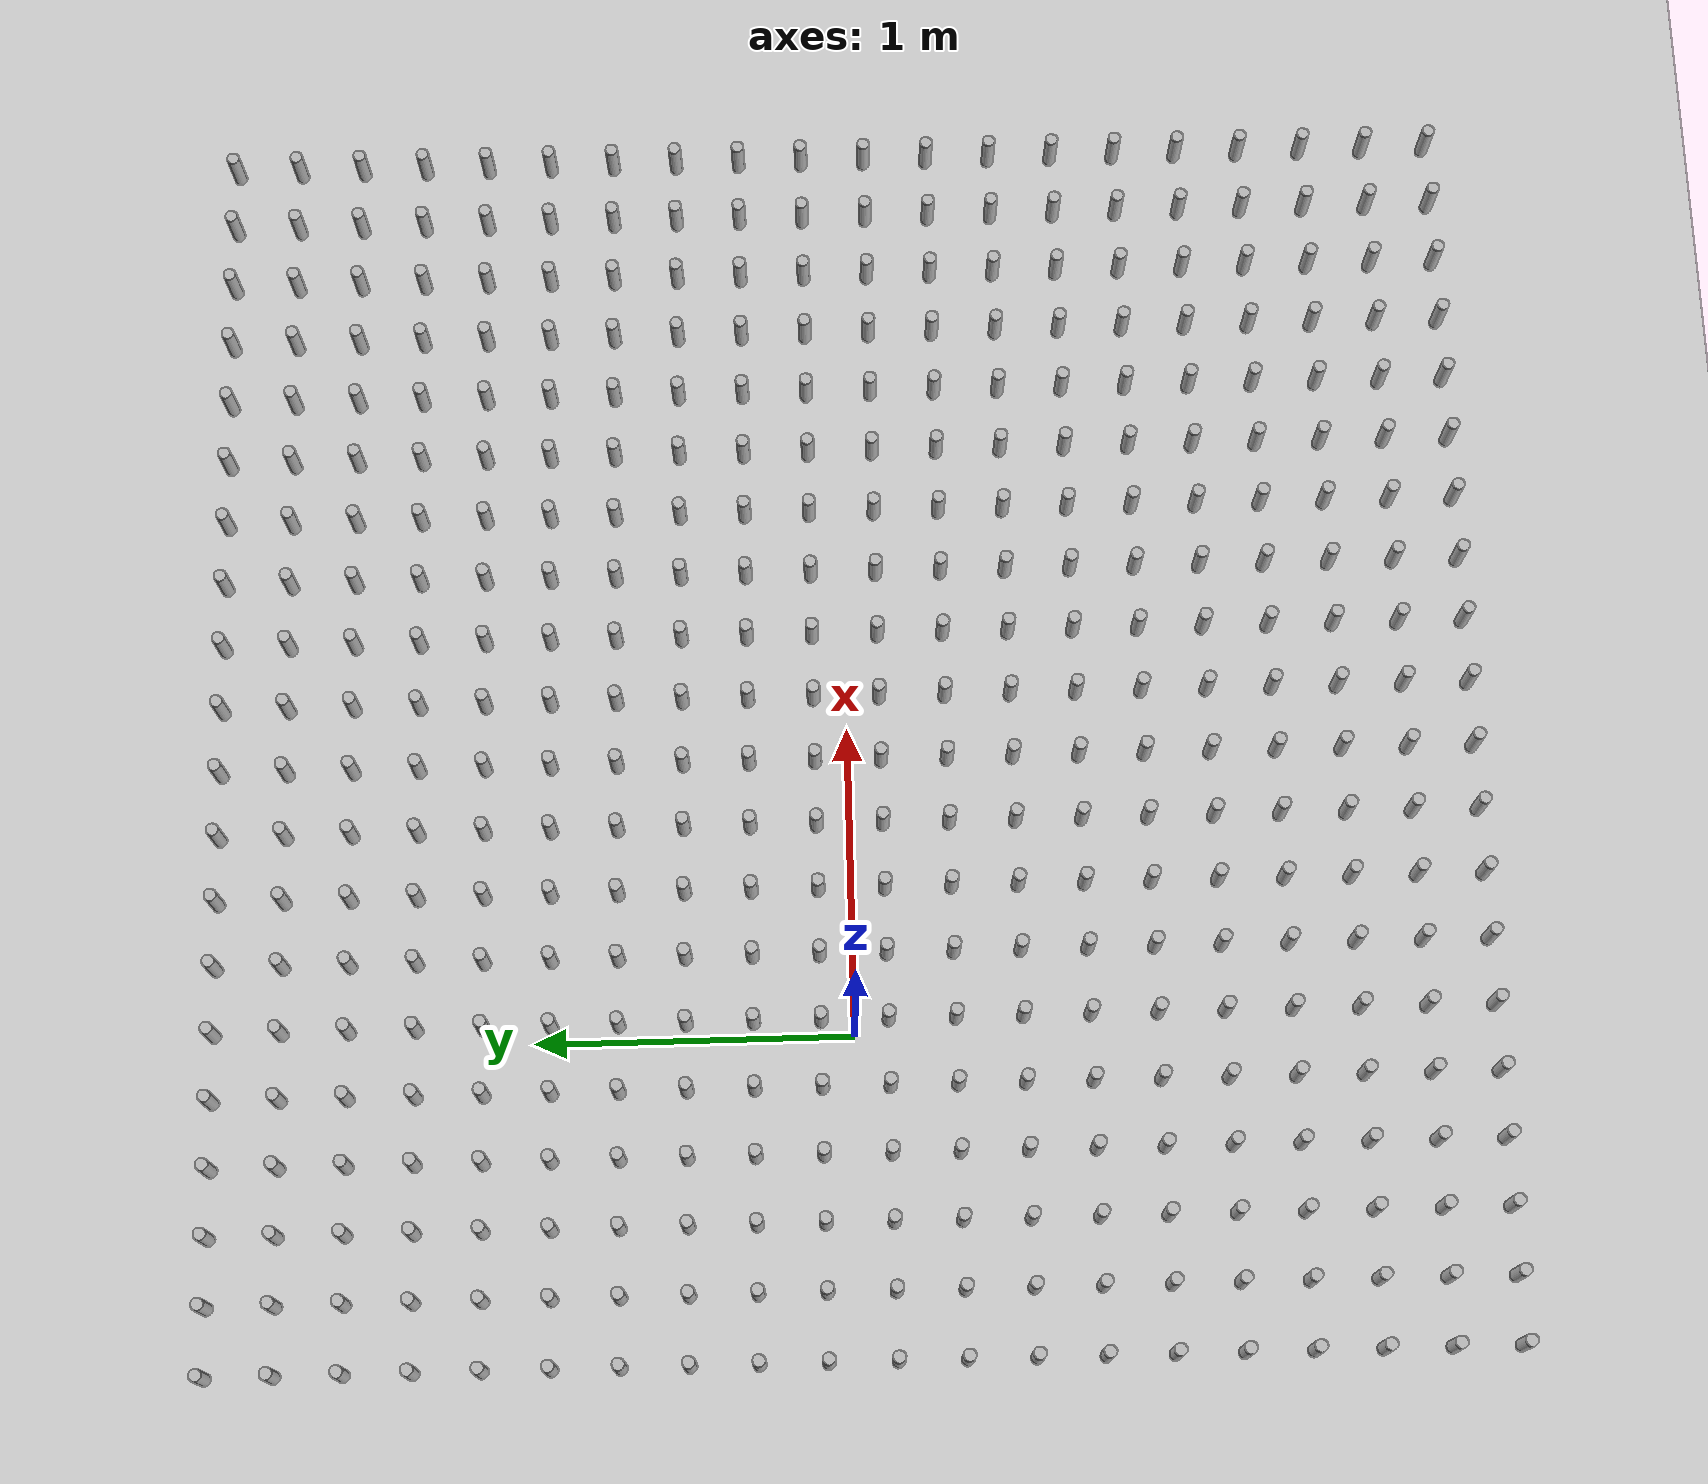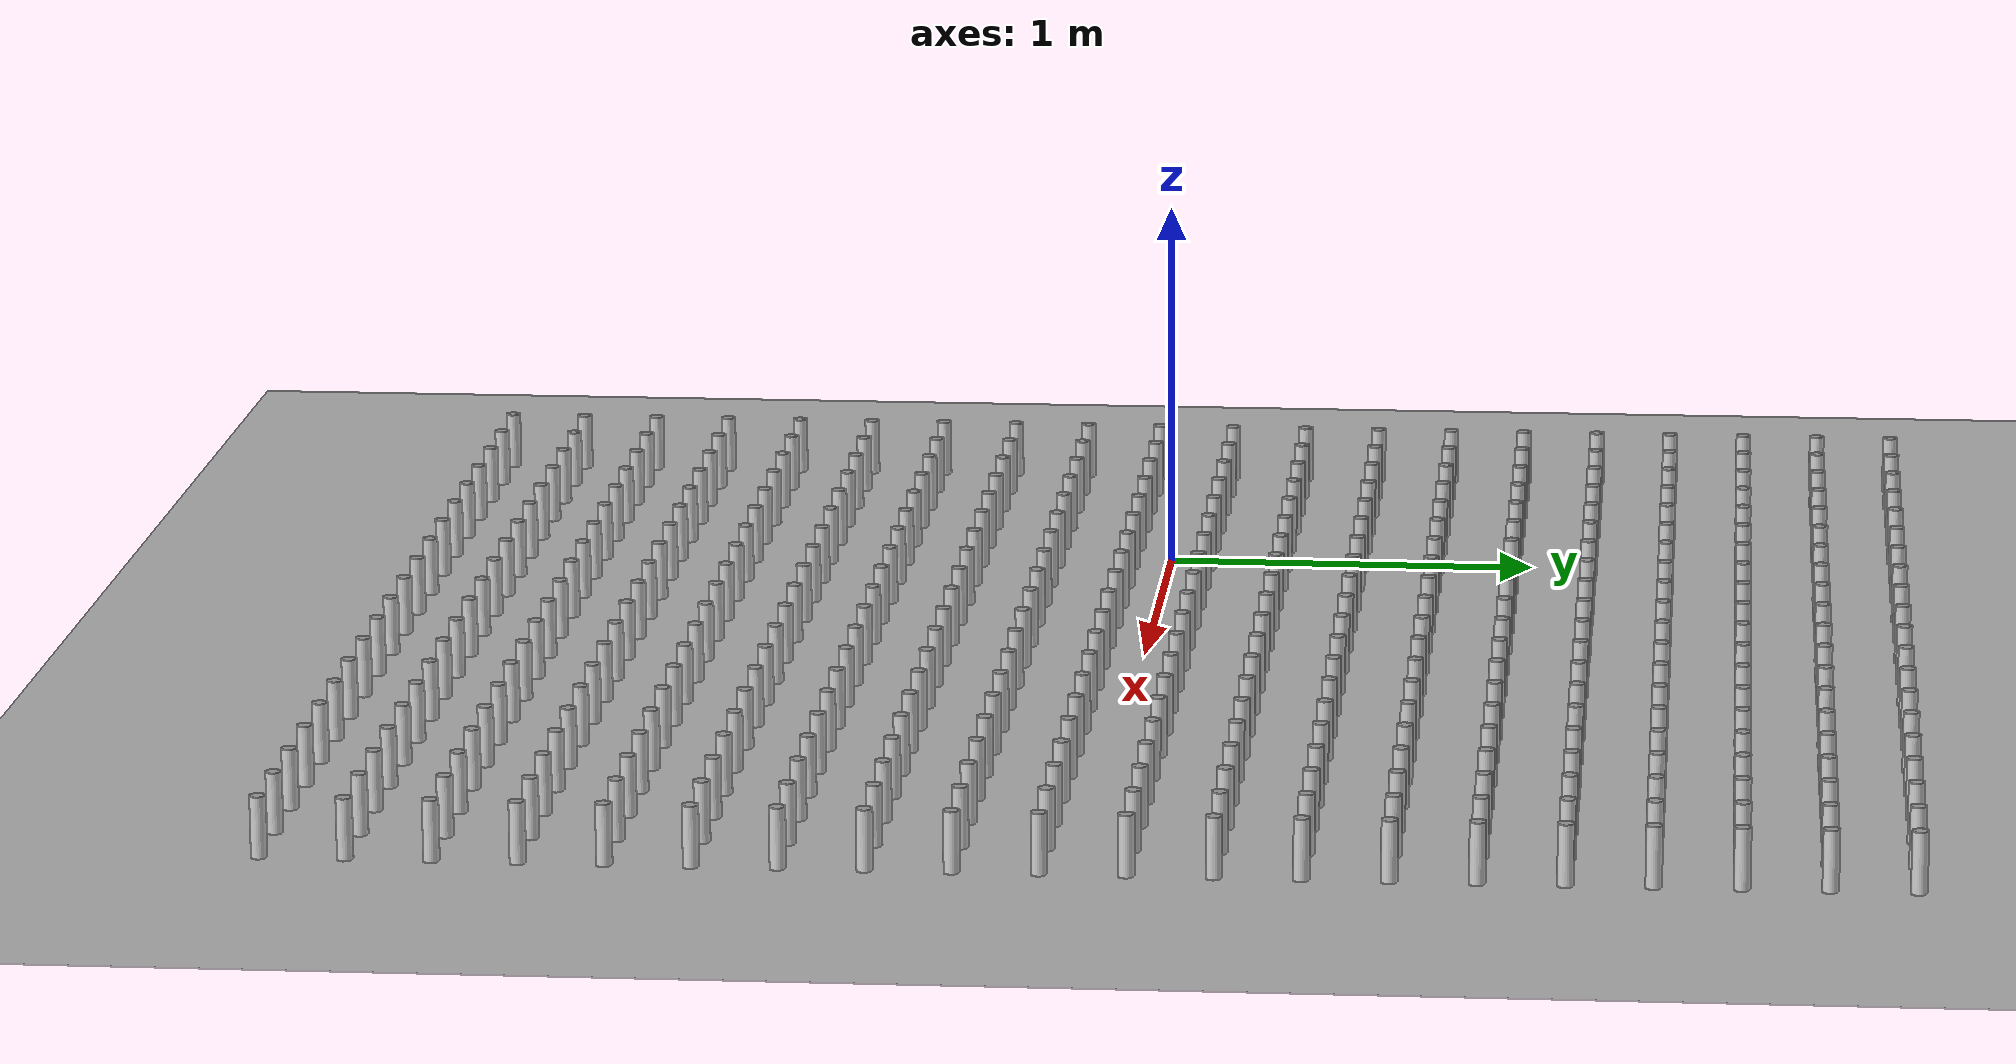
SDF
<?xml version="1.0" ?>
<sdf version="1.6">
  <world name="world">
    <model name="arena_scaffold">
      <pose>0 0 0 0 0 0</pose>
      <link name="floor">
        <pose>0 0 0 0 0 0</pose>
        <collision name="floor_collision">
          <pose>0 0 0 0 0 0</pose>
          <geometry>
            <plane>
              <normal>0 0 1</normal>
              <size>100.0 100.0 1.0</size>
            </plane>
          </geometry>
        </collision>
        <collision name="peg_0_0_collision">
          <pose>-1.0 -2.0 0 0 0 0</pose>
          <geometry>
            <cylinder>
              <radius>0.02</radius>
              <length>0.3</length>
            </cylinder>
          </geometry>
        </collision>
        <collision name="peg_0_1_collision">
          <pose>-1.0 -1.7894736842105263 0 0 0 0</pose>
          <geometry>
            <cylinder>
              <radius>0.02</radius>
              <length>0.3</length>
            </cylinder>
          </geometry>
        </collision>
        <collision name="peg_0_2_collision">
          <pose>-1.0 -1.5789473684210527 0 0 0 0</pose>
          <geometry>
            <cylinder>
              <radius>0.02</radius>
              <length>0.3</length>
            </cylinder>
          </geometry>
        </collision>
        <collision name="peg_0_3_collision">
          <pose>-1.0 -1.368421052631579 0 0 0 0</pose>
          <geometry>
            <cylinder>
              <radius>0.02</radius>
              <length>0.3</length>
            </cylinder>
          </geometry>
        </collision>
        <collision name="peg_0_4_collision">
          <pose>-1.0 -1.1578947368421053 0 0 0 0</pose>
          <geometry>
            <cylinder>
              <radius>0.02</radius>
              <length>0.3</length>
            </cylinder>
          </geometry>
        </collision>
        <collision name="peg_0_5_collision">
          <pose>-1.0 -0.9473684210526316 0 0 0 0</pose>
          <geometry>
            <cylinder>
              <radius>0.02</radius>
              <length>0.3</length>
            </cylinder>
          </geometry>
        </collision>
        <collision name="peg_0_6_collision">
          <pose>-1.0 -0.736842105263158 0 0 0 0</pose>
          <geometry>
            <cylinder>
              <radius>0.02</radius>
              <length>0.3</length>
            </cylinder>
          </geometry>
        </collision>
        <collision name="peg_0_7_collision">
          <pose>-1.0 -0.5263157894736843 0 0 0 0</pose>
          <geometry>
            <cylinder>
              <radius>0.02</radius>
              <length>0.3</length>
            </cylinder>
          </geometry>
        </collision>
        <collision name="peg_0_8_collision">
          <pose>-1.0 -0.3157894736842106 0 0 0 0</pose>
          <geometry>
            <cylinder>
              <radius>0.02</radius>
              <length>0.3</length>
            </cylinder>
          </geometry>
        </collision>
        <collision name="peg_0_9_collision">
          <pose>-1.0 -0.10526315789473695 0 0 0 0</pose>
          <geometry>
            <cylinder>
              <radius>0.02</radius>
              <length>0.3</length>
            </cylinder>
          </geometry>
        </collision>
        <collision name="peg_0_10_collision">
          <pose>-1.0 0.10526315789473673 0 0 0 0</pose>
          <geometry>
            <cylinder>
              <radius>0.02</radius>
              <length>0.3</length>
            </cylinder>
          </geometry>
        </collision>
        <collision name="peg_0_11_collision">
          <pose>-1.0 0.3157894736842106 0 0 0 0</pose>
          <geometry>
            <cylinder>
              <radius>0.02</radius>
              <length>0.3</length>
            </cylinder>
          </geometry>
        </collision>
        <collision name="peg_0_12_collision">
          <pose>-1.0 0.5263157894736841 0 0 0 0</pose>
          <geometry>
            <cylinder>
              <radius>0.02</radius>
              <length>0.3</length>
            </cylinder>
          </geometry>
        </collision>
        <collision name="peg_0_13_collision">
          <pose>-1.0 0.7368421052631575 0 0 0 0</pose>
          <geometry>
            <cylinder>
              <radius>0.02</radius>
              <length>0.3</length>
            </cylinder>
          </geometry>
        </collision>
        <collision name="peg_0_14_collision">
          <pose>-1.0 0.9473684210526314 0 0 0 0</pose>
          <geometry>
            <cylinder>
              <radius>0.02</radius>
              <length>0.3</length>
            </cylinder>
          </geometry>
        </collision>
        <collision name="peg_0_15_collision">
          <pose>-1.0 1.1578947368421053 0 0 0 0</pose>
          <geometry>
            <cylinder>
              <radius>0.02</radius>
              <length>0.3</length>
            </cylinder>
          </geometry>
        </collision>
        <collision name="peg_0_16_collision">
          <pose>-1.0 1.3684210526315788 0 0 0 0</pose>
          <geometry>
            <cylinder>
              <radius>0.02</radius>
              <length>0.3</length>
            </cylinder>
          </geometry>
        </collision>
        <collision name="peg_0_17_collision">
          <pose>-1.0 1.5789473684210522 0 0 0 0</pose>
          <geometry>
            <cylinder>
              <radius>0.02</radius>
              <length>0.3</length>
            </cylinder>
          </geometry>
        </collision>
        <collision name="peg_0_18_collision">
          <pose>-1.0 1.789473684210526 0 0 0 0</pose>
          <geometry>
            <cylinder>
              <radius>0.02</radius>
              <length>0.3</length>
            </cylinder>
          </geometry>
        </collision>
        <collision name="peg_0_19_collision">
          <pose>-1.0 2.0 0 0 0 0</pose>
          <geometry>
            <cylinder>
              <radius>0.02</radius>
              <length>0.3</length>
            </cylinder>
          </geometry>
        </collision>
        <collision name="peg_1_0_collision">
          <pose>-0.7894736842105263 -2.0 0 0 0 0</pose>
          <geometry>
            <cylinder>
              <radius>0.02</radius>
              <length>0.3</length>
            </cylinder>
          </geometry>
        </collision>
        <collision name="peg_1_1_collision">
          <pose>-0.7894736842105263 -1.7894736842105263 0 0 0 0</pose>
          <geometry>
            <cylinder>
              <radius>0.02</radius>
              <length>0.3</length>
            </cylinder>
          </geometry>
        </collision>
        <collision name="peg_1_2_collision">
          <pose>-0.7894736842105263 -1.5789473684210527 0 0 0 0</pose>
          <geometry>
            <cylinder>
              <radius>0.02</radius>
              <length>0.3</length>
            </cylinder>
          </geometry>
        </collision>
        <collision name="peg_1_3_collision">
          <pose>-0.7894736842105263 -1.368421052631579 0 0 0 0</pose>
          <geometry>
            <cylinder>
              <radius>0.02</radius>
              <length>0.3</length>
            </cylinder>
          </geometry>
        </collision>
        <collision name="peg_1_4_collision">
          <pose>-0.7894736842105263 -1.1578947368421053 0 0 0 0</pose>
          <geometry>
            <cylinder>
              <radius>0.02</radius>
              <length>0.3</length>
            </cylinder>
          </geometry>
        </collision>
        <collision name="peg_1_5_collision">
          <pose>-0.7894736842105263 -0.9473684210526316 0 0 0 0</pose>
          <geometry>
            <cylinder>
              <radius>0.02</radius>
              <length>0.3</length>
            </cylinder>
          </geometry>
        </collision>
        <collision name="peg_1_6_collision">
          <pose>-0.7894736842105263 -0.736842105263158 0 0 0 0</pose>
          <geometry>
            <cylinder>
              <radius>0.02</radius>
              <length>0.3</length>
            </cylinder>
          </geometry>
        </collision>
        <collision name="peg_1_7_collision">
          <pose>-0.7894736842105263 -0.5263157894736843 0 0 0 0</pose>
          <geometry>
            <cylinder>
              <radius>0.02</radius>
              <length>0.3</length>
            </cylinder>
          </geometry>
        </collision>
        <collision name="peg_1_8_collision">
          <pose>-0.7894736842105263 -0.3157894736842106 0 0 0 0</pose>
          <geometry>
            <cylinder>
              <radius>0.02</radius>
              <length>0.3</length>
            </cylinder>
          </geometry>
        </collision>
        <collision name="peg_1_9_collision">
          <pose>-0.7894736842105263 -0.10526315789473695 0 0 0 0</pose>
          <geometry>
            <cylinder>
              <radius>0.02</radius>
              <length>0.3</length>
            </cylinder>
          </geometry>
        </collision>
        <collision name="peg_1_10_collision">
          <pose>-0.7894736842105263 0.10526315789473673 0 0 0 0</pose>
          <geometry>
            <cylinder>
              <radius>0.02</radius>
              <length>0.3</length>
            </cylinder>
          </geometry>
        </collision>
        <collision name="peg_1_11_collision">
          <pose>-0.7894736842105263 0.3157894736842106 0 0 0 0</pose>
          <geometry>
            <cylinder>
              <radius>0.02</radius>
              <length>0.3</length>
            </cylinder>
          </geometry>
        </collision>
        <collision name="peg_1_12_collision">
          <pose>-0.7894736842105263 0.5263157894736841 0 0 0 0</pose>
          <geometry>
            <cylinder>
              <radius>0.02</radius>
              <length>0.3</length>
            </cylinder>
          </geometry>
        </collision>
        <collision name="peg_1_13_collision">
          <pose>-0.7894736842105263 0.7368421052631575 0 0 0 0</pose>
          <geometry>
            <cylinder>
              <radius>0.02</radius>
              <length>0.3</length>
            </cylinder>
          </geometry>
        </collision>
        <collision name="peg_1_14_collision">
          <pose>-0.7894736842105263 0.9473684210526314 0 0 0 0</pose>
          <geometry>
            <cylinder>
              <radius>0.02</radius>
              <length>0.3</length>
            </cylinder>
          </geometry>
        </collision>
        <collision name="peg_1_15_collision">
          <pose>-0.7894736842105263 1.1578947368421053 0 0 0 0</pose>
          <geometry>
            <cylinder>
              <radius>0.02</radius>
              <length>0.3</length>
            </cylinder>
          </geometry>
        </collision>
        <collision name="peg_1_16_collision">
          <pose>-0.7894736842105263 1.3684210526315788 0 0 0 0</pose>
          <geometry>
            <cylinder>
              <radius>0.02</radius>
              <length>0.3</length>
            </cylinder>
          </geometry>
        </collision>
        <collision name="peg_1_17_collision">
          <pose>-0.7894736842105263 1.5789473684210522 0 0 0 0</pose>
          <geometry>
            <cylinder>
              <radius>0.02</radius>
              <length>0.3</length>
            </cylinder>
          </geometry>
        </collision>
        <collision name="peg_1_18_collision">
          <pose>-0.7894736842105263 1.789473684210526 0 0 0 0</pose>
          <geometry>
            <cylinder>
              <radius>0.02</radius>
              <length>0.3</length>
            </cylinder>
          </geometry>
        </collision>
        <collision name="peg_1_19_collision">
          <pose>-0.7894736842105263 2.0 0 0 0 0</pose>
          <geometry>
            <cylinder>
              <radius>0.02</radius>
              <length>0.3</length>
            </cylinder>
          </geometry>
        </collision>
        <collision name="peg_2_0_collision">
          <pose>-0.5789473684210527 -2.0 0 0 0 0</pose>
          <geometry>
            <cylinder>
              <radius>0.02</radius>
              <length>0.3</length>
            </cylinder>
          </geometry>
        </collision>
        <collision name="peg_2_1_collision">
          <pose>-0.5789473684210527 -1.7894736842105263 0 0 0 0</pose>
          <geometry>
            <cylinder>
              <radius>0.02</radius>
              <length>0.3</length>
            </cylinder>
          </geometry>
        </collision>
        <collision name="peg_2_2_collision">
          <pose>-0.5789473684210527 -1.5789473684210527 0 0 0 0</pose>
          <geometry>
            <cylinder>
              <radius>0.02</radius>
              <length>0.3</length>
            </cylinder>
          </geometry>
        </collision>
        <collision name="peg_2_3_collision">
          <pose>-0.5789473684210527 -1.368421052631579 0 0 0 0</pose>
          <geometry>
            <cylinder>
              <radius>0.02</radius>
              <length>0.3</length>
            </cylinder>
          </geometry>
        </collision>
        <collision name="peg_2_4_collision">
          <pose>-0.5789473684210527 -1.1578947368421053 0 0 0 0</pose>
          <geometry>
            <cylinder>
              <radius>0.02</radius>
              <length>0.3</length>
            </cylinder>
          </geometry>
        </collision>
        <collision name="peg_2_5_collision">
          <pose>-0.5789473684210527 -0.9473684210526316 0 0 0 0</pose>
          <geometry>
            <cylinder>
              <radius>0.02</radius>
              <length>0.3</length>
            </cylinder>
          </geometry>
        </collision>
        <collision name="peg_2_6_collision">
          <pose>-0.5789473684210527 -0.736842105263158 0 0 0 0</pose>
          <geometry>
            <cylinder>
              <radius>0.02</radius>
              <length>0.3</length>
            </cylinder>
          </geometry>
        </collision>
        <collision name="peg_2_7_collision">
          <pose>-0.5789473684210527 -0.5263157894736843 0 0 0 0</pose>
          <geometry>
            <cylinder>
              <radius>0.02</radius>
              <length>0.3</length>
            </cylinder>
          </geometry>
        </collision>
        <collision name="peg_2_8_collision">
          <pose>-0.5789473684210527 -0.3157894736842106 0 0 0 0</pose>
          <geometry>
            <cylinder>
              <radius>0.02</radius>
              <length>0.3</length>
            </cylinder>
          </geometry>
        </collision>
        <collision name="peg_2_9_collision">
          <pose>-0.5789473684210527 -0.10526315789473695 0 0 0 0</pose>
          <geometry>
            <cylinder>
              <radius>0.02</radius>
              <length>0.3</length>
            </cylinder>
          </geometry>
        </collision>
        <collision name="peg_2_10_collision">
          <pose>-0.5789473684210527 0.10526315789473673 0 0 0 0</pose>
          <geometry>
            <cylinder>
              <radius>0.02</radius>
              <length>0.3</length>
            </cylinder>
          </geometry>
        </collision>
        <collision name="peg_2_11_collision">
          <pose>-0.5789473684210527 0.3157894736842106 0 0 0 0</pose>
          <geometry>
            <cylinder>
              <radius>0.02</radius>
              <length>0.3</length>
            </cylinder>
          </geometry>
        </collision>
        <collision name="peg_2_12_collision">
          <pose>-0.5789473684210527 0.5263157894736841 0 0 0 0</pose>
          <geometry>
            <cylinder>
              <radius>0.02</radius>
              <length>0.3</length>
            </cylinder>
          </geometry>
        </collision>
        <collision name="peg_2_13_collision">
          <pose>-0.5789473684210527 0.7368421052631575 0 0 0 0</pose>
          <geometry>
            <cylinder>
              <radius>0.02</radius>
              <length>0.3</length>
            </cylinder>
          </geometry>
        </collision>
        <collision name="peg_2_14_collision">
          <pose>-0.5789473684210527 0.9473684210526314 0 0 0 0</pose>
          <geometry>
            <cylinder>
              <radius>0.02</radius>
              <length>0.3</length>
            </cylinder>
          </geometry>
        </collision>
        <collision name="peg_2_15_collision">
          <pose>-0.5789473684210527 1.1578947368421053 0 0 0 0</pose>
          <geometry>
            <cylinder>
              <radius>0.02</radius>
              <length>0.3</length>
            </cylinder>
          </geometry>
        </collision>
        <collision name="peg_2_16_collision">
          <pose>-0.5789473684210527 1.3684210526315788 0 0 0 0</pose>
          <geometry>
            <cylinder>
              <radius>0.02</radius>
              <length>0.3</length>
            </cylinder>
          </geometry>
        </collision>
        <collision name="peg_2_17_collision">
          <pose>-0.5789473684210527 1.5789473684210522 0 0 0 0</pose>
          <geometry>
            <cylinder>
              <radius>0.02</radius>
              <length>0.3</length>
            </cylinder>
          </geometry>
        </collision>
        <collision name="peg_2_18_collision">
          <pose>-0.5789473684210527 1.789473684210526 0 0 0 0</pose>
          <geometry>
            <cylinder>
              <radius>0.02</radius>
              <length>0.3</length>
            </cylinder>
          </geometry>
        </collision>
        <collision name="peg_2_19_collision">
          <pose>-0.5789473684210527 2.0 0 0 0 0</pose>
          <geometry>
            <cylinder>
              <radius>0.02</radius>
              <length>0.3</length>
            </cylinder>
          </geometry>
        </collision>
        <collision name="peg_3_0_collision">
          <pose>-0.368421052631579 -2.0 0 0 0 0</pose>
          <geometry>
            <cylinder>
              <radius>0.02</radius>
              <length>0.3</length>
            </cylinder>
          </geometry>
        </collision>
        <collision name="peg_3_1_collision">
          <pose>-0.368421052631579 -1.7894736842105263 0 0 0 0</pose>
          <geometry>
            <cylinder>
              <radius>0.02</radius>
              <length>0.3</length>
            </cylinder>
          </geometry>
        </collision>
        <collision name="peg_3_2_collision">
          <pose>-0.368421052631579 -1.5789473684210527 0 0 0 0</pose>
          <geometry>
            <cylinder>
              <radius>0.02</radius>
              <length>0.3</length>
            </cylinder>
          </geometry>
        </collision>
        <collision name="peg_3_3_collision">
          <pose>-0.368421052631579 -1.368421052631579 0 0 0 0</pose>
          <geometry>
            <cylinder>
              <radius>0.02</radius>
              <length>0.3</length>
            </cylinder>
          </geometry>
        </collision>
        <collision name="peg_3_4_collision">
          <pose>-0.368421052631579 -1.1578947368421053 0 0 0 0</pose>
          <geometry>
            <cylinder>
              <radius>0.02</radius>
              <length>0.3</length>
            </cylinder>
          </geometry>
        </collision>
        <collision name="peg_3_5_collision">
          <pose>-0.368421052631579 -0.9473684210526316 0 0 0 0</pose>
          <geometry>
            <cylinder>
              <radius>0.02</radius>
              <length>0.3</length>
            </cylinder>
          </geometry>
        </collision>
        <collision name="peg_3_6_collision">
          <pose>-0.368421052631579 -0.736842105263158 0 0 0 0</pose>
          <geometry>
            <cylinder>
              <radius>0.02</radius>
              <length>0.3</length>
            </cylinder>
          </geometry>
        </collision>
        <collision name="peg_3_7_collision">
          <pose>-0.368421052631579 -0.5263157894736843 0 0 0 0</pose>
          <geometry>
            <cylinder>
              <radius>0.02</radius>
              <length>0.3</length>
            </cylinder>
          </geometry>
        </collision>
        <collision name="peg_3_8_collision">
          <pose>-0.368421052631579 -0.3157894736842106 0 0 0 0</pose>
          <geometry>
            <cylinder>
              <radius>0.02</radius>
              <length>0.3</length>
            </cylinder>
          </geometry>
        </collision>
        <collision name="peg_3_9_collision">
          <pose>-0.368421052631579 -0.10526315789473695 0 0 0 0</pose>
          <geometry>
            <cylinder>
              <radius>0.02</radius>
              <length>0.3</length>
            </cylinder>
          </geometry>
        </collision>
        <collision name="peg_3_10_collision">
          <pose>-0.368421052631579 0.10526315789473673 0 0 0 0</pose>
          <geometry>
            <cylinder>
              <radius>0.02</radius>
              <length>0.3</length>
            </cylinder>
          </geometry>
        </collision>
        <collision name="peg_3_11_collision">
          <pose>-0.368421052631579 0.3157894736842106 0 0 0 0</pose>
          <geometry>
            <cylinder>
              <radius>0.02</radius>
              <length>0.3</length>
            </cylinder>
          </geometry>
        </collision>
        <collision name="peg_3_12_collision">
          <pose>-0.368421052631579 0.5263157894736841 0 0 0 0</pose>
          <geometry>
            <cylinder>
              <radius>0.02</radius>
              <length>0.3</length>
            </cylinder>
          </geometry>
        </collision>
        <collision name="peg_3_13_collision">
          <pose>-0.368421052631579 0.7368421052631575 0 0 0 0</pose>
          <geometry>
            <cylinder>
              <radius>0.02</radius>
              <length>0.3</length>
            </cylinder>
          </geometry>
        </collision>
        <collision name="peg_3_14_collision">
          <pose>-0.368421052631579 0.9473684210526314 0 0 0 0</pose>
          <geometry>
            <cylinder>
              <radius>0.02</radius>
              <length>0.3</length>
            </cylinder>
          </geometry>
        </collision>
        <collision name="peg_3_15_collision">
          <pose>-0.368421052631579 1.1578947368421053 0 0 0 0</pose>
          <geometry>
            <cylinder>
              <radius>0.02</radius>
              <length>0.3</length>
            </cylinder>
          </geometry>
        </collision>
        <collision name="peg_3_16_collision">
          <pose>-0.368421052631579 1.3684210526315788 0 0 0 0</pose>
          <geometry>
            <cylinder>
              <radius>0.02</radius>
              <length>0.3</length>
            </cylinder>
          </geometry>
        </collision>
        <collision name="peg_3_17_collision">
          <pose>-0.368421052631579 1.5789473684210522 0 0 0 0</pose>
          <geometry>
            <cylinder>
              <radius>0.02</radius>
              <length>0.3</length>
            </cylinder>
          </geometry>
        </collision>
        <collision name="peg_3_18_collision">
          <pose>-0.368421052631579 1.789473684210526 0 0 0 0</pose>
          <geometry>
            <cylinder>
              <radius>0.02</radius>
              <length>0.3</length>
            </cylinder>
          </geometry>
        </collision>
        <collision name="peg_3_19_collision">
          <pose>-0.368421052631579 2.0 0 0 0 0</pose>
          <geometry>
            <cylinder>
              <radius>0.02</radius>
              <length>0.3</length>
            </cylinder>
          </geometry>
        </collision>
        <collision name="peg_4_0_collision">
          <pose>-0.1578947368421053 -2.0 0 0 0 0</pose>
          <geometry>
            <cylinder>
              <radius>0.02</radius>
              <length>0.3</length>
            </cylinder>
          </geometry>
        </collision>
        <collision name="peg_4_1_collision">
          <pose>-0.1578947368421053 -1.7894736842105263 0 0 0 0</pose>
          <geometry>
            <cylinder>
              <radius>0.02</radius>
              <length>0.3</length>
            </cylinder>
          </geometry>
        </collision>
        <collision name="peg_4_2_collision">
          <pose>-0.1578947368421053 -1.5789473684210527 0 0 0 0</pose>
          <geometry>
            <cylinder>
              <radius>0.02</radius>
              <length>0.3</length>
            </cylinder>
          </geometry>
        </collision>
        <collision name="peg_4_3_collision">
          <pose>-0.1578947368421053 -1.368421052631579 0 0 0 0</pose>
          <geometry>
            <cylinder>
              <radius>0.02</radius>
              <length>0.3</length>
            </cylinder>
          </geometry>
        </collision>
        <collision name="peg_4_4_collision">
          <pose>-0.1578947368421053 -1.1578947368421053 0 0 0 0</pose>
          <geometry>
            <cylinder>
              <radius>0.02</radius>
              <length>0.3</length>
            </cylinder>
          </geometry>
        </collision>
        <collision name="peg_4_5_collision">
          <pose>-0.1578947368421053 -0.9473684210526316 0 0 0 0</pose>
          <geometry>
            <cylinder>
              <radius>0.02</radius>
              <length>0.3</length>
            </cylinder>
          </geometry>
        </collision>
        <collision name="peg_4_6_collision">
          <pose>-0.1578947368421053 -0.736842105263158 0 0 0 0</pose>
          <geometry>
            <cylinder>
              <radius>0.02</radius>
              <length>0.3</length>
            </cylinder>
          </geometry>
        </collision>
        <collision name="peg_4_7_collision">
          <pose>-0.1578947368421053 -0.5263157894736843 0 0 0 0</pose>
          <geometry>
            <cylinder>
              <radius>0.02</radius>
              <length>0.3</length>
            </cylinder>
          </geometry>
        </collision>
        <collision name="peg_4_8_collision">
          <pose>-0.1578947368421053 -0.3157894736842106 0 0 0 0</pose>
          <geometry>
            <cylinder>
              <radius>0.02</radius>
              <length>0.3</length>
            </cylinder>
          </geometry>
        </collision>
        <collision name="peg_4_9_collision">
          <pose>-0.1578947368421053 -0.10526315789473695 0 0 0 0</pose>
          <geometry>
            <cylinder>
              <radius>0.02</radius>
              <length>0.3</length>
            </cylinder>
          </geometry>
        </collision>
        <collision name="peg_4_10_collision">
          <pose>-0.1578947368421053 0.10526315789473673 0 0 0 0</pose>
          <geometry>
            <cylinder>
              <radius>0.02</radius>
              <length>0.3</length>
            </cylinder>
          </geometry>
        </collision>
        <collision name="peg_4_11_collision">
          <pose>-0.1578947368421053 0.3157894736842106 0 0 0 0</pose>
          <geometry>
            <cylinder>
              <radius>0.02</radius>
              <length>0.3</length>
            </cylinder>
          </geometry>
        </collision>
        <collision name="peg_4_12_collision">
          <pose>-0.1578947368421053 0.5263157894736841 0 0 0 0</pose>
          <geometry>
            <cylinder>
              <radius>0.02</radius>
              <length>0.3</length>
            </cylinder>
          </geometry>
        </collision>
        <collision name="peg_4_13_collision">
          <pose>-0.1578947368421053 0.7368421052631575 0 0 0 0</pose>
          <geometry>
            <cylinder>
              <radius>0.02</radius>
              <length>0.3</length>
            </cylinder>
          </geometry>
        </collision>
        <collision name="peg_4_14_collision">
          <pose>-0.1578947368421053 0.9473684210526314 0 0 0 0</pose>
          <geometry>
            <cylinder>
              <radius>0.02</radius>
              <length>0.3</length>
            </cylinder>
          </geometry>
        </collision>
        <collision name="peg_4_15_collision">
          <pose>-0.1578947368421053 1.1578947368421053 0 0 0 0</pose>
          <geometry>
            <cylinder>
              <radius>0.02</radius>
              <length>0.3</length>
            </cylinder>
          </geometry>
        </collision>
        <collision name="peg_4_16_collision">
          <pose>-0.1578947368421053 1.3684210526315788 0 0 0 0</pose>
          <geometry>
            <cylinder>
              <radius>0.02</radius>
              <length>0.3</length>
            </cylinder>
          </geometry>
        </collision>
        <collision name="peg_4_17_collision">
          <pose>-0.1578947368421053 1.5789473684210522 0 0 0 0</pose>
          <geometry>
            <cylinder>
              <radius>0.02</radius>
              <length>0.3</length>
            </cylinder>
          </geometry>
        </collision>
        <collision name="peg_4_18_collision">
          <pose>-0.1578947368421053 1.789473684210526 0 0 0 0</pose>
          <geometry>
            <cylinder>
              <radius>0.02</radius>
              <length>0.3</length>
            </cylinder>
          </geometry>
        </collision>
        <collision name="peg_4_19_collision">
          <pose>-0.1578947368421053 2.0 0 0 0 0</pose>
          <geometry>
            <cylinder>
              <radius>0.02</radius>
              <length>0.3</length>
            </cylinder>
          </geometry>
        </collision>
        <collision name="peg_5_0_collision">
          <pose>0.05263157894736836 -2.0 0 0 0 0</pose>
          <geometry>
            <cylinder>
              <radius>0.02</radius>
              <length>0.3</length>
            </cylinder>
          </geometry>
        </collision>
        <collision name="peg_5_1_collision">
          <pose>0.05263157894736836 -1.7894736842105263 0 0 0 0</pose>
          <geometry>
            <cylinder>
              <radius>0.02</radius>
              <length>0.3</length>
            </cylinder>
          </geometry>
        </collision>
        <collision name="peg_5_2_collision">
          <pose>0.05263157894736836 -1.5789473684210527 0 0 0 0</pose>
          <geometry>
            <cylinder>
              <radius>0.02</radius>
              <length>0.3</length>
            </cylinder>
          </geometry>
        </collision>
        <collision name="peg_5_3_collision">
          <pose>0.05263157894736836 -1.368421052631579 0 0 0 0</pose>
          <geometry>
            <cylinder>
              <radius>0.02</radius>
              <length>0.3</length>
            </cylinder>
          </geometry>
        </collision>
        <collision name="peg_5_4_collision">
          <pose>0.05263157894736836 -1.1578947368421053 0 0 0 0</pose>
          <geometry>
            <cylinder>
              <radius>0.02</radius>
              <length>0.3</length>
            </cylinder>
          </geometry>
        </collision>
        <collision name="peg_5_5_collision">
          <pose>0.05263157894736836 -0.9473684210526316 0 0 0 0</pose>
          <geometry>
            <cylinder>
              <radius>0.02</radius>
              <length>0.3</length>
            </cylinder>
          </geometry>
        </collision>
        <collision name="peg_5_6_collision">
          <pose>0.05263157894736836 -0.736842105263158 0 0 0 0</pose>
          <geometry>
            <cylinder>
              <radius>0.02</radius>
              <length>0.3</length>
            </cylinder>
          </geometry>
        </collision>
        <collision name="peg_5_7_collision">
          <pose>0.05263157894736836 -0.5263157894736843 0 0 0 0</pose>
          <geometry>
            <cylinder>
              <radius>0.02</radius>
              <length>0.3</length>
            </cylinder>
          </geometry>
        </collision>
        <collision name="peg_5_8_collision">
          <pose>0.05263157894736836 -0.3157894736842106 0 0 0 0</pose>
          <geometry>
            <cylinder>
              <radius>0.02</radius>
              <length>0.3</length>
            </cylinder>
          </geometry>
        </collision>
        <collision name="peg_5_9_collision">
          <pose>0.05263157894736836 -0.10526315789473695 0 0 0 0</pose>
          <geometry>
            <cylinder>
              <radius>0.02</radius>
              <length>0.3</length>
            </cylinder>
          </geometry>
        </collision>
        <collision name="peg_5_10_collision">
          <pose>0.05263157894736836 0.10526315789473673 0 0 0 0</pose>
          <geometry>
            <cylinder>
              <radius>0.02</radius>
              <length>0.3</length>
            </cylinder>
          </geometry>
        </collision>
        <collision name="peg_5_11_collision">
          <pose>0.05263157894736836 0.3157894736842106 0 0 0 0</pose>
          <geometry>
            <cylinder>
              <radius>0.02</radius>
              <length>0.3</length>
            </cylinder>
          </geometry>
        </collision>
        <collision name="peg_5_12_collision">
          <pose>0.05263157894736836 0.5263157894736841 0 0 0 0</pose>
          <geometry>
            <cylinder>
              <radius>0.02</radius>
              <length>0.3</length>
            </cylinder>
          </geometry>
        </collision>
        <collision name="peg_5_13_collision">
          <pose>0.05263157894736836 0.7368421052631575 0 0 0 0</pose>
          <geometry>
            <cylinder>
              <radius>0.02</radius>
              <length>0.3</length>
            </cylinder>
          </geometry>
        </collision>
        <collision name="peg_5_14_collision">
          <pose>0.05263157894736836 0.9473684210526314 0 0 0 0</pose>
          <geometry>
            <cylinder>
              <radius>0.02</radius>
              <length>0.3</length>
            </cylinder>
          </geometry>
        </collision>
        <collision name="peg_5_15_collision">
          <pose>0.05263157894736836 1.1578947368421053 0 0 0 0</pose>
          <geometry>
            <cylinder>
              <radius>0.02</radius>
              <length>0.3</length>
            </cylinder>
          </geometry>
        </collision>
        <collision name="peg_5_16_collision">
          <pose>0.05263157894736836 1.3684210526315788 0 0 0 0</pose>
          <geometry>
            <cylinder>
              <radius>0.02</radius>
              <length>0.3</length>
            </cylinder>
          </geometry>
        </collision>
        <collision name="peg_5_17_collision">
          <pose>0.05263157894736836 1.5789473684210522 0 0 0 0</pose>
          <geometry>
            <cylinder>
              <radius>0.02</radius>
              <length>0.3</length>
            </cylinder>
          </geometry>
        </collision>
        <collision name="peg_5_18_collision">
          <pose>0.05263157894736836 1.789473684210526 0 0 0 0</pose>
          <geometry>
            <cylinder>
              <radius>0.02</radius>
              <length>0.3</length>
            </cylinder>
          </geometry>
        </collision>
        <collision name="peg_5_19_collision">
          <pose>0.05263157894736836 2.0 0 0 0 0</pose>
          <geometry>
            <cylinder>
              <radius>0.02</radius>
              <length>0.3</length>
            </cylinder>
          </geometry>
        </collision>
        <collision name="peg_6_0_collision">
          <pose>0.26315789473684204 -2.0 0 0 0 0</pose>
          <geometry>
            <cylinder>
              <radius>0.02</radius>
              <length>0.3</length>
            </cylinder>
          </geometry>
        </collision>
        <collision name="peg_6_1_collision">
          <pose>0.26315789473684204 -1.7894736842105263 0 0 0 0</pose>
          <geometry>
            <cylinder>
              <radius>0.02</radius>
              <length>0.3</length>
            </cylinder>
          </geometry>
        </collision>
        <collision name="peg_6_2_collision">
          <pose>0.26315789473684204 -1.5789473684210527 0 0 0 0</pose>
          <geometry>
            <cylinder>
              <radius>0.02</radius>
              <length>0.3</length>
            </cylinder>
          </geometry>
        </collision>
        <collision name="peg_6_3_collision">
          <pose>0.26315789473684204 -1.368421052631579 0 0 0 0</pose>
          <geometry>
            <cylinder>
              <radius>0.02</radius>
              <length>0.3</length>
            </cylinder>
          </geometry>
        </collision>
        <collision name="peg_6_4_collision">
          <pose>0.26315789473684204 -1.1578947368421053 0 0 0 0</pose>
          <geometry>
            <cylinder>
              <radius>0.02</radius>
              <length>0.3</length>
            </cylinder>
          </geometry>
        </collision>
        <collision name="peg_6_5_collision">
          <pose>0.26315789473684204 -0.9473684210526316 0 0 0 0</pose>
          <geometry>
            <cylinder>
              <radius>0.02</radius>
              <length>0.3</length>
            </cylinder>
          </geometry>
        </collision>
        <collision name="peg_6_6_collision">
          <pose>0.26315789473684204 -0.736842105263158 0 0 0 0</pose>
          <geometry>
            <cylinder>
              <radius>0.02</radius>
              <length>0.3</length>
            </cylinder>
          </geometry>
        </collision>
        <collision name="peg_6_7_collision">
          <pose>0.26315789473684204 -0.5263157894736843 0 0 0 0</pose>
          <geometry>
            <cylinder>
              <radius>0.02</radius>
              <length>0.3</length>
            </cylinder>
          </geometry>
        </collision>
        <collision name="peg_6_8_collision">
          <pose>0.26315789473684204 -0.3157894736842106 0 0 0 0</pose>
          <geometry>
            <cylinder>
              <radius>0.02</radius>
              <length>0.3</length>
            </cylinder>
          </geometry>
        </collision>
        <collision name="peg_6_9_collision">
          <pose>0.26315789473684204 -0.10526315789473695 0 0 0 0</pose>
          <geometry>
            <cylinder>
              <radius>0.02</radius>
              <length>0.3</length>
            </cylinder>
          </geometry>
        </collision>
        <collision name="peg_6_10_collision">
          <pose>0.26315789473684204 0.10526315789473673 0 0 0 0</pose>
          <geometry>
            <cylinder>
              <radius>0.02</radius>
              <length>0.3</length>
            </cylinder>
          </geometry>
        </collision>
        <collision name="peg_6_11_collision">
          <pose>0.26315789473684204 0.3157894736842106 0 0 0 0</pose>
          <geometry>
            <cylinder>
              <radius>0.02</radius>
              <length>0.3</length>
            </cylinder>
          </geometry>
        </collision>
        <collision name="peg_6_12_collision">
          <pose>0.26315789473684204 0.5263157894736841 0 0 0 0</pose>
          <geometry>
            <cylinder>
              <radius>0.02</radius>
              <length>0.3</length>
            </cylinder>
          </geometry>
        </collision>
        <collision name="peg_6_13_collision">
          <pose>0.26315789473684204 0.7368421052631575 0 0 0 0</pose>
          <geometry>
            <cylinder>
              <radius>0.02</radius>
              <length>0.3</length>
            </cylinder>
          </geometry>
        </collision>
        <collision name="peg_6_14_collision">
          <pose>0.26315789473684204 0.9473684210526314 0 0 0 0</pose>
          <geometry>
            <cylinder>
              <radius>0.02</radius>
              <length>0.3</length>
            </cylinder>
          </geometry>
        </collision>
        <collision name="peg_6_15_collision">
          <pose>0.26315789473684204 1.1578947368421053 0 0 0 0</pose>
          <geometry>
            <cylinder>
              <radius>0.02</radius>
              <length>0.3</length>
            </cylinder>
          </geometry>
        </collision>
        <collision name="peg_6_16_collision">
          <pose>0.26315789473684204 1.3684210526315788 0 0 0 0</pose>
          <geometry>
            <cylinder>
              <radius>0.02</radius>
              <length>0.3</length>
            </cylinder>
          </geometry>
        </collision>
        <collision name="peg_6_17_collision">
          <pose>0.26315789473684204 1.5789473684210522 0 0 0 0</pose>
          <geometry>
            <cylinder>
              <radius>0.02</radius>
              <length>0.3</length>
            </cylinder>
          </geometry>
        </collision>
        <collision name="peg_6_18_collision">
          <pose>0.26315789473684204 1.789473684210526 0 0 0 0</pose>
          <geometry>
            <cylinder>
              <radius>0.02</radius>
              <length>0.3</length>
            </cylinder>
          </geometry>
        </collision>
        <collision name="peg_6_19_collision">
          <pose>0.26315789473684204 2.0 0 0 0 0</pose>
          <geometry>
            <cylinder>
              <radius>0.02</radius>
              <length>0.3</length>
            </cylinder>
          </geometry>
        </collision>
        <collision name="peg_7_0_collision">
          <pose>0.4736842105263157 -2.0 0 0 0 0</pose>
          <geometry>
            <cylinder>
              <radius>0.02</radius>
              <length>0.3</length>
            </cylinder>
          </geometry>
        </collision>
        <collision name="peg_7_1_collision">
          <pose>0.4736842105263157 -1.7894736842105263 0 0 0 0</pose>
          <geometry>
            <cylinder>
              <radius>0.02</radius>
              <length>0.3</length>
            </cylinder>
          </geometry>
        </collision>
        <collision name="peg_7_2_collision">
          <pose>0.4736842105263157 -1.5789473684210527 0 0 0 0</pose>
          <geometry>
            <cylinder>
              <radius>0.02</radius>
              <length>0.3</length>
            </cylinder>
          </geometry>
        </collision>
        <collision name="peg_7_3_collision">
          <pose>0.4736842105263157 -1.368421052631579 0 0 0 0</pose>
          <geometry>
            <cylinder>
              <radius>0.02</radius>
              <length>0.3</length>
            </cylinder>
          </geometry>
        </collision>
        <collision name="peg_7_4_collision">
          <pose>0.4736842105263157 -1.1578947368421053 0 0 0 0</pose>
          <geometry>
            <cylinder>
              <radius>0.02</radius>
              <length>0.3</length>
            </cylinder>
          </geometry>
        </collision>
        <collision name="peg_7_5_collision">
          <pose>0.4736842105263157 -0.9473684210526316 0 0 0 0</pose>
          <geometry>
            <cylinder>
              <radius>0.02</radius>
              <length>0.3</length>
            </cylinder>
          </geometry>
        </collision>
        <collision name="peg_7_6_collision">
          <pose>0.4736842105263157 -0.736842105263158 0 0 0 0</pose>
          <geometry>
            <cylinder>
              <radius>0.02</radius>
              <length>0.3</length>
            </cylinder>
          </geometry>
        </collision>
        <collision name="peg_7_7_collision">
          <pose>0.4736842105263157 -0.5263157894736843 0 0 0 0</pose>
          <geometry>
            <cylinder>
              <radius>0.02</radius>
              <length>0.3</length>
            </cylinder>
          </geometry>
        </collision>
        <collision name="peg_7_8_collision">
          <pose>0.4736842105263157 -0.3157894736842106 0 0 0 0</pose>
          <geometry>
            <cylinder>
              <radius>0.02</radius>
              <length>0.3</length>
            </cylinder>
          </geometry>
        </collision>
        <collision name="peg_7_9_collision">
          <pose>0.4736842105263157 -0.10526315789473695 0 0 0 0</pose>
          <geometry>
            <cylinder>
              <radius>0.02</radius>
              <length>0.3</length>
            </cylinder>
          </geometry>
        </collision>
        <collision name="peg_7_10_collision">
          <pose>0.4736842105263157 0.10526315789473673 0 0 0 0</pose>
          <geometry>
            <cylinder>
              <radius>0.02</radius>
              <length>0.3</length>
            </cylinder>
          </geometry>
        </collision>
        <collision name="peg_7_11_collision">
          <pose>0.4736842105263157 0.3157894736842106 0 0 0 0</pose>
          <geometry>
            <cylinder>
              <radius>0.02</radius>
              <length>0.3</length>
            </cylinder>
          </geometry>
        </collision>
        <collision name="peg_7_12_collision">
          <pose>0.4736842105263157 0.5263157894736841 0 0 0 0</pose>
          <geometry>
            <cylinder>
              <radius>0.02</radius>
              <length>0.3</length>
            </cylinder>
          </geometry>
        </collision>
        <collision name="peg_7_13_collision">
          <pose>0.4736842105263157 0.7368421052631575 0 0 0 0</pose>
          <geometry>
            <cylinder>
              <radius>0.02</radius>
              <length>0.3</length>
            </cylinder>
          </geometry>
        </collision>
        <collision name="peg_7_14_collision">
          <pose>0.4736842105263157 0.9473684210526314 0 0 0 0</pose>
          <geometry>
            <cylinder>
              <radius>0.02</radius>
              <length>0.3</length>
            </cylinder>
          </geometry>
        </collision>
        <collision name="peg_7_15_collision">
          <pose>0.4736842105263157 1.1578947368421053 0 0 0 0</pose>
          <geometry>
            <cylinder>
              <radius>0.02</radius>
              <length>0.3</length>
            </cylinder>
          </geometry>
        </collision>
        <collision name="peg_7_16_collision">
          <pose>0.4736842105263157 1.3684210526315788 0 0 0 0</pose>
          <geometry>
            <cylinder>
              <radius>0.02</radius>
              <length>0.3</length>
            </cylinder>
          </geometry>
        </collision>
        <collision name="peg_7_17_collision">
          <pose>0.4736842105263157 1.5789473684210522 0 0 0 0</pose>
          <geometry>
            <cylinder>
              <radius>0.02</radius>
              <length>0.3</length>
            </cylinder>
          </geometry>
        </collision>
        <collision name="peg_7_18_collision">
          <pose>0.4736842105263157 1.789473684210526 0 0 0 0</pose>
          <geometry>
            <cylinder>
              <radius>0.02</radius>
              <length>0.3</length>
            </cylinder>
          </geometry>
        </collision>
        <collision name="peg_7_19_collision">
          <pose>0.4736842105263157 2.0 0 0 0 0</pose>
          <geometry>
            <cylinder>
              <radius>0.02</radius>
              <length>0.3</length>
            </cylinder>
          </geometry>
        </collision>
        <collision name="peg_8_0_collision">
          <pose>0.6842105263157894 -2.0 0 0 0 0</pose>
          <geometry>
            <cylinder>
              <radius>0.02</radius>
              <length>0.3</length>
            </cylinder>
          </geometry>
        </collision>
        <collision name="peg_8_1_collision">
          <pose>0.6842105263157894 -1.7894736842105263 0 0 0 0</pose>
          <geometry>
            <cylinder>
              <radius>0.02</radius>
              <length>0.3</length>
            </cylinder>
          </geometry>
        </collision>
        <collision name="peg_8_2_collision">
          <pose>0.6842105263157894 -1.5789473684210527 0 0 0 0</pose>
          <geometry>
            <cylinder>
              <radius>0.02</radius>
              <length>0.3</length>
            </cylinder>
          </geometry>
        </collision>
        <collision name="peg_8_3_collision">
          <pose>0.6842105263157894 -1.368421052631579 0 0 0 0</pose>
          <geometry>
            <cylinder>
              <radius>0.02</radius>
              <length>0.3</length>
            </cylinder>
          </geometry>
        </collision>
        <collision name="peg_8_4_collision">
          <pose>0.6842105263157894 -1.1578947368421053 0 0 0 0</pose>
          <geometry>
            <cylinder>
              <radius>0.02</radius>
              <length>0.3</length>
            </cylinder>
          </geometry>
        </collision>
        <collision name="peg_8_5_collision">
          <pose>0.6842105263157894 -0.9473684210526316 0 0 0 0</pose>
          <geometry>
            <cylinder>
              <radius>0.02</radius>
              <length>0.3</length>
            </cylinder>
          </geometry>
        </collision>
        <collision name="peg_8_6_collision">
          <pose>0.6842105263157894 -0.736842105263158 0 0 0 0</pose>
          <geometry>
            <cylinder>
              <radius>0.02</radius>
              <length>0.3</length>
            </cylinder>
          </geometry>
        </collision>
        <collision name="peg_8_7_collision">
          <pose>0.6842105263157894 -0.5263157894736843 0 0 0 0</pose>
          <geometry>
            <cylinder>
              <radius>0.02</radius>
              <length>0.3</length>
            </cylinder>
          </geometry>
        </collision>
        <collision name="peg_8_8_collision">
          <pose>0.6842105263157894 -0.3157894736842106 0 0 0 0</pose>
          <geometry>
            <cylinder>
              <radius>0.02</radius>
              <length>0.3</length>
            </cylinder>
          </geometry>
        </collision>
        <collision name="peg_8_9_collision">
          <pose>0.6842105263157894 -0.10526315789473695 0 0 0 0</pose>
          <geometry>
            <cylinder>
              <radius>0.02</radius>
              <length>0.3</length>
            </cylinder>
          </geometry>
        </collision>
        <collision name="peg_8_10_collision">
          <pose>0.6842105263157894 0.10526315789473673 0 0 0 0</pose>
          <geometry>
            <cylinder>
              <radius>0.02</radius>
              <length>0.3</length>
            </cylinder>
          </geometry>
        </collision>
        <collision name="peg_8_11_collision">
          <pose>0.6842105263157894 0.3157894736842106 0 0 0 0</pose>
          <geometry>
            <cylinder>
              <radius>0.02</radius>
              <length>0.3</length>
            </cylinder>
          </geometry>
        </collision>
        <collision name="peg_8_12_collision">
          <pose>0.6842105263157894 0.5263157894736841 0 0 0 0</pose>
          <geometry>
            <cylinder>
              <radius>0.02</radius>
              <length>0.3</length>
            </cylinder>
          </geometry>
        </collision>
        <collision name="peg_8_13_collision">
          <pose>0.6842105263157894 0.7368421052631575 0 0 0 0</pose>
          <geometry>
            <cylinder>
              <radius>0.02</radius>
              <length>0.3</length>
            </cylinder>
          </geometry>
        </collision>
        <collision name="peg_8_14_collision">
          <pose>0.6842105263157894 0.9473684210526314 0 0 0 0</pose>
          <geometry>
            <cylinder>
              <radius>0.02</radius>
              <length>0.3</length>
            </cylinder>
          </geometry>
        </collision>
        <collision name="peg_8_15_collision">
          <pose>0.6842105263157894 1.1578947368421053 0 0 0 0</pose>
          <geometry>
            <cylinder>
              <radius>0.02</radius>
              <length>0.3</length>
            </cylinder>
          </geometry>
        </collision>
        <collision name="peg_8_16_collision">
          <pose>0.6842105263157894 1.3684210526315788 0 0 0 0</pose>
          <geometry>
            <cylinder>
              <radius>0.02</radius>
              <length>0.3</length>
            </cylinder>
          </geometry>
        </collision>
        <collision name="peg_8_17_collision">
          <pose>0.6842105263157894 1.5789473684210522 0 0 0 0</pose>
          <geometry>
            <cylinder>
              <radius>0.02</radius>
              <length>0.3</length>
            </cylinder>
          </geometry>
        </collision>
        <collision name="peg_8_18_collision">
          <pose>0.6842105263157894 1.789473684210526 0 0 0 0</pose>
          <geometry>
            <cylinder>
              <radius>0.02</radius>
              <length>0.3</length>
            </cylinder>
          </geometry>
        </collision>
        <collision name="peg_8_19_collision">
          <pose>0.6842105263157894 2.0 0 0 0 0</pose>
          <geometry>
            <cylinder>
              <radius>0.02</radius>
              <length>0.3</length>
            </cylinder>
          </geometry>
        </collision>
        <collision name="peg_9_0_collision">
          <pose>0.894736842105263 -2.0 0 0 0 0</pose>
          <geometry>
            <cylinder>
              <radius>0.02</radius>
              <length>0.3</length>
            </cylinder>
          </geometry>
        </collision>
        <collision name="peg_9_1_collision">
          <pose>0.894736842105263 -1.7894736842105263 0 0 0 0</pose>
          <geometry>
            <cylinder>
              <radius>0.02</radius>
              <length>0.3</length>
            </cylinder>
          </geometry>
        </collision>
        <collision name="peg_9_2_collision">
          <pose>0.894736842105263 -1.5789473684210527 0 0 0 0</pose>
          <geometry>
            <cylinder>
              <radius>0.02</radius>
              <length>0.3</length>
            </cylinder>
          </geometry>
        </collision>
        <collision name="peg_9_3_collision">
          <pose>0.894736842105263 -1.368421052631579 0 0 0 0</pose>
          <geometry>
            <cylinder>
              <radius>0.02</radius>
              <length>0.3</length>
            </cylinder>
          </geometry>
        </collision>
        <collision name="peg_9_4_collision">
          <pose>0.894736842105263 -1.1578947368421053 0 0 0 0</pose>
          <geometry>
            <cylinder>
              <radius>0.02</radius>
              <length>0.3</length>
            </cylinder>
          </geometry>
        </collision>
        <collision name="peg_9_5_collision">
          <pose>0.894736842105263 -0.9473684210526316 0 0 0 0</pose>
          <geometry>
            <cylinder>
              <radius>0.02</radius>
              <length>0.3</length>
            </cylinder>
          </geometry>
        </collision>
        <collision name="peg_9_6_collision">
          <pose>0.894736842105263 -0.736842105263158 0 0 0 0</pose>
          <geometry>
            <cylinder>
              <radius>0.02</radius>
              <length>0.3</length>
            </cylinder>
          </geometry>
        </collision>
        <collision name="peg_9_7_collision">
          <pose>0.894736842105263 -0.5263157894736843 0 0 0 0</pose>
          <geometry>
            <cylinder>
              <radius>0.02</radius>
              <length>0.3</length>
            </cylinder>
          </geometry>
        </collision>
        <collision name="peg_9_8_collision">
          <pose>0.894736842105263 -0.3157894736842106 0 0 0 0</pose>
          <geometry>
            <cylinder>
              <radius>0.02</radius>
              <length>0.3</length>
            </cylinder>
          </geometry>
        </collision>
        <collision name="peg_9_9_collision">
          <pose>0.894736842105263 -0.10526315789473695 0 0 0 0</pose>
          <geometry>
            <cylinder>
              <radius>0.02</radius>
              <length>0.3</length>
            </cylinder>
          </geometry>
        </collision>
        <collision name="peg_9_10_collision">
          <pose>0.894736842105263 0.10526315789473673 0 0 0 0</pose>
          <geometry>
            <cylinder>
              <radius>0.02</radius>
              <length>0.3</length>
            </cylinder>
          </geometry>
        </collision>
        <collision name="peg_9_11_collision">
          <pose>0.894736842105263 0.3157894736842106 0 0 0 0</pose>
          <geometry>
            <cylinder>
              <radius>0.02</radius>
              <length>0.3</length>
            </cylinder>
          </geometry>
        </collision>
        <collision name="peg_9_12_collision">
          <pose>0.894736842105263 0.5263157894736841 0 0 0 0</pose>
          <geometry>
            <cylinder>
              <radius>0.02</radius>
              <length>0.3</length>
            </cylinder>
          </geometry>
        </collision>
        <collision name="peg_9_13_collision">
          <pose>0.894736842105263 0.7368421052631575 0 0 0 0</pose>
          <geometry>
            <cylinder>
              <radius>0.02</radius>
              <length>0.3</length>
            </cylinder>
          </geometry>
        </collision>
        <collision name="peg_9_14_collision">
          <pose>0.894736842105263 0.9473684210526314 0 0 0 0</pose>
          <geometry>
            <cylinder>
              <radius>0.02</radius>
              <length>0.3</length>
            </cylinder>
          </geometry>
        </collision>
        <collision name="peg_9_15_collision">
          <pose>0.894736842105263 1.1578947368421053 0 0 0 0</pose>
          <geometry>
            <cylinder>
              <radius>0.02</radius>
              <length>0.3</length>
            </cylinder>
          </geometry>
        </collision>
        <collision name="peg_9_16_collision">
          <pose>0.894736842105263 1.3684210526315788 0 0 0 0</pose>
          <geometry>
            <cylinder>
              <radius>0.02</radius>
              <length>0.3</length>
            </cylinder>
          </geometry>
        </collision>
        <collision name="peg_9_17_collision">
          <pose>0.894736842105263 1.5789473684210522 0 0 0 0</pose>
          <geometry>
            <cylinder>
              <radius>0.02</radius>
              <length>0.3</length>
            </cylinder>
          </geometry>
        </collision>
        <collision name="peg_9_18_collision">
          <pose>0.894736842105263 1.789473684210526 0 0 0 0</pose>
          <geometry>
            <cylinder>
              <radius>0.02</radius>
              <length>0.3</length>
            </cylinder>
          </geometry>
        </collision>
        <collision name="peg_9_19_collision">
          <pose>0.894736842105263 2.0 0 0 0 0</pose>
          <geometry>
            <cylinder>
              <radius>0.02</radius>
              <length>0.3</length>
            </cylinder>
          </geometry>
        </collision>
        <collision name="peg_10_0_collision">
          <pose>1.1052631578947367 -2.0 0 0 0 0</pose>
          <geometry>
            <cylinder>
              <radius>0.02</radius>
              <length>0.3</length>
            </cylinder>
          </geometry>
        </collision>
        <collision name="peg_10_1_collision">
          <pose>1.1052631578947367 -1.7894736842105263 0 0 0 0</pose>
          <geometry>
            <cylinder>
              <radius>0.02</radius>
              <length>0.3</length>
            </cylinder>
          </geometry>
        </collision>
        <collision name="peg_10_2_collision">
          <pose>1.1052631578947367 -1.5789473684210527 0 0 0 0</pose>
          <geometry>
            <cylinder>
              <radius>0.02</radius>
              <length>0.3</length>
            </cylinder>
          </geometry>
        </collision>
        <collision name="peg_10_3_collision">
          <pose>1.1052631578947367 -1.368421052631579 0 0 0 0</pose>
          <geometry>
            <cylinder>
              <radius>0.02</radius>
              <length>0.3</length>
            </cylinder>
          </geometry>
        </collision>
        <collision name="peg_10_4_collision">
          <pose>1.1052631578947367 -1.1578947368421053 0 0 0 0</pose>
          <geometry>
            <cylinder>
              <radius>0.02</radius>
              <length>0.3</length>
            </cylinder>
          </geometry>
        </collision>
        <collision name="peg_10_5_collision">
          <pose>1.1052631578947367 -0.9473684210526316 0 0 0 0</pose>
          <geometry>
            <cylinder>
              <radius>0.02</radius>
              <length>0.3</length>
            </cylinder>
          </geometry>
        </collision>
        <collision name="peg_10_6_collision">
          <pose>1.1052631578947367 -0.736842105263158 0 0 0 0</pose>
          <geometry>
            <cylinder>
              <radius>0.02</radius>
              <length>0.3</length>
            </cylinder>
          </geometry>
        </collision>
        <collision name="peg_10_7_collision">
          <pose>1.1052631578947367 -0.5263157894736843 0 0 0 0</pose>
          <geometry>
            <cylinder>
              <radius>0.02</radius>
              <length>0.3</length>
            </cylinder>
          </geometry>
        </collision>
        <collision name="peg_10_8_collision">
          <pose>1.1052631578947367 -0.3157894736842106 0 0 0 0</pose>
          <geometry>
            <cylinder>
              <radius>0.02</radius>
              <length>0.3</length>
            </cylinder>
          </geometry>
        </collision>
        <collision name="peg_10_9_collision">
          <pose>1.1052631578947367 -0.10526315789473695 0 0 0 0</pose>
          <geometry>
            <cylinder>
              <radius>0.02</radius>
              <length>0.3</length>
            </cylinder>
          </geometry>
        </collision>
        <collision name="peg_10_10_collision">
          <pose>1.1052631578947367 0.10526315789473673 0 0 0 0</pose>
          <geometry>
            <cylinder>
              <radius>0.02</radius>
              <length>0.3</length>
            </cylinder>
          </geometry>
        </collision>
        <collision name="peg_10_11_collision">
          <pose>1.1052631578947367 0.3157894736842106 0 0 0 0</pose>
          <geometry>
            <cylinder>
              <radius>0.02</radius>
              <length>0.3</length>
            </cylinder>
          </geometry>
        </collision>
        <collision name="peg_10_12_collision">
          <pose>1.1052631578947367 0.5263157894736841 0 0 0 0</pose>
          <geometry>
            <cylinder>
              <radius>0.02</radius>
              <length>0.3</length>
            </cylinder>
          </geometry>
        </collision>
        <collision name="peg_10_13_collision">
          <pose>1.1052631578947367 0.7368421052631575 0 0 0 0</pose>
          <geometry>
            <cylinder>
              <radius>0.02</radius>
              <length>0.3</length>
            </cylinder>
          </geometry>
        </collision>
        <collision name="peg_10_14_collision">
          <pose>1.1052631578947367 0.9473684210526314 0 0 0 0</pose>
          <geometry>
            <cylinder>
              <radius>0.02</radius>
              <length>0.3</length>
            </cylinder>
          </geometry>
        </collision>
        <collision name="peg_10_15_collision">
          <pose>1.1052631578947367 1.1578947368421053 0 0 0 0</pose>
          <geometry>
            <cylinder>
              <radius>0.02</radius>
              <length>0.3</length>
            </cylinder>
          </geometry>
        </collision>
        <collision name="peg_10_16_collision">
          <pose>1.1052631578947367 1.3684210526315788 0 0 0 0</pose>
          <geometry>
            <cylinder>
              <radius>0.02</radius>
              <length>0.3</length>
            </cylinder>
          </geometry>
        </collision>
        <collision name="peg_10_17_collision">
          <pose>1.1052631578947367 1.5789473684210522 0 0 0 0</pose>
          <geometry>
            <cylinder>
              <radius>0.02</radius>
              <length>0.3</length>
            </cylinder>
          </geometry>
        </collision>
        <collision name="peg_10_18_collision">
          <pose>1.1052631578947367 1.789473684210526 0 0 0 0</pose>
          <geometry>
            <cylinder>
              <radius>0.02</radius>
              <length>0.3</length>
            </cylinder>
          </geometry>
        </collision>
        <collision name="peg_10_19_collision">
          <pose>1.1052631578947367 2.0 0 0 0 0</pose>
          <geometry>
            <cylinder>
              <radius>0.02</radius>
              <length>0.3</length>
            </cylinder>
          </geometry>
        </collision>
        <collision name="peg_11_0_collision">
          <pose>1.3157894736842106 -2.0 0 0 0 0</pose>
          <geometry>
            <cylinder>
              <radius>0.02</radius>
              <length>0.3</length>
            </cylinder>
          </geometry>
        </collision>
        <collision name="peg_11_1_collision">
          <pose>1.3157894736842106 -1.7894736842105263 0 0 0 0</pose>
          <geometry>
            <cylinder>
              <radius>0.02</radius>
              <length>0.3</length>
            </cylinder>
          </geometry>
        </collision>
        <collision name="peg_11_2_collision">
          <pose>1.3157894736842106 -1.5789473684210527 0 0 0 0</pose>
          <geometry>
            <cylinder>
              <radius>0.02</radius>
              <length>0.3</length>
            </cylinder>
          </geometry>
        </collision>
        <collision name="peg_11_3_collision">
          <pose>1.3157894736842106 -1.368421052631579 0 0 0 0</pose>
          <geometry>
            <cylinder>
              <radius>0.02</radius>
              <length>0.3</length>
            </cylinder>
          </geometry>
        </collision>
        <collision name="peg_11_4_collision">
          <pose>1.3157894736842106 -1.1578947368421053 0 0 0 0</pose>
          <geometry>
            <cylinder>
              <radius>0.02</radius>
              <length>0.3</length>
            </cylinder>
          </geometry>
        </collision>
        <collision name="peg_11_5_collision">
          <pose>1.3157894736842106 -0.9473684210526316 0 0 0 0</pose>
          <geometry>
            <cylinder>
              <radius>0.02</radius>
              <length>0.3</length>
            </cylinder>
          </geometry>
        </collision>
        <collision name="peg_11_6_collision">
          <pose>1.3157894736842106 -0.736842105263158 0 0 0 0</pose>
          <geometry>
            <cylinder>
              <radius>0.02</radius>
              <length>0.3</length>
            </cylinder>
          </geometry>
        </collision>
        <collision name="peg_11_7_collision">
          <pose>1.3157894736842106 -0.5263157894736843 0 0 0 0</pose>
          <geometry>
            <cylinder>
              <radius>0.02</radius>
              <length>0.3</length>
            </cylinder>
          </geometry>
        </collision>
        <collision name="peg_11_8_collision">
          <pose>1.3157894736842106 -0.3157894736842106 0 0 0 0</pose>
          <geometry>
            <cylinder>
              <radius>0.02</radius>
              <length>0.3</length>
            </cylinder>
          </geometry>
        </collision>
        <collision name="peg_11_9_collision">
          <pose>1.3157894736842106 -0.10526315789473695 0 0 0 0</pose>
          <geometry>
            <cylinder>
              <radius>0.02</radius>
              <length>0.3</length>
            </cylinder>
          </geometry>
        </collision>
        <collision name="peg_11_10_collision">
          <pose>1.3157894736842106 0.10526315789473673 0 0 0 0</pose>
          <geometry>
            <cylinder>
              <radius>0.02</radius>
              <length>0.3</length>
            </cylinder>
          </geometry>
        </collision>
        <collision name="peg_11_11_collision">
          <pose>1.3157894736842106 0.3157894736842106 0 0 0 0</pose>
          <geometry>
            <cylinder>
              <radius>0.02</radius>
              <length>0.3</length>
            </cylinder>
          </geometry>
        </collision>
        <collision name="peg_11_12_collision">
          <pose>1.3157894736842106 0.5263157894736841 0 0 0 0</pose>
          <geometry>
            <cylinder>
              <radius>0.02</radius>
              <length>0.3</length>
            </cylinder>
          </geometry>
        </collision>
        <collision name="peg_11_13_collision">
          <pose>1.3157894736842106 0.7368421052631575 0 0 0 0</pose>
          <geometry>
            <cylinder>
              <radius>0.02</radius>
              <length>0.3</length>
            </cylinder>
          </geometry>
        </collision>
        <collision name="peg_11_14_collision">
          <pose>1.3157894736842106 0.9473684210526314 0 0 0 0</pose>
          <geometry>
            <cylinder>
              <radius>0.02</radius>
              <length>0.3</length>
            </cylinder>
          </geometry>
        </collision>
        <collision name="peg_11_15_collision">
          <pose>1.3157894736842106 1.1578947368421053 0 0 0 0</pose>
          <geometry>
            <cylinder>
              <radius>0.02</radius>
              <length>0.3</length>
            </cylinder>
          </geometry>
        </collision>
        <collision name="peg_11_16_collision">
          <pose>1.3157894736842106 1.3684210526315788 0 0 0 0</pose>
          <geometry>
            <cylinder>
              <radius>0.02</radius>
              <length>0.3</length>
            </cylinder>
          </geometry>
        </collision>
        <collision name="peg_11_17_collision">
          <pose>1.3157894736842106 1.5789473684210522 0 0 0 0</pose>
          <geometry>
            <cylinder>
              <radius>0.02</radius>
              <length>0.3</length>
            </cylinder>
          </geometry>
        </collision>
        <collision name="peg_11_18_collision">
          <pose>1.3157894736842106 1.789473684210526 0 0 0 0</pose>
          <geometry>
            <cylinder>
              <radius>0.02</radius>
              <length>0.3</length>
            </cylinder>
          </geometry>
        </collision>
        <collision name="peg_11_19_collision">
          <pose>1.3157894736842106 2.0 0 0 0 0</pose>
          <geometry>
            <cylinder>
              <radius>0.02</radius>
              <length>0.3</length>
            </cylinder>
          </geometry>
        </collision>
        <collision name="peg_12_0_collision">
          <pose>1.526315789473684 -2.0 0 0 0 0</pose>
          <geometry>
            <cylinder>
              <radius>0.02</radius>
              <length>0.3</length>
            </cylinder>
          </geometry>
        </collision>
        <collision name="peg_12_1_collision">
          <pose>1.526315789473684 -1.7894736842105263 0 0 0 0</pose>
          <geometry>
            <cylinder>
              <radius>0.02</radius>
              <length>0.3</length>
            </cylinder>
          </geometry>
        </collision>
        <collision name="peg_12_2_collision">
          <pose>1.526315789473684 -1.5789473684210527 0 0 0 0</pose>
          <geometry>
            <cylinder>
              <radius>0.02</radius>
              <length>0.3</length>
            </cylinder>
          </geometry>
        </collision>
        <collision name="peg_12_3_collision">
          <pose>1.526315789473684 -1.368421052631579 0 0 0 0</pose>
          <geometry>
            <cylinder>
              <radius>0.02</radius>
              <length>0.3</length>
            </cylinder>
          </geometry>
        </collision>
        <collision name="peg_12_4_collision">
          <pose>1.526315789473684 -1.1578947368421053 0 0 0 0</pose>
          <geometry>
            <cylinder>
              <radius>0.02</radius>
              <length>0.3</length>
            </cylinder>
          </geometry>
        </collision>
        <collision name="peg_12_5_collision">
          <pose>1.526315789473684 -0.9473684210526316 0 0 0 0</pose>
          <geometry>
            <cylinder>
              <radius>0.02</radius>
              <length>0.3</length>
            </cylinder>
          </geometry>
        </collision>
        <collision name="peg_12_6_collision">
          <pose>1.526315789473684 -0.736842105263158 0 0 0 0</pose>
          <geometry>
            <cylinder>
              <radius>0.02</radius>
              <length>0.3</length>
            </cylinder>
          </geometry>
        </collision>
        <collision name="peg_12_7_collision">
          <pose>1.526315789473684 -0.5263157894736843 0 0 0 0</pose>
          <geometry>
            <cylinder>
              <radius>0.02</radius>
              <length>0.3</length>
            </cylinder>
          </geometry>
        </collision>
        <collision name="peg_12_8_collision">
          <pose>1.526315789473684 -0.3157894736842106 0 0 0 0</pose>
          <geometry>
            <cylinder>
              <radius>0.02</radius>
              <length>0.3</length>
            </cylinder>
          </geometry>
        </collision>
        <collision name="peg_12_9_collision">
          <pose>1.526315789473684 -0.10526315789473695 0 0 0 0</pose>
          <geometry>
            <cylinder>
              <radius>0.02</radius>
              <length>0.3</length>
            </cylinder>
          </geometry>
        </collision>
        <collision name="peg_12_10_collision">
          <pose>1.526315789473684 0.10526315789473673 0 0 0 0</pose>
          <geometry>
            <cylinder>
              <radius>0.02</radius>
              <length>0.3</length>
            </cylinder>
          </geometry>
        </collision>
        <collision name="peg_12_11_collision">
          <pose>1.526315789473684 0.3157894736842106 0 0 0 0</pose>
          <geometry>
            <cylinder>
              <radius>0.02</radius>
              <length>0.3</length>
            </cylinder>
          </geometry>
        </collision>
        <collision name="peg_12_12_collision">
          <pose>1.526315789473684 0.5263157894736841 0 0 0 0</pose>
          <geometry>
            <cylinder>
              <radius>0.02</radius>
              <length>0.3</length>
            </cylinder>
          </geometry>
        </collision>
        <collision name="peg_12_13_collision">
          <pose>1.526315789473684 0.7368421052631575 0 0 0 0</pose>
          <geometry>
            <cylinder>
              <radius>0.02</radius>
              <length>0.3</length>
            </cylinder>
          </geometry>
        </collision>
        <collision name="peg_12_14_collision">
          <pose>1.526315789473684 0.9473684210526314 0 0 0 0</pose>
          <geometry>
            <cylinder>
              <radius>0.02</radius>
              <length>0.3</length>
            </cylinder>
          </geometry>
        </collision>
        <collision name="peg_12_15_collision">
          <pose>1.526315789473684 1.1578947368421053 0 0 0 0</pose>
          <geometry>
            <cylinder>
              <radius>0.02</radius>
              <length>0.3</length>
            </cylinder>
          </geometry>
        </collision>
        <collision name="peg_12_16_collision">
          <pose>1.526315789473684 1.3684210526315788 0 0 0 0</pose>
          <geometry>
            <cylinder>
              <radius>0.02</radius>
              <length>0.3</length>
            </cylinder>
          </geometry>
        </collision>
        <collision name="peg_12_17_collision">
          <pose>1.526315789473684 1.5789473684210522 0 0 0 0</pose>
          <geometry>
            <cylinder>
              <radius>0.02</radius>
              <length>0.3</length>
            </cylinder>
          </geometry>
        </collision>
        <collision name="peg_12_18_collision">
          <pose>1.526315789473684 1.789473684210526 0 0 0 0</pose>
          <geometry>
            <cylinder>
              <radius>0.02</radius>
              <length>0.3</length>
            </cylinder>
          </geometry>
        </collision>
        <collision name="peg_12_19_collision">
          <pose>1.526315789473684 2.0 0 0 0 0</pose>
          <geometry>
            <cylinder>
              <radius>0.02</radius>
              <length>0.3</length>
            </cylinder>
          </geometry>
        </collision>
        <collision name="peg_13_0_collision">
          <pose>1.7368421052631575 -2.0 0 0 0 0</pose>
          <geometry>
            <cylinder>
              <radius>0.02</radius>
              <length>0.3</length>
            </cylinder>
          </geometry>
        </collision>
        <collision name="peg_13_1_collision">
          <pose>1.7368421052631575 -1.7894736842105263 0 0 0 0</pose>
          <geometry>
            <cylinder>
              <radius>0.02</radius>
              <length>0.3</length>
            </cylinder>
          </geometry>
        </collision>
        <collision name="peg_13_2_collision">
          <pose>1.7368421052631575 -1.5789473684210527 0 0 0 0</pose>
          <geometry>
            <cylinder>
              <radius>0.02</radius>
              <length>0.3</length>
            </cylinder>
          </geometry>
        </collision>
        <collision name="peg_13_3_collision">
          <pose>1.7368421052631575 -1.368421052631579 0 0 0 0</pose>
          <geometry>
            <cylinder>
              <radius>0.02</radius>
              <length>0.3</length>
            </cylinder>
          </geometry>
        </collision>
        <collision name="peg_13_4_collision">
          <pose>1.7368421052631575 -1.1578947368421053 0 0 0 0</pose>
          <geometry>
            <cylinder>
              <radius>0.02</radius>
              <length>0.3</length>
            </cylinder>
          </geometry>
        </collision>
        <collision name="peg_13_5_collision">
          <pose>1.7368421052631575 -0.9473684210526316 0 0 0 0</pose>
          <geometry>
            <cylinder>
              <radius>0.02</radius>
              <length>0.3</length>
            </cylinder>
          </geometry>
        </collision>
        <collision name="peg_13_6_collision">
          <pose>1.7368421052631575 -0.736842105263158 0 0 0 0</pose>
          <geometry>
            <cylinder>
              <radius>0.02</radius>
              <length>0.3</length>
            </cylinder>
          </geometry>
        </collision>
        <collision name="peg_13_7_collision">
          <pose>1.7368421052631575 -0.5263157894736843 0 0 0 0</pose>
          <geometry>
            <cylinder>
              <radius>0.02</radius>
              <length>0.3</length>
            </cylinder>
          </geometry>
        </collision>
        <collision name="peg_13_8_collision">
          <pose>1.7368421052631575 -0.3157894736842106 0 0 0 0</pose>
          <geometry>
            <cylinder>
              <radius>0.02</radius>
              <length>0.3</length>
            </cylinder>
          </geometry>
        </collision>
        <collision name="peg_13_9_collision">
          <pose>1.7368421052631575 -0.10526315789473695 0 0 0 0</pose>
          <geometry>
            <cylinder>
              <radius>0.02</radius>
              <length>0.3</length>
            </cylinder>
          </geometry>
        </collision>
        <collision name="peg_13_10_collision">
          <pose>1.7368421052631575 0.10526315789473673 0 0 0 0</pose>
          <geometry>
            <cylinder>
              <radius>0.02</radius>
              <length>0.3</length>
            </cylinder>
          </geometry>
        </collision>
        <collision name="peg_13_11_collision">
          <pose>1.7368421052631575 0.3157894736842106 0 0 0 0</pose>
          <geometry>
            <cylinder>
              <radius>0.02</radius>
              <length>0.3</length>
            </cylinder>
          </geometry>
        </collision>
        <collision name="peg_13_12_collision">
          <pose>1.7368421052631575 0.5263157894736841 0 0 0 0</pose>
          <geometry>
            <cylinder>
              <radius>0.02</radius>
              <length>0.3</length>
            </cylinder>
          </geometry>
        </collision>
        <collision name="peg_13_13_collision">
          <pose>1.7368421052631575 0.7368421052631575 0 0 0 0</pose>
          <geometry>
            <cylinder>
              <radius>0.02</radius>
              <length>0.3</length>
            </cylinder>
          </geometry>
        </collision>
        <collision name="peg_13_14_collision">
          <pose>1.7368421052631575 0.9473684210526314 0 0 0 0</pose>
          <geometry>
            <cylinder>
              <radius>0.02</radius>
              <length>0.3</length>
            </cylinder>
          </geometry>
        </collision>
        <collision name="peg_13_15_collision">
          <pose>1.7368421052631575 1.1578947368421053 0 0 0 0</pose>
          <geometry>
            <cylinder>
              <radius>0.02</radius>
              <length>0.3</length>
            </cylinder>
          </geometry>
        </collision>
        <collision name="peg_13_16_collision">
          <pose>1.7368421052631575 1.3684210526315788 0 0 0 0</pose>
          <geometry>
            <cylinder>
              <radius>0.02</radius>
              <length>0.3</length>
            </cylinder>
          </geometry>
        </collision>
        <collision name="peg_13_17_collision">
          <pose>1.7368421052631575 1.5789473684210522 0 0 0 0</pose>
          <geometry>
            <cylinder>
              <radius>0.02</radius>
              <length>0.3</length>
            </cylinder>
          </geometry>
        </collision>
        <collision name="peg_13_18_collision">
          <pose>1.7368421052631575 1.789473684210526 0 0 0 0</pose>
          <geometry>
            <cylinder>
              <radius>0.02</radius>
              <length>0.3</length>
            </cylinder>
          </geometry>
        </collision>
        <collision name="peg_13_19_collision">
          <pose>1.7368421052631575 2.0 0 0 0 0</pose>
          <geometry>
            <cylinder>
              <radius>0.02</radius>
              <length>0.3</length>
            </cylinder>
          </geometry>
        </collision>
        <collision name="peg_14_0_collision">
          <pose>1.9473684210526314 -2.0 0 0 0 0</pose>
          <geometry>
            <cylinder>
              <radius>0.02</radius>
              <length>0.3</length>
            </cylinder>
          </geometry>
        </collision>
        <collision name="peg_14_1_collision">
          <pose>1.9473684210526314 -1.7894736842105263 0 0 0 0</pose>
          <geometry>
            <cylinder>
              <radius>0.02</radius>
              <length>0.3</length>
            </cylinder>
          </geometry>
        </collision>
        <collision name="peg_14_2_collision">
          <pose>1.9473684210526314 -1.5789473684210527 0 0 0 0</pose>
          <geometry>
            <cylinder>
              <radius>0.02</radius>
              <length>0.3</length>
            </cylinder>
          </geometry>
        </collision>
        <collision name="peg_14_3_collision">
          <pose>1.9473684210526314 -1.368421052631579 0 0 0 0</pose>
          <geometry>
            <cylinder>
              <radius>0.02</radius>
              <length>0.3</length>
            </cylinder>
          </geometry>
        </collision>
        <collision name="peg_14_4_collision">
          <pose>1.9473684210526314 -1.1578947368421053 0 0 0 0</pose>
          <geometry>
            <cylinder>
              <radius>0.02</radius>
              <length>0.3</length>
            </cylinder>
          </geometry>
        </collision>
        <collision name="peg_14_5_collision">
          <pose>1.9473684210526314 -0.9473684210526316 0 0 0 0</pose>
          <geometry>
            <cylinder>
              <radius>0.02</radius>
              <length>0.3</length>
            </cylinder>
          </geometry>
        </collision>
        <collision name="peg_14_6_collision">
          <pose>1.9473684210526314 -0.736842105263158 0 0 0 0</pose>
          <geometry>
            <cylinder>
              <radius>0.02</radius>
              <length>0.3</length>
            </cylinder>
          </geometry>
        </collision>
        <collision name="peg_14_7_collision">
          <pose>1.9473684210526314 -0.5263157894736843 0 0 0 0</pose>
          <geometry>
            <cylinder>
              <radius>0.02</radius>
              <length>0.3</length>
            </cylinder>
          </geometry>
        </collision>
        <collision name="peg_14_8_collision">
          <pose>1.9473684210526314 -0.3157894736842106 0 0 0 0</pose>
          <geometry>
            <cylinder>
              <radius>0.02</radius>
              <length>0.3</length>
            </cylinder>
          </geometry>
        </collision>
        <collision name="peg_14_9_collision">
          <pose>1.9473684210526314 -0.10526315789473695 0 0 0 0</pose>
          <geometry>
            <cylinder>
              <radius>0.02</radius>
              <length>0.3</length>
            </cylinder>
          </geometry>
        </collision>
        <collision name="peg_14_10_collision">
          <pose>1.9473684210526314 0.10526315789473673 0 0 0 0</pose>
          <geometry>
            <cylinder>
              <radius>0.02</radius>
              <length>0.3</length>
            </cylinder>
          </geometry>
        </collision>
        <collision name="peg_14_11_collision">
          <pose>1.9473684210526314 0.3157894736842106 0 0 0 0</pose>
          <geometry>
            <cylinder>
              <radius>0.02</radius>
              <length>0.3</length>
            </cylinder>
          </geometry>
        </collision>
        <collision name="peg_14_12_collision">
          <pose>1.9473684210526314 0.5263157894736841 0 0 0 0</pose>
          <geometry>
            <cylinder>
              <radius>0.02</radius>
              <length>0.3</length>
            </cylinder>
          </geometry>
        </collision>
        <collision name="peg_14_13_collision">
          <pose>1.9473684210526314 0.7368421052631575 0 0 0 0</pose>
          <geometry>
            <cylinder>
              <radius>0.02</radius>
              <length>0.3</length>
            </cylinder>
          </geometry>
        </collision>
        <collision name="peg_14_14_collision">
          <pose>1.9473684210526314 0.9473684210526314 0 0 0 0</pose>
          <geometry>
            <cylinder>
              <radius>0.02</radius>
              <length>0.3</length>
            </cylinder>
          </geometry>
        </collision>
        <collision name="peg_14_15_collision">
          <pose>1.9473684210526314 1.1578947368421053 0 0 0 0</pose>
          <geometry>
            <cylinder>
              <radius>0.02</radius>
              <length>0.3</length>
            </cylinder>
          </geometry>
        </collision>
        <collision name="peg_14_16_collision">
          <pose>1.9473684210526314 1.3684210526315788 0 0 0 0</pose>
          <geometry>
            <cylinder>
              <radius>0.02</radius>
              <length>0.3</length>
            </cylinder>
          </geometry>
        </collision>
        <collision name="peg_14_17_collision">
          <pose>1.9473684210526314 1.5789473684210522 0 0 0 0</pose>
          <geometry>
            <cylinder>
              <radius>0.02</radius>
              <length>0.3</length>
            </cylinder>
          </geometry>
        </collision>
        <collision name="peg_14_18_collision">
          <pose>1.9473684210526314 1.789473684210526 0 0 0 0</pose>
          <geometry>
            <cylinder>
              <radius>0.02</radius>
              <length>0.3</length>
            </cylinder>
          </geometry>
        </collision>
        <collision name="peg_14_19_collision">
          <pose>1.9473684210526314 2.0 0 0 0 0</pose>
          <geometry>
            <cylinder>
              <radius>0.02</radius>
              <length>0.3</length>
            </cylinder>
          </geometry>
        </collision>
        <collision name="peg_15_0_collision">
          <pose>2.1578947368421053 -2.0 0 0 0 0</pose>
          <geometry>
            <cylinder>
              <radius>0.02</radius>
              <length>0.3</length>
            </cylinder>
          </geometry>
        </collision>
        <collision name="peg_15_1_collision">
          <pose>2.1578947368421053 -1.7894736842105263 0 0 0 0</pose>
          <geometry>
            <cylinder>
              <radius>0.02</radius>
              <length>0.3</length>
            </cylinder>
          </geometry>
        </collision>
        <collision name="peg_15_2_collision">
          <pose>2.1578947368421053 -1.5789473684210527 0 0 0 0</pose>
          <geometry>
            <cylinder>
              <radius>0.02</radius>
              <length>0.3</length>
            </cylinder>
          </geometry>
        </collision>
        <collision name="peg_15_3_collision">
          <pose>2.1578947368421053 -1.368421052631579 0 0 0 0</pose>
          <geometry>
            <cylinder>
              <radius>0.02</radius>
              <length>0.3</length>
            </cylinder>
          </geometry>
        </collision>
        <collision name="peg_15_4_collision">
          <pose>2.1578947368421053 -1.1578947368421053 0 0 0 0</pose>
          <geometry>
            <cylinder>
              <radius>0.02</radius>
              <length>0.3</length>
            </cylinder>
          </geometry>
        </collision>
        <collision name="peg_15_5_collision">
          <pose>2.1578947368421053 -0.9473684210526316 0 0 0 0</pose>
          <geometry>
            <cylinder>
              <radius>0.02</radius>
              <length>0.3</length>
            </cylinder>
          </geometry>
        </collision>
        <collision name="peg_15_6_collision">
          <pose>2.1578947368421053 -0.736842105263158 0 0 0 0</pose>
          <geometry>
            <cylinder>
              <radius>0.02</radius>
              <length>0.3</length>
            </cylinder>
          </geometry>
        </collision>
        <collision name="peg_15_7_collision">
          <pose>2.1578947368421053 -0.5263157894736843 0 0 0 0</pose>
          <geometry>
            <cylinder>
              <radius>0.02</radius>
              <length>0.3</length>
            </cylinder>
          </geometry>
        </collision>
        <collision name="peg_15_8_collision">
          <pose>2.1578947368421053 -0.3157894736842106 0 0 0 0</pose>
          <geometry>
            <cylinder>
              <radius>0.02</radius>
              <length>0.3</length>
            </cylinder>
          </geometry>
        </collision>
        <collision name="peg_15_9_collision">
          <pose>2.1578947368421053 -0.10526315789473695 0 0 0 0</pose>
          <geometry>
            <cylinder>
              <radius>0.02</radius>
              <length>0.3</length>
            </cylinder>
          </geometry>
        </collision>
        <collision name="peg_15_10_collision">
          <pose>2.1578947368421053 0.10526315789473673 0 0 0 0</pose>
          <geometry>
            <cylinder>
              <radius>0.02</radius>
              <length>0.3</length>
            </cylinder>
          </geometry>
        </collision>
        <collision name="peg_15_11_collision">
          <pose>2.1578947368421053 0.3157894736842106 0 0 0 0</pose>
          <geometry>
            <cylinder>
              <radius>0.02</radius>
              <length>0.3</length>
            </cylinder>
          </geometry>
        </collision>
        <collision name="peg_15_12_collision">
          <pose>2.1578947368421053 0.5263157894736841 0 0 0 0</pose>
          <geometry>
            <cylinder>
              <radius>0.02</radius>
              <length>0.3</length>
            </cylinder>
          </geometry>
        </collision>
        <collision name="peg_15_13_collision">
          <pose>2.1578947368421053 0.7368421052631575 0 0 0 0</pose>
          <geometry>
            <cylinder>
              <radius>0.02</radius>
              <length>0.3</length>
            </cylinder>
          </geometry>
        </collision>
        <collision name="peg_15_14_collision">
          <pose>2.1578947368421053 0.9473684210526314 0 0 0 0</pose>
          <geometry>
            <cylinder>
              <radius>0.02</radius>
              <length>0.3</length>
            </cylinder>
          </geometry>
        </collision>
        <collision name="peg_15_15_collision">
          <pose>2.1578947368421053 1.1578947368421053 0 0 0 0</pose>
          <geometry>
            <cylinder>
              <radius>0.02</radius>
              <length>0.3</length>
            </cylinder>
          </geometry>
        </collision>
        <collision name="peg_15_16_collision">
          <pose>2.1578947368421053 1.3684210526315788 0 0 0 0</pose>
          <geometry>
            <cylinder>
              <radius>0.02</radius>
              <length>0.3</length>
            </cylinder>
          </geometry>
        </collision>
        <collision name="peg_15_17_collision">
          <pose>2.1578947368421053 1.5789473684210522 0 0 0 0</pose>
          <geometry>
            <cylinder>
              <radius>0.02</radius>
              <length>0.3</length>
            </cylinder>
          </geometry>
        </collision>
        <collision name="peg_15_18_collision">
          <pose>2.1578947368421053 1.789473684210526 0 0 0 0</pose>
          <geometry>
            <cylinder>
              <radius>0.02</radius>
              <length>0.3</length>
            </cylinder>
          </geometry>
        </collision>
        <collision name="peg_15_19_collision">
          <pose>2.1578947368421053 2.0 0 0 0 0</pose>
          <geometry>
            <cylinder>
              <radius>0.02</radius>
              <length>0.3</length>
            </cylinder>
          </geometry>
        </collision>
        <collision name="peg_16_0_collision">
          <pose>2.3684210526315788 -2.0 0 0 0 0</pose>
          <geometry>
            <cylinder>
              <radius>0.02</radius>
              <length>0.3</length>
            </cylinder>
          </geometry>
        </collision>
        <collision name="peg_16_1_collision">
          <pose>2.3684210526315788 -1.7894736842105263 0 0 0 0</pose>
          <geometry>
            <cylinder>
              <radius>0.02</radius>
              <length>0.3</length>
            </cylinder>
          </geometry>
        </collision>
        <collision name="peg_16_2_collision">
          <pose>2.3684210526315788 -1.5789473684210527 0 0 0 0</pose>
          <geometry>
            <cylinder>
              <radius>0.02</radius>
              <length>0.3</length>
            </cylinder>
          </geometry>
        </collision>
        <collision name="peg_16_3_collision">
          <pose>2.3684210526315788 -1.368421052631579 0 0 0 0</pose>
          <geometry>
            <cylinder>
              <radius>0.02</radius>
              <length>0.3</length>
            </cylinder>
          </geometry>
        </collision>
        <collision name="peg_16_4_collision">
          <pose>2.3684210526315788 -1.1578947368421053 0 0 0 0</pose>
          <geometry>
            <cylinder>
              <radius>0.02</radius>
              <length>0.3</length>
            </cylinder>
          </geometry>
        </collision>
        <collision name="peg_16_5_collision">
          <pose>2.3684210526315788 -0.9473684210526316 0 0 0 0</pose>
          <geometry>
            <cylinder>
              <radius>0.02</radius>
              <length>0.3</length>
            </cylinder>
          </geometry>
        </collision>
        <collision name="peg_16_6_collision">
          <pose>2.3684210526315788 -0.736842105263158 0 0 0 0</pose>
          <geometry>
            <cylinder>
              <radius>0.02</radius>
              <length>0.3</length>
            </cylinder>
          </geometry>
        </collision>
        <collision name="peg_16_7_collision">
          <pose>2.3684210526315788 -0.5263157894736843 0 0 0 0</pose>
          <geometry>
            <cylinder>
              <radius>0.02</radius>
              <length>0.3</length>
            </cylinder>
          </geometry>
        </collision>
        <collision name="peg_16_8_collision">
          <pose>2.3684210526315788 -0.3157894736842106 0 0 0 0</pose>
          <geometry>
            <cylinder>
              <radius>0.02</radius>
              <length>0.3</length>
            </cylinder>
          </geometry>
        </collision>
        <collision name="peg_16_9_collision">
          <pose>2.3684210526315788 -0.10526315789473695 0 0 0 0</pose>
          <geometry>
            <cylinder>
              <radius>0.02</radius>
              <length>0.3</length>
            </cylinder>
          </geometry>
        </collision>
        <collision name="peg_16_10_collision">
          <pose>2.3684210526315788 0.10526315789473673 0 0 0 0</pose>
          <geometry>
            <cylinder>
              <radius>0.02</radius>
              <length>0.3</length>
            </cylinder>
          </geometry>
        </collision>
        <collision name="peg_16_11_collision">
          <pose>2.3684210526315788 0.3157894736842106 0 0 0 0</pose>
          <geometry>
            <cylinder>
              <radius>0.02</radius>
              <length>0.3</length>
            </cylinder>
          </geometry>
        </collision>
        <collision name="peg_16_12_collision">
          <pose>2.3684210526315788 0.5263157894736841 0 0 0 0</pose>
          <geometry>
            <cylinder>
              <radius>0.02</radius>
              <length>0.3</length>
            </cylinder>
          </geometry>
        </collision>
        <collision name="peg_16_13_collision">
          <pose>2.3684210526315788 0.7368421052631575 0 0 0 0</pose>
          <geometry>
            <cylinder>
              <radius>0.02</radius>
              <length>0.3</length>
            </cylinder>
          </geometry>
        </collision>
        <collision name="peg_16_14_collision">
          <pose>2.3684210526315788 0.9473684210526314 0 0 0 0</pose>
          <geometry>
            <cylinder>
              <radius>0.02</radius>
              <length>0.3</length>
            </cylinder>
          </geometry>
        </collision>
        <collision name="peg_16_15_collision">
          <pose>2.3684210526315788 1.1578947368421053 0 0 0 0</pose>
          <geometry>
            <cylinder>
              <radius>0.02</radius>
              <length>0.3</length>
            </cylinder>
          </geometry>
        </collision>
        <collision name="peg_16_16_collision">
          <pose>2.3684210526315788 1.3684210526315788 0 0 0 0</pose>
          <geometry>
            <cylinder>
              <radius>0.02</radius>
              <length>0.3</length>
            </cylinder>
          </geometry>
        </collision>
        <collision name="peg_16_17_collision">
          <pose>2.3684210526315788 1.5789473684210522 0 0 0 0</pose>
          <geometry>
            <cylinder>
              <radius>0.02</radius>
              <length>0.3</length>
            </cylinder>
          </geometry>
        </collision>
        <collision name="peg_16_18_collision">
          <pose>2.3684210526315788 1.789473684210526 0 0 0 0</pose>
          <geometry>
            <cylinder>
              <radius>0.02</radius>
              <length>0.3</length>
            </cylinder>
          </geometry>
        </collision>
        <collision name="peg_16_19_collision">
          <pose>2.3684210526315788 2.0 0 0 0 0</pose>
          <geometry>
            <cylinder>
              <radius>0.02</radius>
              <length>0.3</length>
            </cylinder>
          </geometry>
        </collision>
        <collision name="peg_17_0_collision">
          <pose>2.578947368421052 -2.0 0 0 0 0</pose>
          <geometry>
            <cylinder>
              <radius>0.02</radius>
              <length>0.3</length>
            </cylinder>
          </geometry>
        </collision>
        <collision name="peg_17_1_collision">
          <pose>2.578947368421052 -1.7894736842105263 0 0 0 0</pose>
          <geometry>
            <cylinder>
              <radius>0.02</radius>
              <length>0.3</length>
            </cylinder>
          </geometry>
        </collision>
        <collision name="peg_17_2_collision">
          <pose>2.578947368421052 -1.5789473684210527 0 0 0 0</pose>
          <geometry>
            <cylinder>
              <radius>0.02</radius>
              <length>0.3</length>
            </cylinder>
          </geometry>
        </collision>
        <collision name="peg_17_3_collision">
          <pose>2.578947368421052 -1.368421052631579 0 0 0 0</pose>
          <geometry>
            <cylinder>
              <radius>0.02</radius>
              <length>0.3</length>
            </cylinder>
          </geometry>
        </collision>
        <collision name="peg_17_4_collision">
          <pose>2.578947368421052 -1.1578947368421053 0 0 0 0</pose>
          <geometry>
            <cylinder>
              <radius>0.02</radius>
              <length>0.3</length>
            </cylinder>
          </geometry>
        </collision>
        <collision name="peg_17_5_collision">
          <pose>2.578947368421052 -0.9473684210526316 0 0 0 0</pose>
          <geometry>
            <cylinder>
              <radius>0.02</radius>
              <length>0.3</length>
            </cylinder>
          </geometry>
        </collision>
        <collision name="peg_17_6_collision">
          <pose>2.578947368421052 -0.736842105263158 0 0 0 0</pose>
          <geometry>
            <cylinder>
              <radius>0.02</radius>
              <length>0.3</length>
            </cylinder>
          </geometry>
        </collision>
        <collision name="peg_17_7_collision">
          <pose>2.578947368421052 -0.5263157894736843 0 0 0 0</pose>
          <geometry>
            <cylinder>
              <radius>0.02</radius>
              <length>0.3</length>
            </cylinder>
          </geometry>
        </collision>
        <collision name="peg_17_8_collision">
          <pose>2.578947368421052 -0.3157894736842106 0 0 0 0</pose>
          <geometry>
            <cylinder>
              <radius>0.02</radius>
              <length>0.3</length>
            </cylinder>
          </geometry>
        </collision>
        <collision name="peg_17_9_collision">
          <pose>2.578947368421052 -0.10526315789473695 0 0 0 0</pose>
          <geometry>
            <cylinder>
              <radius>0.02</radius>
              <length>0.3</length>
            </cylinder>
          </geometry>
        </collision>
        <collision name="peg_17_10_collision">
          <pose>2.578947368421052 0.10526315789473673 0 0 0 0</pose>
          <geometry>
            <cylinder>
              <radius>0.02</radius>
              <length>0.3</length>
            </cylinder>
          </geometry>
        </collision>
        <collision name="peg_17_11_collision">
          <pose>2.578947368421052 0.3157894736842106 0 0 0 0</pose>
          <geometry>
            <cylinder>
              <radius>0.02</radius>
              <length>0.3</length>
            </cylinder>
          </geometry>
        </collision>
        <collision name="peg_17_12_collision">
          <pose>2.578947368421052 0.5263157894736841 0 0 0 0</pose>
          <geometry>
            <cylinder>
              <radius>0.02</radius>
              <length>0.3</length>
            </cylinder>
          </geometry>
        </collision>
        <collision name="peg_17_13_collision">
          <pose>2.578947368421052 0.7368421052631575 0 0 0 0</pose>
          <geometry>
            <cylinder>
              <radius>0.02</radius>
              <length>0.3</length>
            </cylinder>
          </geometry>
        </collision>
        <collision name="peg_17_14_collision">
          <pose>2.578947368421052 0.9473684210526314 0 0 0 0</pose>
          <geometry>
            <cylinder>
              <radius>0.02</radius>
              <length>0.3</length>
            </cylinder>
          </geometry>
        </collision>
        <collision name="peg_17_15_collision">
          <pose>2.578947368421052 1.1578947368421053 0 0 0 0</pose>
          <geometry>
            <cylinder>
              <radius>0.02</radius>
              <length>0.3</length>
            </cylinder>
          </geometry>
        </collision>
        <collision name="peg_17_16_collision">
          <pose>2.578947368421052 1.3684210526315788 0 0 0 0</pose>
          <geometry>
            <cylinder>
              <radius>0.02</radius>
              <length>0.3</length>
            </cylinder>
          </geometry>
        </collision>
        <collision name="peg_17_17_collision">
          <pose>2.578947368421052 1.5789473684210522 0 0 0 0</pose>
          <geometry>
            <cylinder>
              <radius>0.02</radius>
              <length>0.3</length>
            </cylinder>
          </geometry>
        </collision>
        <collision name="peg_17_18_collision">
          <pose>2.578947368421052 1.789473684210526 0 0 0 0</pose>
          <geometry>
            <cylinder>
              <radius>0.02</radius>
              <length>0.3</length>
            </cylinder>
          </geometry>
        </collision>
        <collision name="peg_17_19_collision">
          <pose>2.578947368421052 2.0 0 0 0 0</pose>
          <geometry>
            <cylinder>
              <radius>0.02</radius>
              <length>0.3</length>
            </cylinder>
          </geometry>
        </collision>
        <collision name="peg_18_0_collision">
          <pose>2.789473684210526 -2.0 0 0 0 0</pose>
          <geometry>
            <cylinder>
              <radius>0.02</radius>
              <length>0.3</length>
            </cylinder>
          </geometry>
        </collision>
        <collision name="peg_18_1_collision">
          <pose>2.789473684210526 -1.7894736842105263 0 0 0 0</pose>
          <geometry>
            <cylinder>
              <radius>0.02</radius>
              <length>0.3</length>
            </cylinder>
          </geometry>
        </collision>
        <collision name="peg_18_2_collision">
          <pose>2.789473684210526 -1.5789473684210527 0 0 0 0</pose>
          <geometry>
            <cylinder>
              <radius>0.02</radius>
              <length>0.3</length>
            </cylinder>
          </geometry>
        </collision>
        <collision name="peg_18_3_collision">
          <pose>2.789473684210526 -1.368421052631579 0 0 0 0</pose>
          <geometry>
            <cylinder>
              <radius>0.02</radius>
              <length>0.3</length>
            </cylinder>
          </geometry>
        </collision>
        <collision name="peg_18_4_collision">
          <pose>2.789473684210526 -1.1578947368421053 0 0 0 0</pose>
          <geometry>
            <cylinder>
              <radius>0.02</radius>
              <length>0.3</length>
            </cylinder>
          </geometry>
        </collision>
        <collision name="peg_18_5_collision">
          <pose>2.789473684210526 -0.9473684210526316 0 0 0 0</pose>
          <geometry>
            <cylinder>
              <radius>0.02</radius>
              <length>0.3</length>
            </cylinder>
          </geometry>
        </collision>
        <collision name="peg_18_6_collision">
          <pose>2.789473684210526 -0.736842105263158 0 0 0 0</pose>
          <geometry>
            <cylinder>
              <radius>0.02</radius>
              <length>0.3</length>
            </cylinder>
          </geometry>
        </collision>
        <collision name="peg_18_7_collision">
          <pose>2.789473684210526 -0.5263157894736843 0 0 0 0</pose>
          <geometry>
            <cylinder>
              <radius>0.02</radius>
              <length>0.3</length>
            </cylinder>
          </geometry>
        </collision>
        <collision name="peg_18_8_collision">
          <pose>2.789473684210526 -0.3157894736842106 0 0 0 0</pose>
          <geometry>
            <cylinder>
              <radius>0.02</radius>
              <length>0.3</length>
            </cylinder>
          </geometry>
        </collision>
        <collision name="peg_18_9_collision">
          <pose>2.789473684210526 -0.10526315789473695 0 0 0 0</pose>
          <geometry>
            <cylinder>
              <radius>0.02</radius>
              <length>0.3</length>
            </cylinder>
          </geometry>
        </collision>
        <collision name="peg_18_10_collision">
          <pose>2.789473684210526 0.10526315789473673 0 0 0 0</pose>
          <geometry>
            <cylinder>
              <radius>0.02</radius>
              <length>0.3</length>
            </cylinder>
          </geometry>
        </collision>
        <collision name="peg_18_11_collision">
          <pose>2.789473684210526 0.3157894736842106 0 0 0 0</pose>
          <geometry>
            <cylinder>
              <radius>0.02</radius>
              <length>0.3</length>
            </cylinder>
          </geometry>
        </collision>
        <collision name="peg_18_12_collision">
          <pose>2.789473684210526 0.5263157894736841 0 0 0 0</pose>
          <geometry>
            <cylinder>
              <radius>0.02</radius>
              <length>0.3</length>
            </cylinder>
          </geometry>
        </collision>
        <collision name="peg_18_13_collision">
          <pose>2.789473684210526 0.7368421052631575 0 0 0 0</pose>
          <geometry>
            <cylinder>
              <radius>0.02</radius>
              <length>0.3</length>
            </cylinder>
          </geometry>
        </collision>
        <collision name="peg_18_14_collision">
          <pose>2.789473684210526 0.9473684210526314 0 0 0 0</pose>
          <geometry>
            <cylinder>
              <radius>0.02</radius>
              <length>0.3</length>
            </cylinder>
          </geometry>
        </collision>
        <collision name="peg_18_15_collision">
          <pose>2.789473684210526 1.1578947368421053 0 0 0 0</pose>
          <geometry>
            <cylinder>
              <radius>0.02</radius>
              <length>0.3</length>
            </cylinder>
          </geometry>
        </collision>
        <collision name="peg_18_16_collision">
          <pose>2.789473684210526 1.3684210526315788 0 0 0 0</pose>
          <geometry>
            <cylinder>
              <radius>0.02</radius>
              <length>0.3</length>
            </cylinder>
          </geometry>
        </collision>
        <collision name="peg_18_17_collision">
          <pose>2.789473684210526 1.5789473684210522 0 0 0 0</pose>
          <geometry>
            <cylinder>
              <radius>0.02</radius>
              <length>0.3</length>
            </cylinder>
          </geometry>
        </collision>
        <collision name="peg_18_18_collision">
          <pose>2.789473684210526 1.789473684210526 0 0 0 0</pose>
          <geometry>
            <cylinder>
              <radius>0.02</radius>
              <length>0.3</length>
            </cylinder>
          </geometry>
        </collision>
        <collision name="peg_18_19_collision">
          <pose>2.789473684210526 2.0 0 0 0 0</pose>
          <geometry>
            <cylinder>
              <radius>0.02</radius>
              <length>0.3</length>
            </cylinder>
          </geometry>
        </collision>
        <collision name="peg_19_0_collision">
          <pose>3.0 -2.0 0 0 0 0</pose>
          <geometry>
            <cylinder>
              <radius>0.02</radius>
              <length>0.3</length>
            </cylinder>
          </geometry>
        </collision>
        <collision name="peg_19_1_collision">
          <pose>3.0 -1.7894736842105263 0 0 0 0</pose>
          <geometry>
            <cylinder>
              <radius>0.02</radius>
              <length>0.3</length>
            </cylinder>
          </geometry>
        </collision>
        <collision name="peg_19_2_collision">
          <pose>3.0 -1.5789473684210527 0 0 0 0</pose>
          <geometry>
            <cylinder>
              <radius>0.02</radius>
              <length>0.3</length>
            </cylinder>
          </geometry>
        </collision>
        <collision name="peg_19_3_collision">
          <pose>3.0 -1.368421052631579 0 0 0 0</pose>
          <geometry>
            <cylinder>
              <radius>0.02</radius>
              <length>0.3</length>
            </cylinder>
          </geometry>
        </collision>
        <collision name="peg_19_4_collision">
          <pose>3.0 -1.1578947368421053 0 0 0 0</pose>
          <geometry>
            <cylinder>
              <radius>0.02</radius>
              <length>0.3</length>
            </cylinder>
          </geometry>
        </collision>
        <collision name="peg_19_5_collision">
          <pose>3.0 -0.9473684210526316 0 0 0 0</pose>
          <geometry>
            <cylinder>
              <radius>0.02</radius>
              <length>0.3</length>
            </cylinder>
          </geometry>
        </collision>
        <collision name="peg_19_6_collision">
          <pose>3.0 -0.736842105263158 0 0 0 0</pose>
          <geometry>
            <cylinder>
              <radius>0.02</radius>
              <length>0.3</length>
            </cylinder>
          </geometry>
        </collision>
        <collision name="peg_19_7_collision">
          <pose>3.0 -0.5263157894736843 0 0 0 0</pose>
          <geometry>
            <cylinder>
              <radius>0.02</radius>
              <length>0.3</length>
            </cylinder>
          </geometry>
        </collision>
        <collision name="peg_19_8_collision">
          <pose>3.0 -0.3157894736842106 0 0 0 0</pose>
          <geometry>
            <cylinder>
              <radius>0.02</radius>
              <length>0.3</length>
            </cylinder>
          </geometry>
        </collision>
        <collision name="peg_19_9_collision">
          <pose>3.0 -0.10526315789473695 0 0 0 0</pose>
          <geometry>
            <cylinder>
              <radius>0.02</radius>
              <length>0.3</length>
            </cylinder>
          </geometry>
        </collision>
        <collision name="peg_19_10_collision">
          <pose>3.0 0.10526315789473673 0 0 0 0</pose>
          <geometry>
            <cylinder>
              <radius>0.02</radius>
              <length>0.3</length>
            </cylinder>
          </geometry>
        </collision>
        <collision name="peg_19_11_collision">
          <pose>3.0 0.3157894736842106 0 0 0 0</pose>
          <geometry>
            <cylinder>
              <radius>0.02</radius>
              <length>0.3</length>
            </cylinder>
          </geometry>
        </collision>
        <collision name="peg_19_12_collision">
          <pose>3.0 0.5263157894736841 0 0 0 0</pose>
          <geometry>
            <cylinder>
              <radius>0.02</radius>
              <length>0.3</length>
            </cylinder>
          </geometry>
        </collision>
        <collision name="peg_19_13_collision">
          <pose>3.0 0.7368421052631575 0 0 0 0</pose>
          <geometry>
            <cylinder>
              <radius>0.02</radius>
              <length>0.3</length>
            </cylinder>
          </geometry>
        </collision>
        <collision name="peg_19_14_collision">
          <pose>3.0 0.9473684210526314 0 0 0 0</pose>
          <geometry>
            <cylinder>
              <radius>0.02</radius>
              <length>0.3</length>
            </cylinder>
          </geometry>
        </collision>
        <collision name="peg_19_15_collision">
          <pose>3.0 1.1578947368421053 0 0 0 0</pose>
          <geometry>
            <cylinder>
              <radius>0.02</radius>
              <length>0.3</length>
            </cylinder>
          </geometry>
        </collision>
        <collision name="peg_19_16_collision">
          <pose>3.0 1.3684210526315788 0 0 0 0</pose>
          <geometry>
            <cylinder>
              <radius>0.02</radius>
              <length>0.3</length>
            </cylinder>
          </geometry>
        </collision>
        <collision name="peg_19_17_collision">
          <pose>3.0 1.5789473684210522 0 0 0 0</pose>
          <geometry>
            <cylinder>
              <radius>0.02</radius>
              <length>0.3</length>
            </cylinder>
          </geometry>
        </collision>
        <collision name="peg_19_18_collision">
          <pose>3.0 1.789473684210526 0 0 0 0</pose>
          <geometry>
            <cylinder>
              <radius>0.02</radius>
              <length>0.3</length>
            </cylinder>
          </geometry>
        </collision>
        <collision name="peg_19_19_collision">
          <pose>3.0 2.0 0 0 0 0</pose>
          <geometry>
            <cylinder>
              <radius>0.02</radius>
              <length>0.3</length>
            </cylinder>
          </geometry>
        </collision>
        <visual name="floor_visual">
          <pose>0 0 0 0 0 0</pose>
          <geometry>
            <plane>
              <normal>0 0 1</normal>
              <size>100.0 100.0 1.0</size>
            </plane>
          </geometry>
          <material/>
        </visual>
        <visual name="peg_0_0_visual">
          <pose>-1.0 -2.0 0 0 0 0</pose>
          <geometry>
            <cylinder>
              <radius>0.02</radius>
              <length>0.3</length>
            </cylinder>
          </geometry>
          <material/>
        </visual>
        <visual name="peg_0_1_visual">
          <pose>-1.0 -1.7894736842105263 0 0 0 0</pose>
          <geometry>
            <cylinder>
              <radius>0.02</radius>
              <length>0.3</length>
            </cylinder>
          </geometry>
          <material/>
        </visual>
        <visual name="peg_0_2_visual">
          <pose>-1.0 -1.5789473684210527 0 0 0 0</pose>
          <geometry>
            <cylinder>
              <radius>0.02</radius>
              <length>0.3</length>
            </cylinder>
          </geometry>
          <material/>
        </visual>
        <visual name="peg_0_3_visual">
          <pose>-1.0 -1.368421052631579 0 0 0 0</pose>
          <geometry>
            <cylinder>
              <radius>0.02</radius>
              <length>0.3</length>
            </cylinder>
          </geometry>
          <material/>
        </visual>
        <visual name="peg_0_4_visual">
          <pose>-1.0 -1.1578947368421053 0 0 0 0</pose>
          <geometry>
            <cylinder>
              <radius>0.02</radius>
              <length>0.3</length>
            </cylinder>
          </geometry>
          <material/>
        </visual>
        <visual name="peg_0_5_visual">
          <pose>-1.0 -0.9473684210526316 0 0 0 0</pose>
          <geometry>
            <cylinder>
              <radius>0.02</radius>
              <length>0.3</length>
            </cylinder>
          </geometry>
          <material/>
        </visual>
        <visual name="peg_0_6_visual">
          <pose>-1.0 -0.736842105263158 0 0 0 0</pose>
          <geometry>
            <cylinder>
              <radius>0.02</radius>
              <length>0.3</length>
            </cylinder>
          </geometry>
          <material/>
        </visual>
        <visual name="peg_0_7_visual">
          <pose>-1.0 -0.5263157894736843 0 0 0 0</pose>
          <geometry>
            <cylinder>
              <radius>0.02</radius>
              <length>0.3</length>
            </cylinder>
          </geometry>
          <material/>
        </visual>
        <visual name="peg_0_8_visual">
          <pose>-1.0 -0.3157894736842106 0 0 0 0</pose>
          <geometry>
            <cylinder>
              <radius>0.02</radius>
              <length>0.3</length>
            </cylinder>
          </geometry>
          <material/>
        </visual>
        <visual name="peg_0_9_visual">
          <pose>-1.0 -0.10526315789473695 0 0 0 0</pose>
          <geometry>
            <cylinder>
              <radius>0.02</radius>
              <length>0.3</length>
            </cylinder>
          </geometry>
          <material/>
        </visual>
        <visual name="peg_0_10_visual">
          <pose>-1.0 0.10526315789473673 0 0 0 0</pose>
          <geometry>
            <cylinder>
              <radius>0.02</radius>
              <length>0.3</length>
            </cylinder>
          </geometry>
          <material/>
        </visual>
        <visual name="peg_0_11_visual">
          <pose>-1.0 0.3157894736842106 0 0 0 0</pose>
          <geometry>
            <cylinder>
              <radius>0.02</radius>
              <length>0.3</length>
            </cylinder>
          </geometry>
          <material/>
        </visual>
        <visual name="peg_0_12_visual">
          <pose>-1.0 0.5263157894736841 0 0 0 0</pose>
          <geometry>
            <cylinder>
              <radius>0.02</radius>
              <length>0.3</length>
            </cylinder>
          </geometry>
          <material/>
        </visual>
        <visual name="peg_0_13_visual">
          <pose>-1.0 0.7368421052631575 0 0 0 0</pose>
          <geometry>
            <cylinder>
              <radius>0.02</radius>
              <length>0.3</length>
            </cylinder>
          </geometry>
          <material/>
        </visual>
        <visual name="peg_0_14_visual">
          <pose>-1.0 0.9473684210526314 0 0 0 0</pose>
          <geometry>
            <cylinder>
              <radius>0.02</radius>
              <length>0.3</length>
            </cylinder>
          </geometry>
          <material/>
        </visual>
        <visual name="peg_0_15_visual">
          <pose>-1.0 1.1578947368421053 0 0 0 0</pose>
          <geometry>
            <cylinder>
              <radius>0.02</radius>
              <length>0.3</length>
            </cylinder>
          </geometry>
          <material/>
        </visual>
        <visual name="peg_0_16_visual">
          <pose>-1.0 1.3684210526315788 0 0 0 0</pose>
          <geometry>
            <cylinder>
              <radius>0.02</radius>
              <length>0.3</length>
            </cylinder>
          </geometry>
          <material/>
        </visual>
        <visual name="peg_0_17_visual">
          <pose>-1.0 1.5789473684210522 0 0 0 0</pose>
          <geometry>
            <cylinder>
              <radius>0.02</radius>
              <length>0.3</length>
            </cylinder>
          </geometry>
          <material/>
        </visual>
        <visual name="peg_0_18_visual">
          <pose>-1.0 1.789473684210526 0 0 0 0</pose>
          <geometry>
            <cylinder>
              <radius>0.02</radius>
              <length>0.3</length>
            </cylinder>
          </geometry>
          <material/>
        </visual>
        <visual name="peg_0_19_visual">
          <pose>-1.0 2.0 0 0 0 0</pose>
          <geometry>
            <cylinder>
              <radius>0.02</radius>
              <length>0.3</length>
            </cylinder>
          </geometry>
          <material/>
        </visual>
        <visual name="peg_1_0_visual">
          <pose>-0.7894736842105263 -2.0 0 0 0 0</pose>
          <geometry>
            <cylinder>
              <radius>0.02</radius>
              <length>0.3</length>
            </cylinder>
          </geometry>
          <material/>
        </visual>
        <visual name="peg_1_1_visual">
          <pose>-0.7894736842105263 -1.7894736842105263 0 0 0 0</pose>
          <geometry>
            <cylinder>
              <radius>0.02</radius>
              <length>0.3</length>
            </cylinder>
          </geometry>
          <material/>
        </visual>
        <visual name="peg_1_2_visual">
          <pose>-0.7894736842105263 -1.5789473684210527 0 0 0 0</pose>
          <geometry>
            <cylinder>
              <radius>0.02</radius>
              <length>0.3</length>
            </cylinder>
          </geometry>
          <material/>
        </visual>
        <visual name="peg_1_3_visual">
          <pose>-0.7894736842105263 -1.368421052631579 0 0 0 0</pose>
          <geometry>
            <cylinder>
              <radius>0.02</radius>
              <length>0.3</length>
            </cylinder>
          </geometry>
          <material/>
        </visual>
        <visual name="peg_1_4_visual">
          <pose>-0.7894736842105263 -1.1578947368421053 0 0 0 0</pose>
          <geometry>
            <cylinder>
              <radius>0.02</radius>
              <length>0.3</length>
            </cylinder>
          </geometry>
          <material/>
        </visual>
        <visual name="peg_1_5_visual">
          <pose>-0.7894736842105263 -0.9473684210526316 0 0 0 0</pose>
          <geometry>
            <cylinder>
              <radius>0.02</radius>
              <length>0.3</length>
            </cylinder>
          </geometry>
          <material/>
        </visual>
        <visual name="peg_1_6_visual">
          <pose>-0.7894736842105263 -0.736842105263158 0 0 0 0</pose>
          <geometry>
            <cylinder>
              <radius>0.02</radius>
              <length>0.3</length>
            </cylinder>
          </geometry>
          <material/>
        </visual>
        <visual name="peg_1_7_visual">
          <pose>-0.7894736842105263 -0.5263157894736843 0 0 0 0</pose>
          <geometry>
            <cylinder>
              <radius>0.02</radius>
              <length>0.3</length>
            </cylinder>
          </geometry>
          <material/>
        </visual>
        <visual name="peg_1_8_visual">
          <pose>-0.7894736842105263 -0.3157894736842106 0 0 0 0</pose>
          <geometry>
            <cylinder>
              <radius>0.02</radius>
              <length>0.3</length>
            </cylinder>
          </geometry>
          <material/>
        </visual>
        <visual name="peg_1_9_visual">
          <pose>-0.7894736842105263 -0.10526315789473695 0 0 0 0</pose>
          <geometry>
            <cylinder>
              <radius>0.02</radius>
              <length>0.3</length>
            </cylinder>
          </geometry>
          <material/>
        </visual>
        <visual name="peg_1_10_visual">
          <pose>-0.7894736842105263 0.10526315789473673 0 0 0 0</pose>
          <geometry>
            <cylinder>
              <radius>0.02</radius>
              <length>0.3</length>
            </cylinder>
          </geometry>
          <material/>
        </visual>
        <visual name="peg_1_11_visual">
          <pose>-0.7894736842105263 0.3157894736842106 0 0 0 0</pose>
          <geometry>
            <cylinder>
              <radius>0.02</radius>
              <length>0.3</length>
            </cylinder>
          </geometry>
          <material/>
        </visual>
        <visual name="peg_1_12_visual">
          <pose>-0.7894736842105263 0.5263157894736841 0 0 0 0</pose>
          <geometry>
            <cylinder>
              <radius>0.02</radius>
              <length>0.3</length>
            </cylinder>
          </geometry>
          <material/>
        </visual>
        <visual name="peg_1_13_visual">
          <pose>-0.7894736842105263 0.7368421052631575 0 0 0 0</pose>
          <geometry>
            <cylinder>
              <radius>0.02</radius>
              <length>0.3</length>
            </cylinder>
          </geometry>
          <material/>
        </visual>
        <visual name="peg_1_14_visual">
          <pose>-0.7894736842105263 0.9473684210526314 0 0 0 0</pose>
          <geometry>
            <cylinder>
              <radius>0.02</radius>
              <length>0.3</length>
            </cylinder>
          </geometry>
          <material/>
        </visual>
        <visual name="peg_1_15_visual">
          <pose>-0.7894736842105263 1.1578947368421053 0 0 0 0</pose>
          <geometry>
            <cylinder>
              <radius>0.02</radius>
              <length>0.3</length>
            </cylinder>
          </geometry>
          <material/>
        </visual>
        <visual name="peg_1_16_visual">
          <pose>-0.7894736842105263 1.3684210526315788 0 0 0 0</pose>
          <geometry>
            <cylinder>
              <radius>0.02</radius>
              <length>0.3</length>
            </cylinder>
          </geometry>
          <material/>
        </visual>
        <visual name="peg_1_17_visual">
          <pose>-0.7894736842105263 1.5789473684210522 0 0 0 0</pose>
          <geometry>
            <cylinder>
              <radius>0.02</radius>
              <length>0.3</length>
            </cylinder>
          </geometry>
          <material/>
        </visual>
        <visual name="peg_1_18_visual">
          <pose>-0.7894736842105263 1.789473684210526 0 0 0 0</pose>
          <geometry>
            <cylinder>
              <radius>0.02</radius>
              <length>0.3</length>
            </cylinder>
          </geometry>
          <material/>
        </visual>
        <visual name="peg_1_19_visual">
          <pose>-0.7894736842105263 2.0 0 0 0 0</pose>
          <geometry>
            <cylinder>
              <radius>0.02</radius>
              <length>0.3</length>
            </cylinder>
          </geometry>
          <material/>
        </visual>
        <visual name="peg_2_0_visual">
          <pose>-0.5789473684210527 -2.0 0 0 0 0</pose>
          <geometry>
            <cylinder>
              <radius>0.02</radius>
              <length>0.3</length>
            </cylinder>
          </geometry>
          <material/>
        </visual>
        <visual name="peg_2_1_visual">
          <pose>-0.5789473684210527 -1.7894736842105263 0 0 0 0</pose>
          <geometry>
            <cylinder>
              <radius>0.02</radius>
              <length>0.3</length>
            </cylinder>
          </geometry>
          <material/>
        </visual>
        <visual name="peg_2_2_visual">
          <pose>-0.5789473684210527 -1.5789473684210527 0 0 0 0</pose>
          <geometry>
            <cylinder>
              <radius>0.02</radius>
              <length>0.3</length>
            </cylinder>
          </geometry>
          <material/>
        </visual>
        <visual name="peg_2_3_visual">
          <pose>-0.5789473684210527 -1.368421052631579 0 0 0 0</pose>
          <geometry>
            <cylinder>
              <radius>0.02</radius>
              <length>0.3</length>
            </cylinder>
          </geometry>
          <material/>
        </visual>
        <visual name="peg_2_4_visual">
          <pose>-0.5789473684210527 -1.1578947368421053 0 0 0 0</pose>
          <geometry>
            <cylinder>
              <radius>0.02</radius>
              <length>0.3</length>
            </cylinder>
          </geometry>
          <material/>
        </visual>
        <visual name="peg_2_5_visual">
          <pose>-0.5789473684210527 -0.9473684210526316 0 0 0 0</pose>
          <geometry>
            <cylinder>
              <radius>0.02</radius>
              <length>0.3</length>
            </cylinder>
          </geometry>
          <material/>
        </visual>
        <visual name="peg_2_6_visual">
          <pose>-0.5789473684210527 -0.736842105263158 0 0 0 0</pose>
          <geometry>
            <cylinder>
              <radius>0.02</radius>
              <length>0.3</length>
            </cylinder>
          </geometry>
          <material/>
        </visual>
        <visual name="peg_2_7_visual">
          <pose>-0.5789473684210527 -0.5263157894736843 0 0 0 0</pose>
          <geometry>
            <cylinder>
              <radius>0.02</radius>
              <length>0.3</length>
            </cylinder>
          </geometry>
          <material/>
        </visual>
        <visual name="peg_2_8_visual">
          <pose>-0.5789473684210527 -0.3157894736842106 0 0 0 0</pose>
          <geometry>
            <cylinder>
              <radius>0.02</radius>
              <length>0.3</length>
            </cylinder>
          </geometry>
          <material/>
        </visual>
        <visual name="peg_2_9_visual">
          <pose>-0.5789473684210527 -0.10526315789473695 0 0 0 0</pose>
          <geometry>
            <cylinder>
              <radius>0.02</radius>
              <length>0.3</length>
            </cylinder>
          </geometry>
          <material/>
        </visual>
        <visual name="peg_2_10_visual">
          <pose>-0.5789473684210527 0.10526315789473673 0 0 0 0</pose>
          <geometry>
            <cylinder>
              <radius>0.02</radius>
              <length>0.3</length>
            </cylinder>
          </geometry>
          <material/>
        </visual>
        <visual name="peg_2_11_visual">
          <pose>-0.5789473684210527 0.3157894736842106 0 0 0 0</pose>
          <geometry>
            <cylinder>
              <radius>0.02</radius>
              <length>0.3</length>
            </cylinder>
          </geometry>
          <material/>
        </visual>
        <visual name="peg_2_12_visual">
          <pose>-0.5789473684210527 0.5263157894736841 0 0 0 0</pose>
          <geometry>
            <cylinder>
              <radius>0.02</radius>
              <length>0.3</length>
            </cylinder>
          </geometry>
          <material/>
        </visual>
        <visual name="peg_2_13_visual">
          <pose>-0.5789473684210527 0.7368421052631575 0 0 0 0</pose>
          <geometry>
            <cylinder>
              <radius>0.02</radius>
              <length>0.3</length>
            </cylinder>
          </geometry>
          <material/>
        </visual>
        <visual name="peg_2_14_visual">
          <pose>-0.5789473684210527 0.9473684210526314 0 0 0 0</pose>
          <geometry>
            <cylinder>
              <radius>0.02</radius>
              <length>0.3</length>
            </cylinder>
          </geometry>
          <material/>
        </visual>
        <visual name="peg_2_15_visual">
          <pose>-0.5789473684210527 1.1578947368421053 0 0 0 0</pose>
          <geometry>
            <cylinder>
              <radius>0.02</radius>
              <length>0.3</length>
            </cylinder>
          </geometry>
          <material/>
        </visual>
        <visual name="peg_2_16_visual">
          <pose>-0.5789473684210527 1.3684210526315788 0 0 0 0</pose>
          <geometry>
            <cylinder>
              <radius>0.02</radius>
              <length>0.3</length>
            </cylinder>
          </geometry>
          <material/>
        </visual>
        <visual name="peg_2_17_visual">
          <pose>-0.5789473684210527 1.5789473684210522 0 0 0 0</pose>
          <geometry>
            <cylinder>
              <radius>0.02</radius>
              <length>0.3</length>
            </cylinder>
          </geometry>
          <material/>
        </visual>
        <visual name="peg_2_18_visual">
          <pose>-0.5789473684210527 1.789473684210526 0 0 0 0</pose>
          <geometry>
            <cylinder>
              <radius>0.02</radius>
              <length>0.3</length>
            </cylinder>
          </geometry>
          <material/>
        </visual>
        <visual name="peg_2_19_visual">
          <pose>-0.5789473684210527 2.0 0 0 0 0</pose>
          <geometry>
            <cylinder>
              <radius>0.02</radius>
              <length>0.3</length>
            </cylinder>
          </geometry>
          <material/>
        </visual>
        <visual name="peg_3_0_visual">
          <pose>-0.368421052631579 -2.0 0 0 0 0</pose>
          <geometry>
            <cylinder>
              <radius>0.02</radius>
              <length>0.3</length>
            </cylinder>
          </geometry>
          <material/>
        </visual>
        <visual name="peg_3_1_visual">
          <pose>-0.368421052631579 -1.7894736842105263 0 0 0 0</pose>
          <geometry>
            <cylinder>
              <radius>0.02</radius>
              <length>0.3</length>
            </cylinder>
          </geometry>
          <material/>
        </visual>
        <visual name="peg_3_2_visual">
          <pose>-0.368421052631579 -1.5789473684210527 0 0 0 0</pose>
          <geometry>
            <cylinder>
              <radius>0.02</radius>
              <length>0.3</length>
            </cylinder>
          </geometry>
          <material/>
        </visual>
        <visual name="peg_3_3_visual">
          <pose>-0.368421052631579 -1.368421052631579 0 0 0 0</pose>
          <geometry>
            <cylinder>
              <radius>0.02</radius>
              <length>0.3</length>
            </cylinder>
          </geometry>
          <material/>
        </visual>
        <visual name="peg_3_4_visual">
          <pose>-0.368421052631579 -1.1578947368421053 0 0 0 0</pose>
          <geometry>
            <cylinder>
              <radius>0.02</radius>
              <length>0.3</length>
            </cylinder>
          </geometry>
          <material/>
        </visual>
        <visual name="peg_3_5_visual">
          <pose>-0.368421052631579 -0.9473684210526316 0 0 0 0</pose>
          <geometry>
            <cylinder>
              <radius>0.02</radius>
              <length>0.3</length>
            </cylinder>
          </geometry>
          <material/>
        </visual>
        <visual name="peg_3_6_visual">
          <pose>-0.368421052631579 -0.736842105263158 0 0 0 0</pose>
          <geometry>
            <cylinder>
              <radius>0.02</radius>
              <length>0.3</length>
            </cylinder>
          </geometry>
          <material/>
        </visual>
        <visual name="peg_3_7_visual">
          <pose>-0.368421052631579 -0.5263157894736843 0 0 0 0</pose>
          <geometry>
            <cylinder>
              <radius>0.02</radius>
              <length>0.3</length>
            </cylinder>
          </geometry>
          <material/>
        </visual>
        <visual name="peg_3_8_visual">
          <pose>-0.368421052631579 -0.3157894736842106 0 0 0 0</pose>
          <geometry>
            <cylinder>
              <radius>0.02</radius>
              <length>0.3</length>
            </cylinder>
          </geometry>
          <material/>
        </visual>
        <visual name="peg_3_9_visual">
          <pose>-0.368421052631579 -0.10526315789473695 0 0 0 0</pose>
          <geometry>
            <cylinder>
              <radius>0.02</radius>
              <length>0.3</length>
            </cylinder>
          </geometry>
          <material/>
        </visual>
        <visual name="peg_3_10_visual">
          <pose>-0.368421052631579 0.10526315789473673 0 0 0 0</pose>
          <geometry>
            <cylinder>
              <radius>0.02</radius>
              <length>0.3</length>
            </cylinder>
          </geometry>
          <material/>
        </visual>
        <visual name="peg_3_11_visual">
          <pose>-0.368421052631579 0.3157894736842106 0 0 0 0</pose>
          <geometry>
            <cylinder>
              <radius>0.02</radius>
              <length>0.3</length>
            </cylinder>
          </geometry>
          <material/>
        </visual>
        <visual name="peg_3_12_visual">
          <pose>-0.368421052631579 0.5263157894736841 0 0 0 0</pose>
          <geometry>
            <cylinder>
              <radius>0.02</radius>
              <length>0.3</length>
            </cylinder>
          </geometry>
          <material/>
        </visual>
        <visual name="peg_3_13_visual">
          <pose>-0.368421052631579 0.7368421052631575 0 0 0 0</pose>
          <geometry>
            <cylinder>
              <radius>0.02</radius>
              <length>0.3</length>
            </cylinder>
          </geometry>
          <material/>
        </visual>
        <visual name="peg_3_14_visual">
          <pose>-0.368421052631579 0.9473684210526314 0 0 0 0</pose>
          <geometry>
            <cylinder>
              <radius>0.02</radius>
              <length>0.3</length>
            </cylinder>
          </geometry>
          <material/>
        </visual>
        <visual name="peg_3_15_visual">
          <pose>-0.368421052631579 1.1578947368421053 0 0 0 0</pose>
          <geometry>
            <cylinder>
              <radius>0.02</radius>
              <length>0.3</length>
            </cylinder>
          </geometry>
          <material/>
        </visual>
        <visual name="peg_3_16_visual">
          <pose>-0.368421052631579 1.3684210526315788 0 0 0 0</pose>
          <geometry>
            <cylinder>
              <radius>0.02</radius>
              <length>0.3</length>
            </cylinder>
          </geometry>
          <material/>
        </visual>
        <visual name="peg_3_17_visual">
          <pose>-0.368421052631579 1.5789473684210522 0 0 0 0</pose>
          <geometry>
            <cylinder>
              <radius>0.02</radius>
              <length>0.3</length>
            </cylinder>
          </geometry>
          <material/>
        </visual>
        <visual name="peg_3_18_visual">
          <pose>-0.368421052631579 1.789473684210526 0 0 0 0</pose>
          <geometry>
            <cylinder>
              <radius>0.02</radius>
              <length>0.3</length>
            </cylinder>
          </geometry>
          <material/>
        </visual>
        <visual name="peg_3_19_visual">
          <pose>-0.368421052631579 2.0 0 0 0 0</pose>
          <geometry>
            <cylinder>
              <radius>0.02</radius>
              <length>0.3</length>
            </cylinder>
          </geometry>
          <material/>
        </visual>
        <visual name="peg_4_0_visual">
          <pose>-0.1578947368421053 -2.0 0 0 0 0</pose>
          <geometry>
            <cylinder>
              <radius>0.02</radius>
              <length>0.3</length>
            </cylinder>
          </geometry>
          <material/>
        </visual>
        <visual name="peg_4_1_visual">
          <pose>-0.1578947368421053 -1.7894736842105263 0 0 0 0</pose>
          <geometry>
            <cylinder>
              <radius>0.02</radius>
              <length>0.3</length>
            </cylinder>
          </geometry>
          <material/>
        </visual>
        <visual name="peg_4_2_visual">
          <pose>-0.1578947368421053 -1.5789473684210527 0 0 0 0</pose>
          <geometry>
            <cylinder>
              <radius>0.02</radius>
              <length>0.3</length>
            </cylinder>
          </geometry>
          <material/>
        </visual>
        <visual name="peg_4_3_visual">
          <pose>-0.1578947368421053 -1.368421052631579 0 0 0 0</pose>
          <geometry>
            <cylinder>
              <radius>0.02</radius>
              <length>0.3</length>
            </cylinder>
          </geometry>
          <material/>
        </visual>
        <visual name="peg_4_4_visual">
          <pose>-0.1578947368421053 -1.1578947368421053 0 0 0 0</pose>
          <geometry>
            <cylinder>
              <radius>0.02</radius>
              <length>0.3</length>
            </cylinder>
          </geometry>
          <material/>
        </visual>
        <visual name="peg_4_5_visual">
          <pose>-0.1578947368421053 -0.9473684210526316 0 0 0 0</pose>
          <geometry>
            <cylinder>
              <radius>0.02</radius>
              <length>0.3</length>
            </cylinder>
          </geometry>
          <material/>
        </visual>
        <visual name="peg_4_6_visual">
          <pose>-0.1578947368421053 -0.736842105263158 0 0 0 0</pose>
          <geometry>
            <cylinder>
              <radius>0.02</radius>
              <length>0.3</length>
            </cylinder>
          </geometry>
          <material/>
        </visual>
        <visual name="peg_4_7_visual">
          <pose>-0.1578947368421053 -0.5263157894736843 0 0 0 0</pose>
          <geometry>
            <cylinder>
              <radius>0.02</radius>
              <length>0.3</length>
            </cylinder>
          </geometry>
          <material/>
        </visual>
        <visual name="peg_4_8_visual">
          <pose>-0.1578947368421053 -0.3157894736842106 0 0 0 0</pose>
          <geometry>
            <cylinder>
              <radius>0.02</radius>
              <length>0.3</length>
            </cylinder>
          </geometry>
          <material/>
        </visual>
        <visual name="peg_4_9_visual">
          <pose>-0.1578947368421053 -0.10526315789473695 0 0 0 0</pose>
          <geometry>
            <cylinder>
              <radius>0.02</radius>
              <length>0.3</length>
            </cylinder>
          </geometry>
          <material/>
        </visual>
        <visual name="peg_4_10_visual">
          <pose>-0.1578947368421053 0.10526315789473673 0 0 0 0</pose>
          <geometry>
            <cylinder>
              <radius>0.02</radius>
              <length>0.3</length>
            </cylinder>
          </geometry>
          <material/>
        </visual>
        <visual name="peg_4_11_visual">
          <pose>-0.1578947368421053 0.3157894736842106 0 0 0 0</pose>
          <geometry>
            <cylinder>
              <radius>0.02</radius>
              <length>0.3</length>
            </cylinder>
          </geometry>
          <material/>
        </visual>
        <visual name="peg_4_12_visual">
          <pose>-0.1578947368421053 0.5263157894736841 0 0 0 0</pose>
          <geometry>
            <cylinder>
              <radius>0.02</radius>
              <length>0.3</length>
            </cylinder>
          </geometry>
          <material/>
        </visual>
        <visual name="peg_4_13_visual">
          <pose>-0.1578947368421053 0.7368421052631575 0 0 0 0</pose>
          <geometry>
            <cylinder>
              <radius>0.02</radius>
              <length>0.3</length>
            </cylinder>
          </geometry>
          <material/>
        </visual>
        <visual name="peg_4_14_visual">
          <pose>-0.1578947368421053 0.9473684210526314 0 0 0 0</pose>
          <geometry>
            <cylinder>
              <radius>0.02</radius>
              <length>0.3</length>
            </cylinder>
          </geometry>
          <material/>
        </visual>
        <visual name="peg_4_15_visual">
          <pose>-0.1578947368421053 1.1578947368421053 0 0 0 0</pose>
          <geometry>
            <cylinder>
              <radius>0.02</radius>
              <length>0.3</length>
            </cylinder>
          </geometry>
          <material/>
        </visual>
        <visual name="peg_4_16_visual">
          <pose>-0.1578947368421053 1.3684210526315788 0 0 0 0</pose>
          <geometry>
            <cylinder>
              <radius>0.02</radius>
              <length>0.3</length>
            </cylinder>
          </geometry>
          <material/>
        </visual>
        <visual name="peg_4_17_visual">
          <pose>-0.1578947368421053 1.5789473684210522 0 0 0 0</pose>
          <geometry>
            <cylinder>
              <radius>0.02</radius>
              <length>0.3</length>
            </cylinder>
          </geometry>
          <material/>
        </visual>
        <visual name="peg_4_18_visual">
          <pose>-0.1578947368421053 1.789473684210526 0 0 0 0</pose>
          <geometry>
            <cylinder>
              <radius>0.02</radius>
              <length>0.3</length>
            </cylinder>
          </geometry>
          <material/>
        </visual>
        <visual name="peg_4_19_visual">
          <pose>-0.1578947368421053 2.0 0 0 0 0</pose>
          <geometry>
            <cylinder>
              <radius>0.02</radius>
              <length>0.3</length>
            </cylinder>
          </geometry>
          <material/>
        </visual>
        <visual name="peg_5_0_visual">
          <pose>0.05263157894736836 -2.0 0 0 0 0</pose>
          <geometry>
            <cylinder>
              <radius>0.02</radius>
              <length>0.3</length>
            </cylinder>
          </geometry>
          <material/>
        </visual>
        <visual name="peg_5_1_visual">
          <pose>0.05263157894736836 -1.7894736842105263 0 0 0 0</pose>
          <geometry>
            <cylinder>
              <radius>0.02</radius>
              <length>0.3</length>
            </cylinder>
          </geometry>
          <material/>
        </visual>
        <visual name="peg_5_2_visual">
          <pose>0.05263157894736836 -1.5789473684210527 0 0 0 0</pose>
          <geometry>
            <cylinder>
              <radius>0.02</radius>
              <length>0.3</length>
            </cylinder>
          </geometry>
          <material/>
        </visual>
        <visual name="peg_5_3_visual">
          <pose>0.05263157894736836 -1.368421052631579 0 0 0 0</pose>
          <geometry>
            <cylinder>
              <radius>0.02</radius>
              <length>0.3</length>
            </cylinder>
          </geometry>
          <material/>
        </visual>
        <visual name="peg_5_4_visual">
          <pose>0.05263157894736836 -1.1578947368421053 0 0 0 0</pose>
          <geometry>
            <cylinder>
              <radius>0.02</radius>
              <length>0.3</length>
            </cylinder>
          </geometry>
          <material/>
        </visual>
        <visual name="peg_5_5_visual">
          <pose>0.05263157894736836 -0.9473684210526316 0 0 0 0</pose>
          <geometry>
            <cylinder>
              <radius>0.02</radius>
              <length>0.3</length>
            </cylinder>
          </geometry>
          <material/>
        </visual>
        <visual name="peg_5_6_visual">
          <pose>0.05263157894736836 -0.736842105263158 0 0 0 0</pose>
          <geometry>
            <cylinder>
              <radius>0.02</radius>
              <length>0.3</length>
            </cylinder>
          </geometry>
          <material/>
        </visual>
        <visual name="peg_5_7_visual">
          <pose>0.05263157894736836 -0.5263157894736843 0 0 0 0</pose>
          <geometry>
            <cylinder>
              <radius>0.02</radius>
              <length>0.3</length>
            </cylinder>
          </geometry>
          <material/>
        </visual>
        <visual name="peg_5_8_visual">
          <pose>0.05263157894736836 -0.3157894736842106 0 0 0 0</pose>
          <geometry>
            <cylinder>
              <radius>0.02</radius>
              <length>0.3</length>
            </cylinder>
          </geometry>
          <material/>
        </visual>
        <visual name="peg_5_9_visual">
          <pose>0.05263157894736836 -0.10526315789473695 0 0 0 0</pose>
          <geometry>
            <cylinder>
              <radius>0.02</radius>
              <length>0.3</length>
            </cylinder>
          </geometry>
          <material/>
        </visual>
        <visual name="peg_5_10_visual">
          <pose>0.05263157894736836 0.10526315789473673 0 0 0 0</pose>
          <geometry>
            <cylinder>
              <radius>0.02</radius>
              <length>0.3</length>
            </cylinder>
          </geometry>
          <material/>
        </visual>
        <visual name="peg_5_11_visual">
          <pose>0.05263157894736836 0.3157894736842106 0 0 0 0</pose>
          <geometry>
            <cylinder>
              <radius>0.02</radius>
              <length>0.3</length>
            </cylinder>
          </geometry>
          <material/>
        </visual>
        <visual name="peg_5_12_visual">
          <pose>0.05263157894736836 0.5263157894736841 0 0 0 0</pose>
          <geometry>
            <cylinder>
              <radius>0.02</radius>
              <length>0.3</length>
            </cylinder>
          </geometry>
          <material/>
        </visual>
        <visual name="peg_5_13_visual">
          <pose>0.05263157894736836 0.7368421052631575 0 0 0 0</pose>
          <geometry>
            <cylinder>
              <radius>0.02</radius>
              <length>0.3</length>
            </cylinder>
          </geometry>
          <material/>
        </visual>
        <visual name="peg_5_14_visual">
          <pose>0.05263157894736836 0.9473684210526314 0 0 0 0</pose>
          <geometry>
            <cylinder>
              <radius>0.02</radius>
              <length>0.3</length>
            </cylinder>
          </geometry>
          <material/>
        </visual>
        <visual name="peg_5_15_visual">
          <pose>0.05263157894736836 1.1578947368421053 0 0 0 0</pose>
          <geometry>
            <cylinder>
              <radius>0.02</radius>
              <length>0.3</length>
            </cylinder>
          </geometry>
          <material/>
        </visual>
        <visual name="peg_5_16_visual">
          <pose>0.05263157894736836 1.3684210526315788 0 0 0 0</pose>
          <geometry>
            <cylinder>
              <radius>0.02</radius>
              <length>0.3</length>
            </cylinder>
          </geometry>
          <material/>
        </visual>
        <visual name="peg_5_17_visual">
          <pose>0.05263157894736836 1.5789473684210522 0 0 0 0</pose>
          <geometry>
            <cylinder>
              <radius>0.02</radius>
              <length>0.3</length>
            </cylinder>
          </geometry>
          <material/>
        </visual>
        <visual name="peg_5_18_visual">
          <pose>0.05263157894736836 1.789473684210526 0 0 0 0</pose>
          <geometry>
            <cylinder>
              <radius>0.02</radius>
              <length>0.3</length>
            </cylinder>
          </geometry>
          <material/>
        </visual>
        <visual name="peg_5_19_visual">
          <pose>0.05263157894736836 2.0 0 0 0 0</pose>
          <geometry>
            <cylinder>
              <radius>0.02</radius>
              <length>0.3</length>
            </cylinder>
          </geometry>
          <material/>
        </visual>
        <visual name="peg_6_0_visual">
          <pose>0.26315789473684204 -2.0 0 0 0 0</pose>
          <geometry>
            <cylinder>
              <radius>0.02</radius>
              <length>0.3</length>
            </cylinder>
          </geometry>
          <material/>
        </visual>
        <visual name="peg_6_1_visual">
          <pose>0.26315789473684204 -1.7894736842105263 0 0 0 0</pose>
          <geometry>
            <cylinder>
              <radius>0.02</radius>
              <length>0.3</length>
            </cylinder>
          </geometry>
          <material/>
        </visual>
        <visual name="peg_6_2_visual">
          <pose>0.26315789473684204 -1.5789473684210527 0 0 0 0</pose>
          <geometry>
            <cylinder>
              <radius>0.02</radius>
              <length>0.3</length>
            </cylinder>
          </geometry>
          <material/>
        </visual>
        <visual name="peg_6_3_visual">
          <pose>0.26315789473684204 -1.368421052631579 0 0 0 0</pose>
          <geometry>
            <cylinder>
              <radius>0.02</radius>
              <length>0.3</length>
            </cylinder>
          </geometry>
          <material/>
        </visual>
        <visual name="peg_6_4_visual">
          <pose>0.26315789473684204 -1.1578947368421053 0 0 0 0</pose>
          <geometry>
            <cylinder>
              <radius>0.02</radius>
              <length>0.3</length>
            </cylinder>
          </geometry>
          <material/>
        </visual>
        <visual name="peg_6_5_visual">
          <pose>0.26315789473684204 -0.9473684210526316 0 0 0 0</pose>
          <geometry>
            <cylinder>
              <radius>0.02</radius>
              <length>0.3</length>
            </cylinder>
          </geometry>
          <material/>
        </visual>
        <visual name="peg_6_6_visual">
          <pose>0.26315789473684204 -0.736842105263158 0 0 0 0</pose>
          <geometry>
            <cylinder>
              <radius>0.02</radius>
              <length>0.3</length>
            </cylinder>
          </geometry>
          <material/>
        </visual>
        <visual name="peg_6_7_visual">
          <pose>0.26315789473684204 -0.5263157894736843 0 0 0 0</pose>
          <geometry>
            <cylinder>
              <radius>0.02</radius>
              <length>0.3</length>
            </cylinder>
          </geometry>
          <material/>
        </visual>
        <visual name="peg_6_8_visual">
          <pose>0.26315789473684204 -0.3157894736842106 0 0 0 0</pose>
          <geometry>
            <cylinder>
              <radius>0.02</radius>
              <length>0.3</length>
            </cylinder>
          </geometry>
          <material/>
        </visual>
        <visual name="peg_6_9_visual">
          <pose>0.26315789473684204 -0.10526315789473695 0 0 0 0</pose>
          <geometry>
            <cylinder>
              <radius>0.02</radius>
              <length>0.3</length>
            </cylinder>
          </geometry>
          <material/>
        </visual>
        <visual name="peg_6_10_visual">
          <pose>0.26315789473684204 0.10526315789473673 0 0 0 0</pose>
          <geometry>
            <cylinder>
              <radius>0.02</radius>
              <length>0.3</length>
            </cylinder>
          </geometry>
          <material/>
        </visual>
        <visual name="peg_6_11_visual">
          <pose>0.26315789473684204 0.3157894736842106 0 0 0 0</pose>
          <geometry>
            <cylinder>
              <radius>0.02</radius>
              <length>0.3</length>
            </cylinder>
          </geometry>
          <material/>
        </visual>
        <visual name="peg_6_12_visual">
          <pose>0.26315789473684204 0.5263157894736841 0 0 0 0</pose>
          <geometry>
            <cylinder>
              <radius>0.02</radius>
              <length>0.3</length>
            </cylinder>
          </geometry>
          <material/>
        </visual>
        <visual name="peg_6_13_visual">
          <pose>0.26315789473684204 0.7368421052631575 0 0 0 0</pose>
          <geometry>
            <cylinder>
              <radius>0.02</radius>
              <length>0.3</length>
            </cylinder>
          </geometry>
          <material/>
        </visual>
        <visual name="peg_6_14_visual">
          <pose>0.26315789473684204 0.9473684210526314 0 0 0 0</pose>
          <geometry>
            <cylinder>
              <radius>0.02</radius>
              <length>0.3</length>
            </cylinder>
          </geometry>
          <material/>
        </visual>
        <visual name="peg_6_15_visual">
          <pose>0.26315789473684204 1.1578947368421053 0 0 0 0</pose>
          <geometry>
            <cylinder>
              <radius>0.02</radius>
              <length>0.3</length>
            </cylinder>
          </geometry>
          <material/>
        </visual>
        <visual name="peg_6_16_visual">
          <pose>0.26315789473684204 1.3684210526315788 0 0 0 0</pose>
          <geometry>
            <cylinder>
              <radius>0.02</radius>
              <length>0.3</length>
            </cylinder>
          </geometry>
          <material/>
        </visual>
        <visual name="peg_6_17_visual">
          <pose>0.26315789473684204 1.5789473684210522 0 0 0 0</pose>
          <geometry>
            <cylinder>
              <radius>0.02</radius>
              <length>0.3</length>
            </cylinder>
          </geometry>
          <material/>
        </visual>
        <visual name="peg_6_18_visual">
          <pose>0.26315789473684204 1.789473684210526 0 0 0 0</pose>
          <geometry>
            <cylinder>
              <radius>0.02</radius>
              <length>0.3</length>
            </cylinder>
          </geometry>
          <material/>
        </visual>
        <visual name="peg_6_19_visual">
          <pose>0.26315789473684204 2.0 0 0 0 0</pose>
          <geometry>
            <cylinder>
              <radius>0.02</radius>
              <length>0.3</length>
            </cylinder>
          </geometry>
          <material/>
        </visual>
        <visual name="peg_7_0_visual">
          <pose>0.4736842105263157 -2.0 0 0 0 0</pose>
          <geometry>
            <cylinder>
              <radius>0.02</radius>
              <length>0.3</length>
            </cylinder>
          </geometry>
          <material/>
        </visual>
        <visual name="peg_7_1_visual">
          <pose>0.4736842105263157 -1.7894736842105263 0 0 0 0</pose>
          <geometry>
            <cylinder>
              <radius>0.02</radius>
              <length>0.3</length>
            </cylinder>
          </geometry>
          <material/>
        </visual>
        <visual name="peg_7_2_visual">
          <pose>0.4736842105263157 -1.5789473684210527 0 0 0 0</pose>
          <geometry>
            <cylinder>
              <radius>0.02</radius>
              <length>0.3</length>
            </cylinder>
          </geometry>
          <material/>
        </visual>
        <visual name="peg_7_3_visual">
          <pose>0.4736842105263157 -1.368421052631579 0 0 0 0</pose>
          <geometry>
            <cylinder>
              <radius>0.02</radius>
              <length>0.3</length>
            </cylinder>
          </geometry>
          <material/>
        </visual>
        <visual name="peg_7_4_visual">
          <pose>0.4736842105263157 -1.1578947368421053 0 0 0 0</pose>
          <geometry>
            <cylinder>
              <radius>0.02</radius>
              <length>0.3</length>
            </cylinder>
          </geometry>
          <material/>
        </visual>
        <visual name="peg_7_5_visual">
          <pose>0.4736842105263157 -0.9473684210526316 0 0 0 0</pose>
          <geometry>
            <cylinder>
              <radius>0.02</radius>
              <length>0.3</length>
            </cylinder>
          </geometry>
          <material/>
        </visual>
        <visual name="peg_7_6_visual">
          <pose>0.4736842105263157 -0.736842105263158 0 0 0 0</pose>
          <geometry>
            <cylinder>
              <radius>0.02</radius>
              <length>0.3</length>
            </cylinder>
          </geometry>
          <material/>
        </visual>
        <visual name="peg_7_7_visual">
          <pose>0.4736842105263157 -0.5263157894736843 0 0 0 0</pose>
          <geometry>
            <cylinder>
              <radius>0.02</radius>
              <length>0.3</length>
            </cylinder>
          </geometry>
          <material/>
        </visual>
        <visual name="peg_7_8_visual">
          <pose>0.4736842105263157 -0.3157894736842106 0 0 0 0</pose>
          <geometry>
            <cylinder>
              <radius>0.02</radius>
              <length>0.3</length>
            </cylinder>
          </geometry>
          <material/>
        </visual>
        <visual name="peg_7_9_visual">
          <pose>0.4736842105263157 -0.10526315789473695 0 0 0 0</pose>
          <geometry>
            <cylinder>
              <radius>0.02</radius>
              <length>0.3</length>
            </cylinder>
          </geometry>
          <material/>
        </visual>
        <visual name="peg_7_10_visual">
          <pose>0.4736842105263157 0.10526315789473673 0 0 0 0</pose>
          <geometry>
            <cylinder>
              <radius>0.02</radius>
              <length>0.3</length>
            </cylinder>
          </geometry>
          <material/>
        </visual>
        <visual name="peg_7_11_visual">
          <pose>0.4736842105263157 0.3157894736842106 0 0 0 0</pose>
          <geometry>
            <cylinder>
              <radius>0.02</radius>
              <length>0.3</length>
            </cylinder>
          </geometry>
          <material/>
        </visual>
        <visual name="peg_7_12_visual">
          <pose>0.4736842105263157 0.5263157894736841 0 0 0 0</pose>
          <geometry>
            <cylinder>
              <radius>0.02</radius>
              <length>0.3</length>
            </cylinder>
          </geometry>
          <material/>
        </visual>
        <visual name="peg_7_13_visual">
          <pose>0.4736842105263157 0.7368421052631575 0 0 0 0</pose>
          <geometry>
            <cylinder>
              <radius>0.02</radius>
              <length>0.3</length>
            </cylinder>
          </geometry>
          <material/>
        </visual>
        <visual name="peg_7_14_visual">
          <pose>0.4736842105263157 0.9473684210526314 0 0 0 0</pose>
          <geometry>
            <cylinder>
              <radius>0.02</radius>
              <length>0.3</length>
            </cylinder>
          </geometry>
          <material/>
        </visual>
        <visual name="peg_7_15_visual">
          <pose>0.4736842105263157 1.1578947368421053 0 0 0 0</pose>
          <geometry>
            <cylinder>
              <radius>0.02</radius>
              <length>0.3</length>
            </cylinder>
          </geometry>
          <material/>
        </visual>
        <visual name="peg_7_16_visual">
          <pose>0.4736842105263157 1.3684210526315788 0 0 0 0</pose>
          <geometry>
            <cylinder>
              <radius>0.02</radius>
              <length>0.3</length>
            </cylinder>
          </geometry>
          <material/>
        </visual>
        <visual name="peg_7_17_visual">
          <pose>0.4736842105263157 1.5789473684210522 0 0 0 0</pose>
          <geometry>
            <cylinder>
              <radius>0.02</radius>
              <length>0.3</length>
            </cylinder>
          </geometry>
          <material/>
        </visual>
        <visual name="peg_7_18_visual">
          <pose>0.4736842105263157 1.789473684210526 0 0 0 0</pose>
          <geometry>
            <cylinder>
              <radius>0.02</radius>
              <length>0.3</length>
            </cylinder>
          </geometry>
          <material/>
        </visual>
        <visual name="peg_7_19_visual">
          <pose>0.4736842105263157 2.0 0 0 0 0</pose>
          <geometry>
            <cylinder>
              <radius>0.02</radius>
              <length>0.3</length>
            </cylinder>
          </geometry>
          <material/>
        </visual>
        <visual name="peg_8_0_visual">
          <pose>0.6842105263157894 -2.0 0 0 0 0</pose>
          <geometry>
            <cylinder>
              <radius>0.02</radius>
              <length>0.3</length>
            </cylinder>
          </geometry>
          <material/>
        </visual>
        <visual name="peg_8_1_visual">
          <pose>0.6842105263157894 -1.7894736842105263 0 0 0 0</pose>
          <geometry>
            <cylinder>
              <radius>0.02</radius>
              <length>0.3</length>
            </cylinder>
          </geometry>
          <material/>
        </visual>
        <visual name="peg_8_2_visual">
          <pose>0.6842105263157894 -1.5789473684210527 0 0 0 0</pose>
          <geometry>
            <cylinder>
              <radius>0.02</radius>
              <length>0.3</length>
            </cylinder>
          </geometry>
          <material/>
        </visual>
        <visual name="peg_8_3_visual">
          <pose>0.6842105263157894 -1.368421052631579 0 0 0 0</pose>
          <geometry>
            <cylinder>
              <radius>0.02</radius>
              <length>0.3</length>
            </cylinder>
          </geometry>
          <material/>
        </visual>
        <visual name="peg_8_4_visual">
          <pose>0.6842105263157894 -1.1578947368421053 0 0 0 0</pose>
          <geometry>
            <cylinder>
              <radius>0.02</radius>
              <length>0.3</length>
            </cylinder>
          </geometry>
          <material/>
        </visual>
        <visual name="peg_8_5_visual">
          <pose>0.6842105263157894 -0.9473684210526316 0 0 0 0</pose>
          <geometry>
            <cylinder>
              <radius>0.02</radius>
              <length>0.3</length>
            </cylinder>
          </geometry>
          <material/>
        </visual>
        <visual name="peg_8_6_visual">
          <pose>0.6842105263157894 -0.736842105263158 0 0 0 0</pose>
          <geometry>
            <cylinder>
              <radius>0.02</radius>
              <length>0.3</length>
            </cylinder>
          </geometry>
          <material/>
        </visual>
        <visual name="peg_8_7_visual">
          <pose>0.6842105263157894 -0.5263157894736843 0 0 0 0</pose>
          <geometry>
            <cylinder>
              <radius>0.02</radius>
              <length>0.3</length>
            </cylinder>
          </geometry>
          <material/>
        </visual>
        <visual name="peg_8_8_visual">
          <pose>0.6842105263157894 -0.3157894736842106 0 0 0 0</pose>
          <geometry>
            <cylinder>
              <radius>0.02</radius>
              <length>0.3</length>
            </cylinder>
          </geometry>
          <material/>
        </visual>
        <visual name="peg_8_9_visual">
          <pose>0.6842105263157894 -0.10526315789473695 0 0 0 0</pose>
          <geometry>
            <cylinder>
              <radius>0.02</radius>
              <length>0.3</length>
            </cylinder>
          </geometry>
          <material/>
        </visual>
        <visual name="peg_8_10_visual">
          <pose>0.6842105263157894 0.10526315789473673 0 0 0 0</pose>
          <geometry>
            <cylinder>
              <radius>0.02</radius>
              <length>0.3</length>
            </cylinder>
          </geometry>
          <material/>
        </visual>
        <visual name="peg_8_11_visual">
          <pose>0.6842105263157894 0.3157894736842106 0 0 0 0</pose>
          <geometry>
            <cylinder>
              <radius>0.02</radius>
              <length>0.3</length>
            </cylinder>
          </geometry>
          <material/>
        </visual>
        <visual name="peg_8_12_visual">
          <pose>0.6842105263157894 0.5263157894736841 0 0 0 0</pose>
          <geometry>
            <cylinder>
              <radius>0.02</radius>
              <length>0.3</length>
            </cylinder>
          </geometry>
          <material/>
        </visual>
        <visual name="peg_8_13_visual">
          <pose>0.6842105263157894 0.7368421052631575 0 0 0 0</pose>
          <geometry>
            <cylinder>
              <radius>0.02</radius>
              <length>0.3</length>
            </cylinder>
          </geometry>
          <material/>
        </visual>
        <visual name="peg_8_14_visual">
          <pose>0.6842105263157894 0.9473684210526314 0 0 0 0</pose>
          <geometry>
            <cylinder>
              <radius>0.02</radius>
              <length>0.3</length>
            </cylinder>
          </geometry>
          <material/>
        </visual>
        <visual name="peg_8_15_visual">
          <pose>0.6842105263157894 1.1578947368421053 0 0 0 0</pose>
          <geometry>
            <cylinder>
              <radius>0.02</radius>
              <length>0.3</length>
            </cylinder>
          </geometry>
          <material/>
        </visual>
        <visual name="peg_8_16_visual">
          <pose>0.6842105263157894 1.3684210526315788 0 0 0 0</pose>
          <geometry>
            <cylinder>
              <radius>0.02</radius>
              <length>0.3</length>
            </cylinder>
          </geometry>
          <material/>
        </visual>
        <visual name="peg_8_17_visual">
          <pose>0.6842105263157894 1.5789473684210522 0 0 0 0</pose>
          <geometry>
            <cylinder>
              <radius>0.02</radius>
              <length>0.3</length>
            </cylinder>
          </geometry>
          <material/>
        </visual>
        <visual name="peg_8_18_visual">
          <pose>0.6842105263157894 1.789473684210526 0 0 0 0</pose>
          <geometry>
            <cylinder>
              <radius>0.02</radius>
              <length>0.3</length>
            </cylinder>
          </geometry>
          <material/>
        </visual>
        <visual name="peg_8_19_visual">
          <pose>0.6842105263157894 2.0 0 0 0 0</pose>
          <geometry>
            <cylinder>
              <radius>0.02</radius>
              <length>0.3</length>
            </cylinder>
          </geometry>
          <material/>
        </visual>
        <visual name="peg_9_0_visual">
          <pose>0.894736842105263 -2.0 0 0 0 0</pose>
          <geometry>
            <cylinder>
              <radius>0.02</radius>
              <length>0.3</length>
            </cylinder>
          </geometry>
          <material/>
        </visual>
        <visual name="peg_9_1_visual">
          <pose>0.894736842105263 -1.7894736842105263 0 0 0 0</pose>
          <geometry>
            <cylinder>
              <radius>0.02</radius>
              <length>0.3</length>
            </cylinder>
          </geometry>
          <material/>
        </visual>
        <visual name="peg_9_2_visual">
          <pose>0.894736842105263 -1.5789473684210527 0 0 0 0</pose>
          <geometry>
            <cylinder>
              <radius>0.02</radius>
              <length>0.3</length>
            </cylinder>
          </geometry>
          <material/>
        </visual>
        <visual name="peg_9_3_visual">
          <pose>0.894736842105263 -1.368421052631579 0 0 0 0</pose>
          <geometry>
            <cylinder>
              <radius>0.02</radius>
              <length>0.3</length>
            </cylinder>
          </geometry>
          <material/>
        </visual>
        <visual name="peg_9_4_visual">
          <pose>0.894736842105263 -1.1578947368421053 0 0 0 0</pose>
          <geometry>
            <cylinder>
              <radius>0.02</radius>
              <length>0.3</length>
            </cylinder>
          </geometry>
          <material/>
        </visual>
        <visual name="peg_9_5_visual">
          <pose>0.894736842105263 -0.9473684210526316 0 0 0 0</pose>
          <geometry>
            <cylinder>
              <radius>0.02</radius>
              <length>0.3</length>
            </cylinder>
          </geometry>
          <material/>
        </visual>
        <visual name="peg_9_6_visual">
          <pose>0.894736842105263 -0.736842105263158 0 0 0 0</pose>
          <geometry>
            <cylinder>
              <radius>0.02</radius>
              <length>0.3</length>
            </cylinder>
          </geometry>
          <material/>
        </visual>
        <visual name="peg_9_7_visual">
          <pose>0.894736842105263 -0.5263157894736843 0 0 0 0</pose>
          <geometry>
            <cylinder>
              <radius>0.02</radius>
              <length>0.3</length>
            </cylinder>
          </geometry>
          <material/>
        </visual>
        <visual name="peg_9_8_visual">
          <pose>0.894736842105263 -0.3157894736842106 0 0 0 0</pose>
          <geometry>
            <cylinder>
              <radius>0.02</radius>
              <length>0.3</length>
            </cylinder>
          </geometry>
          <material/>
        </visual>
        <visual name="peg_9_9_visual">
          <pose>0.894736842105263 -0.10526315789473695 0 0 0 0</pose>
          <geometry>
            <cylinder>
              <radius>0.02</radius>
              <length>0.3</length>
            </cylinder>
          </geometry>
          <material/>
        </visual>
        <visual name="peg_9_10_visual">
          <pose>0.894736842105263 0.10526315789473673 0 0 0 0</pose>
          <geometry>
            <cylinder>
              <radius>0.02</radius>
              <length>0.3</length>
            </cylinder>
          </geometry>
          <material/>
        </visual>
        <visual name="peg_9_11_visual">
          <pose>0.894736842105263 0.3157894736842106 0 0 0 0</pose>
          <geometry>
            <cylinder>
              <radius>0.02</radius>
              <length>0.3</length>
            </cylinder>
          </geometry>
          <material/>
        </visual>
        <visual name="peg_9_12_visual">
          <pose>0.894736842105263 0.5263157894736841 0 0 0 0</pose>
          <geometry>
            <cylinder>
              <radius>0.02</radius>
              <length>0.3</length>
            </cylinder>
          </geometry>
          <material/>
        </visual>
        <visual name="peg_9_13_visual">
          <pose>0.894736842105263 0.7368421052631575 0 0 0 0</pose>
          <geometry>
            <cylinder>
              <radius>0.02</radius>
              <length>0.3</length>
            </cylinder>
          </geometry>
          <material/>
        </visual>
        <visual name="peg_9_14_visual">
          <pose>0.894736842105263 0.9473684210526314 0 0 0 0</pose>
          <geometry>
            <cylinder>
              <radius>0.02</radius>
              <length>0.3</length>
            </cylinder>
          </geometry>
          <material/>
        </visual>
        <visual name="peg_9_15_visual">
          <pose>0.894736842105263 1.1578947368421053 0 0 0 0</pose>
          <geometry>
            <cylinder>
              <radius>0.02</radius>
              <length>0.3</length>
            </cylinder>
          </geometry>
          <material/>
        </visual>
        <visual name="peg_9_16_visual">
          <pose>0.894736842105263 1.3684210526315788 0 0 0 0</pose>
          <geometry>
            <cylinder>
              <radius>0.02</radius>
              <length>0.3</length>
            </cylinder>
          </geometry>
          <material/>
        </visual>
        <visual name="peg_9_17_visual">
          <pose>0.894736842105263 1.5789473684210522 0 0 0 0</pose>
          <geometry>
            <cylinder>
              <radius>0.02</radius>
              <length>0.3</length>
            </cylinder>
          </geometry>
          <material/>
        </visual>
        <visual name="peg_9_18_visual">
          <pose>0.894736842105263 1.789473684210526 0 0 0 0</pose>
          <geometry>
            <cylinder>
              <radius>0.02</radius>
              <length>0.3</length>
            </cylinder>
          </geometry>
          <material/>
        </visual>
        <visual name="peg_9_19_visual">
          <pose>0.894736842105263 2.0 0 0 0 0</pose>
          <geometry>
            <cylinder>
              <radius>0.02</radius>
              <length>0.3</length>
            </cylinder>
          </geometry>
          <material/>
        </visual>
        <visual name="peg_10_0_visual">
          <pose>1.1052631578947367 -2.0 0 0 0 0</pose>
          <geometry>
            <cylinder>
              <radius>0.02</radius>
              <length>0.3</length>
            </cylinder>
          </geometry>
          <material/>
        </visual>
        <visual name="peg_10_1_visual">
          <pose>1.1052631578947367 -1.7894736842105263 0 0 0 0</pose>
          <geometry>
            <cylinder>
              <radius>0.02</radius>
              <length>0.3</length>
            </cylinder>
          </geometry>
          <material/>
        </visual>
        <visual name="peg_10_2_visual">
          <pose>1.1052631578947367 -1.5789473684210527 0 0 0 0</pose>
          <geometry>
            <cylinder>
              <radius>0.02</radius>
              <length>0.3</length>
            </cylinder>
          </geometry>
          <material/>
        </visual>
        <visual name="peg_10_3_visual">
          <pose>1.1052631578947367 -1.368421052631579 0 0 0 0</pose>
          <geometry>
            <cylinder>
              <radius>0.02</radius>
              <length>0.3</length>
            </cylinder>
          </geometry>
          <material/>
        </visual>
        <visual name="peg_10_4_visual">
          <pose>1.1052631578947367 -1.1578947368421053 0 0 0 0</pose>
          <geometry>
            <cylinder>
              <radius>0.02</radius>
              <length>0.3</length>
            </cylinder>
          </geometry>
          <material/>
        </visual>
        <visual name="peg_10_5_visual">
          <pose>1.1052631578947367 -0.9473684210526316 0 0 0 0</pose>
          <geometry>
            <cylinder>
              <radius>0.02</radius>
              <length>0.3</length>
            </cylinder>
          </geometry>
          <material/>
        </visual>
        <visual name="peg_10_6_visual">
          <pose>1.1052631578947367 -0.736842105263158 0 0 0 0</pose>
          <geometry>
            <cylinder>
              <radius>0.02</radius>
              <length>0.3</length>
            </cylinder>
          </geometry>
          <material/>
        </visual>
        <visual name="peg_10_7_visual">
          <pose>1.1052631578947367 -0.5263157894736843 0 0 0 0</pose>
          <geometry>
            <cylinder>
              <radius>0.02</radius>
              <length>0.3</length>
            </cylinder>
          </geometry>
          <material/>
        </visual>
        <visual name="peg_10_8_visual">
          <pose>1.1052631578947367 -0.3157894736842106 0 0 0 0</pose>
          <geometry>
            <cylinder>
              <radius>0.02</radius>
              <length>0.3</length>
            </cylinder>
          </geometry>
          <material/>
        </visual>
        <visual name="peg_10_9_visual">
          <pose>1.1052631578947367 -0.10526315789473695 0 0 0 0</pose>
          <geometry>
            <cylinder>
              <radius>0.02</radius>
              <length>0.3</length>
            </cylinder>
          </geometry>
          <material/>
        </visual>
        <visual name="peg_10_10_visual">
          <pose>1.1052631578947367 0.10526315789473673 0 0 0 0</pose>
          <geometry>
            <cylinder>
              <radius>0.02</radius>
              <length>0.3</length>
            </cylinder>
          </geometry>
          <material/>
        </visual>
        <visual name="peg_10_11_visual">
          <pose>1.1052631578947367 0.3157894736842106 0 0 0 0</pose>
          <geometry>
            <cylinder>
              <radius>0.02</radius>
              <length>0.3</length>
            </cylinder>
          </geometry>
          <material/>
        </visual>
        <visual name="peg_10_12_visual">
          <pose>1.1052631578947367 0.5263157894736841 0 0 0 0</pose>
          <geometry>
            <cylinder>
              <radius>0.02</radius>
              <length>0.3</length>
            </cylinder>
          </geometry>
          <material/>
        </visual>
        <visual name="peg_10_13_visual">
          <pose>1.1052631578947367 0.7368421052631575 0 0 0 0</pose>
          <geometry>
            <cylinder>
              <radius>0.02</radius>
              <length>0.3</length>
            </cylinder>
          </geometry>
          <material/>
        </visual>
        <visual name="peg_10_14_visual">
          <pose>1.1052631578947367 0.9473684210526314 0 0 0 0</pose>
          <geometry>
            <cylinder>
              <radius>0.02</radius>
              <length>0.3</length>
            </cylinder>
          </geometry>
          <material/>
        </visual>
        <visual name="peg_10_15_visual">
          <pose>1.1052631578947367 1.1578947368421053 0 0 0 0</pose>
          <geometry>
            <cylinder>
              <radius>0.02</radius>
              <length>0.3</length>
            </cylinder>
          </geometry>
          <material/>
        </visual>
        <visual name="peg_10_16_visual">
          <pose>1.1052631578947367 1.3684210526315788 0 0 0 0</pose>
          <geometry>
            <cylinder>
              <radius>0.02</radius>
              <length>0.3</length>
            </cylinder>
          </geometry>
          <material/>
        </visual>
        <visual name="peg_10_17_visual">
          <pose>1.1052631578947367 1.5789473684210522 0 0 0 0</pose>
          <geometry>
            <cylinder>
              <radius>0.02</radius>
              <length>0.3</length>
            </cylinder>
          </geometry>
          <material/>
        </visual>
        <visual name="peg_10_18_visual">
          <pose>1.1052631578947367 1.789473684210526 0 0 0 0</pose>
          <geometry>
            <cylinder>
              <radius>0.02</radius>
              <length>0.3</length>
            </cylinder>
          </geometry>
          <material/>
        </visual>
        <visual name="peg_10_19_visual">
          <pose>1.1052631578947367 2.0 0 0 0 0</pose>
          <geometry>
            <cylinder>
              <radius>0.02</radius>
              <length>0.3</length>
            </cylinder>
          </geometry>
          <material/>
        </visual>
        <visual name="peg_11_0_visual">
          <pose>1.3157894736842106 -2.0 0 0 0 0</pose>
          <geometry>
            <cylinder>
              <radius>0.02</radius>
              <length>0.3</length>
            </cylinder>
          </geometry>
          <material/>
        </visual>
        <visual name="peg_11_1_visual">
          <pose>1.3157894736842106 -1.7894736842105263 0 0 0 0</pose>
          <geometry>
            <cylinder>
              <radius>0.02</radius>
              <length>0.3</length>
            </cylinder>
          </geometry>
          <material/>
        </visual>
        <visual name="peg_11_2_visual">
          <pose>1.3157894736842106 -1.5789473684210527 0 0 0 0</pose>
          <geometry>
            <cylinder>
              <radius>0.02</radius>
              <length>0.3</length>
            </cylinder>
          </geometry>
          <material/>
        </visual>
        <visual name="peg_11_3_visual">
          <pose>1.3157894736842106 -1.368421052631579 0 0 0 0</pose>
          <geometry>
            <cylinder>
              <radius>0.02</radius>
              <length>0.3</length>
            </cylinder>
          </geometry>
          <material/>
        </visual>
        <visual name="peg_11_4_visual">
          <pose>1.3157894736842106 -1.1578947368421053 0 0 0 0</pose>
          <geometry>
            <cylinder>
              <radius>0.02</radius>
              <length>0.3</length>
            </cylinder>
          </geometry>
          <material/>
        </visual>
        <visual name="peg_11_5_visual">
          <pose>1.3157894736842106 -0.9473684210526316 0 0 0 0</pose>
          <geometry>
            <cylinder>
              <radius>0.02</radius>
              <length>0.3</length>
            </cylinder>
          </geometry>
          <material/>
        </visual>
        <visual name="peg_11_6_visual">
          <pose>1.3157894736842106 -0.736842105263158 0 0 0 0</pose>
          <geometry>
            <cylinder>
              <radius>0.02</radius>
              <length>0.3</length>
            </cylinder>
          </geometry>
          <material/>
        </visual>
        <visual name="peg_11_7_visual">
          <pose>1.3157894736842106 -0.5263157894736843 0 0 0 0</pose>
          <geometry>
            <cylinder>
              <radius>0.02</radius>
              <length>0.3</length>
            </cylinder>
          </geometry>
          <material/>
        </visual>
        <visual name="peg_11_8_visual">
          <pose>1.3157894736842106 -0.3157894736842106 0 0 0 0</pose>
          <geometry>
            <cylinder>
              <radius>0.02</radius>
              <length>0.3</length>
            </cylinder>
          </geometry>
          <material/>
        </visual>
        <visual name="peg_11_9_visual">
          <pose>1.3157894736842106 -0.10526315789473695 0 0 0 0</pose>
          <geometry>
            <cylinder>
              <radius>0.02</radius>
              <length>0.3</length>
            </cylinder>
          </geometry>
          <material/>
        </visual>
        <visual name="peg_11_10_visual">
          <pose>1.3157894736842106 0.10526315789473673 0 0 0 0</pose>
          <geometry>
            <cylinder>
              <radius>0.02</radius>
              <length>0.3</length>
            </cylinder>
          </geometry>
          <material/>
        </visual>
        <visual name="peg_11_11_visual">
          <pose>1.3157894736842106 0.3157894736842106 0 0 0 0</pose>
          <geometry>
            <cylinder>
              <radius>0.02</radius>
              <length>0.3</length>
            </cylinder>
          </geometry>
          <material/>
        </visual>
        <visual name="peg_11_12_visual">
          <pose>1.3157894736842106 0.5263157894736841 0 0 0 0</pose>
          <geometry>
            <cylinder>
              <radius>0.02</radius>
              <length>0.3</length>
            </cylinder>
          </geometry>
          <material/>
        </visual>
        <visual name="peg_11_13_visual">
          <pose>1.3157894736842106 0.7368421052631575 0 0 0 0</pose>
          <geometry>
            <cylinder>
              <radius>0.02</radius>
              <length>0.3</length>
            </cylinder>
          </geometry>
          <material/>
        </visual>
        <visual name="peg_11_14_visual">
          <pose>1.3157894736842106 0.9473684210526314 0 0 0 0</pose>
          <geometry>
            <cylinder>
              <radius>0.02</radius>
              <length>0.3</length>
            </cylinder>
          </geometry>
          <material/>
        </visual>
        <visual name="peg_11_15_visual">
          <pose>1.3157894736842106 1.1578947368421053 0 0 0 0</pose>
          <geometry>
            <cylinder>
              <radius>0.02</radius>
              <length>0.3</length>
            </cylinder>
          </geometry>
          <material/>
        </visual>
        <visual name="peg_11_16_visual">
          <pose>1.3157894736842106 1.3684210526315788 0 0 0 0</pose>
          <geometry>
            <cylinder>
              <radius>0.02</radius>
              <length>0.3</length>
            </cylinder>
          </geometry>
          <material/>
        </visual>
        <visual name="peg_11_17_visual">
          <pose>1.3157894736842106 1.5789473684210522 0 0 0 0</pose>
          <geometry>
            <cylinder>
              <radius>0.02</radius>
              <length>0.3</length>
            </cylinder>
          </geometry>
          <material/>
        </visual>
        <visual name="peg_11_18_visual">
          <pose>1.3157894736842106 1.789473684210526 0 0 0 0</pose>
          <geometry>
            <cylinder>
              <radius>0.02</radius>
              <length>0.3</length>
            </cylinder>
          </geometry>
          <material/>
        </visual>
        <visual name="peg_11_19_visual">
          <pose>1.3157894736842106 2.0 0 0 0 0</pose>
          <geometry>
            <cylinder>
              <radius>0.02</radius>
              <length>0.3</length>
            </cylinder>
          </geometry>
          <material/>
        </visual>
        <visual name="peg_12_0_visual">
          <pose>1.526315789473684 -2.0 0 0 0 0</pose>
          <geometry>
            <cylinder>
              <radius>0.02</radius>
              <length>0.3</length>
            </cylinder>
          </geometry>
          <material/>
        </visual>
        <visual name="peg_12_1_visual">
          <pose>1.526315789473684 -1.7894736842105263 0 0 0 0</pose>
          <geometry>
            <cylinder>
              <radius>0.02</radius>
              <length>0.3</length>
            </cylinder>
          </geometry>
          <material/>
        </visual>
        <visual name="peg_12_2_visual">
          <pose>1.526315789473684 -1.5789473684210527 0 0 0 0</pose>
          <geometry>
            <cylinder>
              <radius>0.02</radius>
              <length>0.3</length>
            </cylinder>
          </geometry>
          <material/>
        </visual>
        <visual name="peg_12_3_visual">
          <pose>1.526315789473684 -1.368421052631579 0 0 0 0</pose>
          <geometry>
            <cylinder>
              <radius>0.02</radius>
              <length>0.3</length>
            </cylinder>
          </geometry>
          <material/>
        </visual>
        <visual name="peg_12_4_visual">
          <pose>1.526315789473684 -1.1578947368421053 0 0 0 0</pose>
          <geometry>
            <cylinder>
              <radius>0.02</radius>
              <length>0.3</length>
            </cylinder>
          </geometry>
          <material/>
        </visual>
        <visual name="peg_12_5_visual">
          <pose>1.526315789473684 -0.9473684210526316 0 0 0 0</pose>
          <geometry>
            <cylinder>
              <radius>0.02</radius>
              <length>0.3</length>
            </cylinder>
          </geometry>
          <material/>
        </visual>
        <visual name="peg_12_6_visual">
          <pose>1.526315789473684 -0.736842105263158 0 0 0 0</pose>
          <geometry>
            <cylinder>
              <radius>0.02</radius>
              <length>0.3</length>
            </cylinder>
          </geometry>
          <material/>
        </visual>
        <visual name="peg_12_7_visual">
          <pose>1.526315789473684 -0.5263157894736843 0 0 0 0</pose>
          <geometry>
            <cylinder>
              <radius>0.02</radius>
              <length>0.3</length>
            </cylinder>
          </geometry>
          <material/>
        </visual>
        <visual name="peg_12_8_visual">
          <pose>1.526315789473684 -0.3157894736842106 0 0 0 0</pose>
          <geometry>
            <cylinder>
              <radius>0.02</radius>
              <length>0.3</length>
            </cylinder>
          </geometry>
          <material/>
        </visual>
        <visual name="peg_12_9_visual">
          <pose>1.526315789473684 -0.10526315789473695 0 0 0 0</pose>
          <geometry>
            <cylinder>
              <radius>0.02</radius>
              <length>0.3</length>
            </cylinder>
          </geometry>
          <material/>
        </visual>
        <visual name="peg_12_10_visual">
          <pose>1.526315789473684 0.10526315789473673 0 0 0 0</pose>
          <geometry>
            <cylinder>
              <radius>0.02</radius>
              <length>0.3</length>
            </cylinder>
          </geometry>
          <material/>
        </visual>
        <visual name="peg_12_11_visual">
          <pose>1.526315789473684 0.3157894736842106 0 0 0 0</pose>
          <geometry>
            <cylinder>
              <radius>0.02</radius>
              <length>0.3</length>
            </cylinder>
          </geometry>
          <material/>
        </visual>
        <visual name="peg_12_12_visual">
          <pose>1.526315789473684 0.5263157894736841 0 0 0 0</pose>
          <geometry>
            <cylinder>
              <radius>0.02</radius>
              <length>0.3</length>
            </cylinder>
          </geometry>
          <material/>
        </visual>
        <visual name="peg_12_13_visual">
          <pose>1.526315789473684 0.7368421052631575 0 0 0 0</pose>
          <geometry>
            <cylinder>
              <radius>0.02</radius>
              <length>0.3</length>
            </cylinder>
          </geometry>
          <material/>
        </visual>
        <visual name="peg_12_14_visual">
          <pose>1.526315789473684 0.9473684210526314 0 0 0 0</pose>
          <geometry>
            <cylinder>
              <radius>0.02</radius>
              <length>0.3</length>
            </cylinder>
          </geometry>
          <material/>
        </visual>
        <visual name="peg_12_15_visual">
          <pose>1.526315789473684 1.1578947368421053 0 0 0 0</pose>
          <geometry>
            <cylinder>
              <radius>0.02</radius>
              <length>0.3</length>
            </cylinder>
          </geometry>
          <material/>
        </visual>
        <visual name="peg_12_16_visual">
          <pose>1.526315789473684 1.3684210526315788 0 0 0 0</pose>
          <geometry>
            <cylinder>
              <radius>0.02</radius>
              <length>0.3</length>
            </cylinder>
          </geometry>
          <material/>
        </visual>
        <visual name="peg_12_17_visual">
          <pose>1.526315789473684 1.5789473684210522 0 0 0 0</pose>
          <geometry>
            <cylinder>
              <radius>0.02</radius>
              <length>0.3</length>
            </cylinder>
          </geometry>
          <material/>
        </visual>
        <visual name="peg_12_18_visual">
          <pose>1.526315789473684 1.789473684210526 0 0 0 0</pose>
          <geometry>
            <cylinder>
              <radius>0.02</radius>
              <length>0.3</length>
            </cylinder>
          </geometry>
          <material/>
        </visual>
        <visual name="peg_12_19_visual">
          <pose>1.526315789473684 2.0 0 0 0 0</pose>
          <geometry>
            <cylinder>
              <radius>0.02</radius>
              <length>0.3</length>
            </cylinder>
          </geometry>
          <material/>
        </visual>
        <visual name="peg_13_0_visual">
          <pose>1.7368421052631575 -2.0 0 0 0 0</pose>
          <geometry>
            <cylinder>
              <radius>0.02</radius>
              <length>0.3</length>
            </cylinder>
          </geometry>
          <material/>
        </visual>
        <visual name="peg_13_1_visual">
          <pose>1.7368421052631575 -1.7894736842105263 0 0 0 0</pose>
          <geometry>
            <cylinder>
              <radius>0.02</radius>
              <length>0.3</length>
            </cylinder>
          </geometry>
          <material/>
        </visual>
        <visual name="peg_13_2_visual">
          <pose>1.7368421052631575 -1.5789473684210527 0 0 0 0</pose>
          <geometry>
            <cylinder>
              <radius>0.02</radius>
              <length>0.3</length>
            </cylinder>
          </geometry>
          <material/>
        </visual>
        <visual name="peg_13_3_visual">
          <pose>1.7368421052631575 -1.368421052631579 0 0 0 0</pose>
          <geometry>
            <cylinder>
              <radius>0.02</radius>
              <length>0.3</length>
            </cylinder>
          </geometry>
          <material/>
        </visual>
        <visual name="peg_13_4_visual">
          <pose>1.7368421052631575 -1.1578947368421053 0 0 0 0</pose>
          <geometry>
            <cylinder>
              <radius>0.02</radius>
              <length>0.3</length>
            </cylinder>
          </geometry>
          <material/>
        </visual>
        <visual name="peg_13_5_visual">
          <pose>1.7368421052631575 -0.9473684210526316 0 0 0 0</pose>
          <geometry>
            <cylinder>
              <radius>0.02</radius>
              <length>0.3</length>
            </cylinder>
          </geometry>
          <material/>
        </visual>
        <visual name="peg_13_6_visual">
          <pose>1.7368421052631575 -0.736842105263158 0 0 0 0</pose>
          <geometry>
            <cylinder>
              <radius>0.02</radius>
              <length>0.3</length>
            </cylinder>
          </geometry>
          <material/>
        </visual>
        <visual name="peg_13_7_visual">
          <pose>1.7368421052631575 -0.5263157894736843 0 0 0 0</pose>
          <geometry>
            <cylinder>
              <radius>0.02</radius>
              <length>0.3</length>
            </cylinder>
          </geometry>
          <material/>
        </visual>
        <visual name="peg_13_8_visual">
          <pose>1.7368421052631575 -0.3157894736842106 0 0 0 0</pose>
          <geometry>
            <cylinder>
              <radius>0.02</radius>
              <length>0.3</length>
            </cylinder>
          </geometry>
          <material/>
        </visual>
        <visual name="peg_13_9_visual">
          <pose>1.7368421052631575 -0.10526315789473695 0 0 0 0</pose>
          <geometry>
            <cylinder>
              <radius>0.02</radius>
              <length>0.3</length>
            </cylinder>
          </geometry>
          <material/>
        </visual>
        <visual name="peg_13_10_visual">
          <pose>1.7368421052631575 0.10526315789473673 0 0 0 0</pose>
          <geometry>
            <cylinder>
              <radius>0.02</radius>
              <length>0.3</length>
            </cylinder>
          </geometry>
          <material/>
        </visual>
        <visual name="peg_13_11_visual">
          <pose>1.7368421052631575 0.3157894736842106 0 0 0 0</pose>
          <geometry>
            <cylinder>
              <radius>0.02</radius>
              <length>0.3</length>
            </cylinder>
          </geometry>
          <material/>
        </visual>
        <visual name="peg_13_12_visual">
          <pose>1.7368421052631575 0.5263157894736841 0 0 0 0</pose>
          <geometry>
            <cylinder>
              <radius>0.02</radius>
              <length>0.3</length>
            </cylinder>
          </geometry>
          <material/>
        </visual>
        <visual name="peg_13_13_visual">
          <pose>1.7368421052631575 0.7368421052631575 0 0 0 0</pose>
          <geometry>
            <cylinder>
              <radius>0.02</radius>
              <length>0.3</length>
            </cylinder>
          </geometry>
          <material/>
        </visual>
        <visual name="peg_13_14_visual">
          <pose>1.7368421052631575 0.9473684210526314 0 0 0 0</pose>
          <geometry>
            <cylinder>
              <radius>0.02</radius>
              <length>0.3</length>
            </cylinder>
          </geometry>
          <material/>
        </visual>
        <visual name="peg_13_15_visual">
          <pose>1.7368421052631575 1.1578947368421053 0 0 0 0</pose>
          <geometry>
            <cylinder>
              <radius>0.02</radius>
              <length>0.3</length>
            </cylinder>
          </geometry>
          <material/>
        </visual>
        <visual name="peg_13_16_visual">
          <pose>1.7368421052631575 1.3684210526315788 0 0 0 0</pose>
          <geometry>
            <cylinder>
              <radius>0.02</radius>
              <length>0.3</length>
            </cylinder>
          </geometry>
          <material/>
        </visual>
        <visual name="peg_13_17_visual">
          <pose>1.7368421052631575 1.5789473684210522 0 0 0 0</pose>
          <geometry>
            <cylinder>
              <radius>0.02</radius>
              <length>0.3</length>
            </cylinder>
          </geometry>
          <material/>
        </visual>
        <visual name="peg_13_18_visual">
          <pose>1.7368421052631575 1.789473684210526 0 0 0 0</pose>
          <geometry>
            <cylinder>
              <radius>0.02</radius>
              <length>0.3</length>
            </cylinder>
          </geometry>
          <material/>
        </visual>
        <visual name="peg_13_19_visual">
          <pose>1.7368421052631575 2.0 0 0 0 0</pose>
          <geometry>
            <cylinder>
              <radius>0.02</radius>
              <length>0.3</length>
            </cylinder>
          </geometry>
          <material/>
        </visual>
        <visual name="peg_14_0_visual">
          <pose>1.9473684210526314 -2.0 0 0 0 0</pose>
          <geometry>
            <cylinder>
              <radius>0.02</radius>
              <length>0.3</length>
            </cylinder>
          </geometry>
          <material/>
        </visual>
        <visual name="peg_14_1_visual">
          <pose>1.9473684210526314 -1.7894736842105263 0 0 0 0</pose>
          <geometry>
            <cylinder>
              <radius>0.02</radius>
              <length>0.3</length>
            </cylinder>
          </geometry>
          <material/>
        </visual>
        <visual name="peg_14_2_visual">
          <pose>1.9473684210526314 -1.5789473684210527 0 0 0 0</pose>
          <geometry>
            <cylinder>
              <radius>0.02</radius>
              <length>0.3</length>
            </cylinder>
          </geometry>
          <material/>
        </visual>
        <visual name="peg_14_3_visual">
          <pose>1.9473684210526314 -1.368421052631579 0 0 0 0</pose>
          <geometry>
            <cylinder>
              <radius>0.02</radius>
              <length>0.3</length>
            </cylinder>
          </geometry>
          <material/>
        </visual>
        <visual name="peg_14_4_visual">
          <pose>1.9473684210526314 -1.1578947368421053 0 0 0 0</pose>
          <geometry>
            <cylinder>
              <radius>0.02</radius>
              <length>0.3</length>
            </cylinder>
          </geometry>
          <material/>
        </visual>
        <visual name="peg_14_5_visual">
          <pose>1.9473684210526314 -0.9473684210526316 0 0 0 0</pose>
          <geometry>
            <cylinder>
              <radius>0.02</radius>
              <length>0.3</length>
            </cylinder>
          </geometry>
          <material/>
        </visual>
        <visual name="peg_14_6_visual">
          <pose>1.9473684210526314 -0.736842105263158 0 0 0 0</pose>
          <geometry>
            <cylinder>
              <radius>0.02</radius>
              <length>0.3</length>
            </cylinder>
          </geometry>
          <material/>
        </visual>
        <visual name="peg_14_7_visual">
          <pose>1.9473684210526314 -0.5263157894736843 0 0 0 0</pose>
          <geometry>
            <cylinder>
              <radius>0.02</radius>
              <length>0.3</length>
            </cylinder>
          </geometry>
          <material/>
        </visual>
        <visual name="peg_14_8_visual">
          <pose>1.9473684210526314 -0.3157894736842106 0 0 0 0</pose>
          <geometry>
            <cylinder>
              <radius>0.02</radius>
              <length>0.3</length>
            </cylinder>
          </geometry>
          <material/>
        </visual>
        <visual name="peg_14_9_visual">
          <pose>1.9473684210526314 -0.10526315789473695 0 0 0 0</pose>
          <geometry>
            <cylinder>
              <radius>0.02</radius>
              <length>0.3</length>
            </cylinder>
          </geometry>
          <material/>
        </visual>
        <visual name="peg_14_10_visual">
          <pose>1.9473684210526314 0.10526315789473673 0 0 0 0</pose>
          <geometry>
            <cylinder>
              <radius>0.02</radius>
              <length>0.3</length>
            </cylinder>
          </geometry>
          <material/>
        </visual>
        <visual name="peg_14_11_visual">
          <pose>1.9473684210526314 0.3157894736842106 0 0 0 0</pose>
          <geometry>
            <cylinder>
              <radius>0.02</radius>
              <length>0.3</length>
            </cylinder>
          </geometry>
          <material/>
        </visual>
        <visual name="peg_14_12_visual">
          <pose>1.9473684210526314 0.5263157894736841 0 0 0 0</pose>
          <geometry>
            <cylinder>
              <radius>0.02</radius>
              <length>0.3</length>
            </cylinder>
          </geometry>
          <material/>
        </visual>
        <visual name="peg_14_13_visual">
          <pose>1.9473684210526314 0.7368421052631575 0 0 0 0</pose>
          <geometry>
            <cylinder>
              <radius>0.02</radius>
              <length>0.3</length>
            </cylinder>
          </geometry>
          <material/>
        </visual>
        <visual name="peg_14_14_visual">
          <pose>1.9473684210526314 0.9473684210526314 0 0 0 0</pose>
          <geometry>
            <cylinder>
              <radius>0.02</radius>
              <length>0.3</length>
            </cylinder>
          </geometry>
          <material/>
        </visual>
        <visual name="peg_14_15_visual">
          <pose>1.9473684210526314 1.1578947368421053 0 0 0 0</pose>
          <geometry>
            <cylinder>
              <radius>0.02</radius>
              <length>0.3</length>
            </cylinder>
          </geometry>
          <material/>
        </visual>
        <visual name="peg_14_16_visual">
          <pose>1.9473684210526314 1.3684210526315788 0 0 0 0</pose>
          <geometry>
            <cylinder>
              <radius>0.02</radius>
              <length>0.3</length>
            </cylinder>
          </geometry>
          <material/>
        </visual>
        <visual name="peg_14_17_visual">
          <pose>1.9473684210526314 1.5789473684210522 0 0 0 0</pose>
          <geometry>
            <cylinder>
              <radius>0.02</radius>
              <length>0.3</length>
            </cylinder>
          </geometry>
          <material/>
        </visual>
        <visual name="peg_14_18_visual">
          <pose>1.9473684210526314 1.789473684210526 0 0 0 0</pose>
          <geometry>
            <cylinder>
              <radius>0.02</radius>
              <length>0.3</length>
            </cylinder>
          </geometry>
          <material/>
        </visual>
        <visual name="peg_14_19_visual">
          <pose>1.9473684210526314 2.0 0 0 0 0</pose>
          <geometry>
            <cylinder>
              <radius>0.02</radius>
              <length>0.3</length>
            </cylinder>
          </geometry>
          <material/>
        </visual>
        <visual name="peg_15_0_visual">
          <pose>2.1578947368421053 -2.0 0 0 0 0</pose>
          <geometry>
            <cylinder>
              <radius>0.02</radius>
              <length>0.3</length>
            </cylinder>
          </geometry>
          <material/>
        </visual>
        <visual name="peg_15_1_visual">
          <pose>2.1578947368421053 -1.7894736842105263 0 0 0 0</pose>
          <geometry>
            <cylinder>
              <radius>0.02</radius>
              <length>0.3</length>
            </cylinder>
          </geometry>
          <material/>
        </visual>
        <visual name="peg_15_2_visual">
          <pose>2.1578947368421053 -1.5789473684210527 0 0 0 0</pose>
          <geometry>
            <cylinder>
              <radius>0.02</radius>
              <length>0.3</length>
            </cylinder>
          </geometry>
          <material/>
        </visual>
        <visual name="peg_15_3_visual">
          <pose>2.1578947368421053 -1.368421052631579 0 0 0 0</pose>
          <geometry>
            <cylinder>
              <radius>0.02</radius>
              <length>0.3</length>
            </cylinder>
          </geometry>
          <material/>
        </visual>
        <visual name="peg_15_4_visual">
          <pose>2.1578947368421053 -1.1578947368421053 0 0 0 0</pose>
          <geometry>
            <cylinder>
              <radius>0.02</radius>
              <length>0.3</length>
            </cylinder>
          </geometry>
          <material/>
        </visual>
        <visual name="peg_15_5_visual">
          <pose>2.1578947368421053 -0.9473684210526316 0 0 0 0</pose>
          <geometry>
            <cylinder>
              <radius>0.02</radius>
              <length>0.3</length>
            </cylinder>
          </geometry>
          <material/>
        </visual>
        <visual name="peg_15_6_visual">
          <pose>2.1578947368421053 -0.736842105263158 0 0 0 0</pose>
          <geometry>
            <cylinder>
              <radius>0.02</radius>
              <length>0.3</length>
            </cylinder>
          </geometry>
          <material/>
        </visual>
        <visual name="peg_15_7_visual">
          <pose>2.1578947368421053 -0.5263157894736843 0 0 0 0</pose>
          <geometry>
            <cylinder>
              <radius>0.02</radius>
              <length>0.3</length>
            </cylinder>
          </geometry>
          <material/>
        </visual>
        <visual name="peg_15_8_visual">
          <pose>2.1578947368421053 -0.3157894736842106 0 0 0 0</pose>
          <geometry>
            <cylinder>
              <radius>0.02</radius>
              <length>0.3</length>
            </cylinder>
          </geometry>
          <material/>
        </visual>
        <visual name="peg_15_9_visual">
          <pose>2.1578947368421053 -0.10526315789473695 0 0 0 0</pose>
          <geometry>
            <cylinder>
              <radius>0.02</radius>
              <length>0.3</length>
            </cylinder>
          </geometry>
          <material/>
        </visual>
        <visual name="peg_15_10_visual">
          <pose>2.1578947368421053 0.10526315789473673 0 0 0 0</pose>
          <geometry>
            <cylinder>
              <radius>0.02</radius>
              <length>0.3</length>
            </cylinder>
          </geometry>
          <material/>
        </visual>
        <visual name="peg_15_11_visual">
          <pose>2.1578947368421053 0.3157894736842106 0 0 0 0</pose>
          <geometry>
            <cylinder>
              <radius>0.02</radius>
              <length>0.3</length>
            </cylinder>
          </geometry>
          <material/>
        </visual>
        <visual name="peg_15_12_visual">
          <pose>2.1578947368421053 0.5263157894736841 0 0 0 0</pose>
          <geometry>
            <cylinder>
              <radius>0.02</radius>
              <length>0.3</length>
            </cylinder>
          </geometry>
          <material/>
        </visual>
        <visual name="peg_15_13_visual">
          <pose>2.1578947368421053 0.7368421052631575 0 0 0 0</pose>
          <geometry>
            <cylinder>
              <radius>0.02</radius>
              <length>0.3</length>
            </cylinder>
          </geometry>
          <material/>
        </visual>
        <visual name="peg_15_14_visual">
          <pose>2.1578947368421053 0.9473684210526314 0 0 0 0</pose>
          <geometry>
            <cylinder>
              <radius>0.02</radius>
              <length>0.3</length>
            </cylinder>
          </geometry>
          <material/>
        </visual>
        <visual name="peg_15_15_visual">
          <pose>2.1578947368421053 1.1578947368421053 0 0 0 0</pose>
          <geometry>
            <cylinder>
              <radius>0.02</radius>
              <length>0.3</length>
            </cylinder>
          </geometry>
          <material/>
        </visual>
        <visual name="peg_15_16_visual">
          <pose>2.1578947368421053 1.3684210526315788 0 0 0 0</pose>
          <geometry>
            <cylinder>
              <radius>0.02</radius>
              <length>0.3</length>
            </cylinder>
          </geometry>
          <material/>
        </visual>
        <visual name="peg_15_17_visual">
          <pose>2.1578947368421053 1.5789473684210522 0 0 0 0</pose>
          <geometry>
            <cylinder>
              <radius>0.02</radius>
              <length>0.3</length>
            </cylinder>
          </geometry>
          <material/>
        </visual>
        <visual name="peg_15_18_visual">
          <pose>2.1578947368421053 1.789473684210526 0 0 0 0</pose>
          <geometry>
            <cylinder>
              <radius>0.02</radius>
              <length>0.3</length>
            </cylinder>
          </geometry>
          <material/>
        </visual>
        <visual name="peg_15_19_visual">
          <pose>2.1578947368421053 2.0 0 0 0 0</pose>
          <geometry>
            <cylinder>
              <radius>0.02</radius>
              <length>0.3</length>
            </cylinder>
          </geometry>
          <material/>
        </visual>
        <visual name="peg_16_0_visual">
          <pose>2.3684210526315788 -2.0 0 0 0 0</pose>
          <geometry>
            <cylinder>
              <radius>0.02</radius>
              <length>0.3</length>
            </cylinder>
          </geometry>
          <material/>
        </visual>
        <visual name="peg_16_1_visual">
          <pose>2.3684210526315788 -1.7894736842105263 0 0 0 0</pose>
          <geometry>
            <cylinder>
              <radius>0.02</radius>
              <length>0.3</length>
            </cylinder>
          </geometry>
          <material/>
        </visual>
        <visual name="peg_16_2_visual">
          <pose>2.3684210526315788 -1.5789473684210527 0 0 0 0</pose>
          <geometry>
            <cylinder>
              <radius>0.02</radius>
              <length>0.3</length>
            </cylinder>
          </geometry>
          <material/>
        </visual>
        <visual name="peg_16_3_visual">
          <pose>2.3684210526315788 -1.368421052631579 0 0 0 0</pose>
          <geometry>
            <cylinder>
              <radius>0.02</radius>
              <length>0.3</length>
            </cylinder>
          </geometry>
          <material/>
        </visual>
        <visual name="peg_16_4_visual">
          <pose>2.3684210526315788 -1.1578947368421053 0 0 0 0</pose>
          <geometry>
            <cylinder>
              <radius>0.02</radius>
              <length>0.3</length>
            </cylinder>
          </geometry>
          <material/>
        </visual>
        <visual name="peg_16_5_visual">
          <pose>2.3684210526315788 -0.9473684210526316 0 0 0 0</pose>
          <geometry>
            <cylinder>
              <radius>0.02</radius>
              <length>0.3</length>
            </cylinder>
          </geometry>
          <material/>
        </visual>
        <visual name="peg_16_6_visual">
          <pose>2.3684210526315788 -0.736842105263158 0 0 0 0</pose>
          <geometry>
            <cylinder>
              <radius>0.02</radius>
              <length>0.3</length>
            </cylinder>
          </geometry>
          <material/>
        </visual>
        <visual name="peg_16_7_visual">
          <pose>2.3684210526315788 -0.5263157894736843 0 0 0 0</pose>
          <geometry>
            <cylinder>
              <radius>0.02</radius>
              <length>0.3</length>
            </cylinder>
          </geometry>
          <material/>
        </visual>
        <visual name="peg_16_8_visual">
          <pose>2.3684210526315788 -0.3157894736842106 0 0 0 0</pose>
          <geometry>
            <cylinder>
              <radius>0.02</radius>
              <length>0.3</length>
            </cylinder>
          </geometry>
          <material/>
        </visual>
        <visual name="peg_16_9_visual">
          <pose>2.3684210526315788 -0.10526315789473695 0 0 0 0</pose>
          <geometry>
            <cylinder>
              <radius>0.02</radius>
              <length>0.3</length>
            </cylinder>
          </geometry>
          <material/>
        </visual>
        <visual name="peg_16_10_visual">
          <pose>2.3684210526315788 0.10526315789473673 0 0 0 0</pose>
          <geometry>
            <cylinder>
              <radius>0.02</radius>
              <length>0.3</length>
            </cylinder>
          </geometry>
          <material/>
        </visual>
        <visual name="peg_16_11_visual">
          <pose>2.3684210526315788 0.3157894736842106 0 0 0 0</pose>
          <geometry>
            <cylinder>
              <radius>0.02</radius>
              <length>0.3</length>
            </cylinder>
          </geometry>
          <material/>
        </visual>
        <visual name="peg_16_12_visual">
          <pose>2.3684210526315788 0.5263157894736841 0 0 0 0</pose>
          <geometry>
            <cylinder>
              <radius>0.02</radius>
              <length>0.3</length>
            </cylinder>
          </geometry>
          <material/>
        </visual>
        <visual name="peg_16_13_visual">
          <pose>2.3684210526315788 0.7368421052631575 0 0 0 0</pose>
          <geometry>
            <cylinder>
              <radius>0.02</radius>
              <length>0.3</length>
            </cylinder>
          </geometry>
          <material/>
        </visual>
        <visual name="peg_16_14_visual">
          <pose>2.3684210526315788 0.9473684210526314 0 0 0 0</pose>
          <geometry>
            <cylinder>
              <radius>0.02</radius>
              <length>0.3</length>
            </cylinder>
          </geometry>
          <material/>
        </visual>
        <visual name="peg_16_15_visual">
          <pose>2.3684210526315788 1.1578947368421053 0 0 0 0</pose>
          <geometry>
            <cylinder>
              <radius>0.02</radius>
              <length>0.3</length>
            </cylinder>
          </geometry>
          <material/>
        </visual>
        <visual name="peg_16_16_visual">
          <pose>2.3684210526315788 1.3684210526315788 0 0 0 0</pose>
          <geometry>
            <cylinder>
              <radius>0.02</radius>
              <length>0.3</length>
            </cylinder>
          </geometry>
          <material/>
        </visual>
        <visual name="peg_16_17_visual">
          <pose>2.3684210526315788 1.5789473684210522 0 0 0 0</pose>
          <geometry>
            <cylinder>
              <radius>0.02</radius>
              <length>0.3</length>
            </cylinder>
          </geometry>
          <material/>
        </visual>
        <visual name="peg_16_18_visual">
          <pose>2.3684210526315788 1.789473684210526 0 0 0 0</pose>
          <geometry>
            <cylinder>
              <radius>0.02</radius>
              <length>0.3</length>
            </cylinder>
          </geometry>
          <material/>
        </visual>
        <visual name="peg_16_19_visual">
          <pose>2.3684210526315788 2.0 0 0 0 0</pose>
          <geometry>
            <cylinder>
              <radius>0.02</radius>
              <length>0.3</length>
            </cylinder>
          </geometry>
          <material/>
        </visual>
        <visual name="peg_17_0_visual">
          <pose>2.578947368421052 -2.0 0 0 0 0</pose>
          <geometry>
            <cylinder>
              <radius>0.02</radius>
              <length>0.3</length>
            </cylinder>
          </geometry>
          <material/>
        </visual>
        <visual name="peg_17_1_visual">
          <pose>2.578947368421052 -1.7894736842105263 0 0 0 0</pose>
          <geometry>
            <cylinder>
              <radius>0.02</radius>
              <length>0.3</length>
            </cylinder>
          </geometry>
          <material/>
        </visual>
        <visual name="peg_17_2_visual">
          <pose>2.578947368421052 -1.5789473684210527 0 0 0 0</pose>
          <geometry>
            <cylinder>
              <radius>0.02</radius>
              <length>0.3</length>
            </cylinder>
          </geometry>
          <material/>
        </visual>
        <visual name="peg_17_3_visual">
          <pose>2.578947368421052 -1.368421052631579 0 0 0 0</pose>
          <geometry>
            <cylinder>
              <radius>0.02</radius>
              <length>0.3</length>
            </cylinder>
          </geometry>
          <material/>
        </visual>
        <visual name="peg_17_4_visual">
          <pose>2.578947368421052 -1.1578947368421053 0 0 0 0</pose>
          <geometry>
            <cylinder>
              <radius>0.02</radius>
              <length>0.3</length>
            </cylinder>
          </geometry>
          <material/>
        </visual>
        <visual name="peg_17_5_visual">
          <pose>2.578947368421052 -0.9473684210526316 0 0 0 0</pose>
          <geometry>
            <cylinder>
              <radius>0.02</radius>
              <length>0.3</length>
            </cylinder>
          </geometry>
          <material/>
        </visual>
        <visual name="peg_17_6_visual">
          <pose>2.578947368421052 -0.736842105263158 0 0 0 0</pose>
          <geometry>
            <cylinder>
              <radius>0.02</radius>
              <length>0.3</length>
            </cylinder>
          </geometry>
          <material/>
        </visual>
        <visual name="peg_17_7_visual">
          <pose>2.578947368421052 -0.5263157894736843 0 0 0 0</pose>
          <geometry>
            <cylinder>
              <radius>0.02</radius>
              <length>0.3</length>
            </cylinder>
          </geometry>
          <material/>
        </visual>
        <visual name="peg_17_8_visual">
          <pose>2.578947368421052 -0.3157894736842106 0 0 0 0</pose>
          <geometry>
            <cylinder>
              <radius>0.02</radius>
              <length>0.3</length>
            </cylinder>
          </geometry>
          <material/>
        </visual>
        <visual name="peg_17_9_visual">
          <pose>2.578947368421052 -0.10526315789473695 0 0 0 0</pose>
          <geometry>
            <cylinder>
              <radius>0.02</radius>
              <length>0.3</length>
            </cylinder>
          </geometry>
          <material/>
        </visual>
        <visual name="peg_17_10_visual">
          <pose>2.578947368421052 0.10526315789473673 0 0 0 0</pose>
          <geometry>
            <cylinder>
              <radius>0.02</radius>
              <length>0.3</length>
            </cylinder>
          </geometry>
          <material/>
        </visual>
        <visual name="peg_17_11_visual">
          <pose>2.578947368421052 0.3157894736842106 0 0 0 0</pose>
          <geometry>
            <cylinder>
              <radius>0.02</radius>
              <length>0.3</length>
            </cylinder>
          </geometry>
          <material/>
        </visual>
        <visual name="peg_17_12_visual">
          <pose>2.578947368421052 0.5263157894736841 0 0 0 0</pose>
          <geometry>
            <cylinder>
              <radius>0.02</radius>
              <length>0.3</length>
            </cylinder>
          </geometry>
          <material/>
        </visual>
        <visual name="peg_17_13_visual">
          <pose>2.578947368421052 0.7368421052631575 0 0 0 0</pose>
          <geometry>
            <cylinder>
              <radius>0.02</radius>
              <length>0.3</length>
            </cylinder>
          </geometry>
          <material/>
        </visual>
        <visual name="peg_17_14_visual">
          <pose>2.578947368421052 0.9473684210526314 0 0 0 0</pose>
          <geometry>
            <cylinder>
              <radius>0.02</radius>
              <length>0.3</length>
            </cylinder>
          </geometry>
          <material/>
        </visual>
        <visual name="peg_17_15_visual">
          <pose>2.578947368421052 1.1578947368421053 0 0 0 0</pose>
          <geometry>
            <cylinder>
              <radius>0.02</radius>
              <length>0.3</length>
            </cylinder>
          </geometry>
          <material/>
        </visual>
        <visual name="peg_17_16_visual">
          <pose>2.578947368421052 1.3684210526315788 0 0 0 0</pose>
          <geometry>
            <cylinder>
              <radius>0.02</radius>
              <length>0.3</length>
            </cylinder>
          </geometry>
          <material/>
        </visual>
        <visual name="peg_17_17_visual">
          <pose>2.578947368421052 1.5789473684210522 0 0 0 0</pose>
          <geometry>
            <cylinder>
              <radius>0.02</radius>
              <length>0.3</length>
            </cylinder>
          </geometry>
          <material/>
        </visual>
        <visual name="peg_17_18_visual">
          <pose>2.578947368421052 1.789473684210526 0 0 0 0</pose>
          <geometry>
            <cylinder>
              <radius>0.02</radius>
              <length>0.3</length>
            </cylinder>
          </geometry>
          <material/>
        </visual>
        <visual name="peg_17_19_visual">
          <pose>2.578947368421052 2.0 0 0 0 0</pose>
          <geometry>
            <cylinder>
              <radius>0.02</radius>
              <length>0.3</length>
            </cylinder>
          </geometry>
          <material/>
        </visual>
        <visual name="peg_18_0_visual">
          <pose>2.789473684210526 -2.0 0 0 0 0</pose>
          <geometry>
            <cylinder>
              <radius>0.02</radius>
              <length>0.3</length>
            </cylinder>
          </geometry>
          <material/>
        </visual>
        <visual name="peg_18_1_visual">
          <pose>2.789473684210526 -1.7894736842105263 0 0 0 0</pose>
          <geometry>
            <cylinder>
              <radius>0.02</radius>
              <length>0.3</length>
            </cylinder>
          </geometry>
          <material/>
        </visual>
        <visual name="peg_18_2_visual">
          <pose>2.789473684210526 -1.5789473684210527 0 0 0 0</pose>
          <geometry>
            <cylinder>
              <radius>0.02</radius>
              <length>0.3</length>
            </cylinder>
          </geometry>
          <material/>
        </visual>
        <visual name="peg_18_3_visual">
          <pose>2.789473684210526 -1.368421052631579 0 0 0 0</pose>
          <geometry>
            <cylinder>
              <radius>0.02</radius>
              <length>0.3</length>
            </cylinder>
          </geometry>
          <material/>
        </visual>
        <visual name="peg_18_4_visual">
          <pose>2.789473684210526 -1.1578947368421053 0 0 0 0</pose>
          <geometry>
            <cylinder>
              <radius>0.02</radius>
              <length>0.3</length>
            </cylinder>
          </geometry>
          <material/>
        </visual>
        <visual name="peg_18_5_visual">
          <pose>2.789473684210526 -0.9473684210526316 0 0 0 0</pose>
          <geometry>
            <cylinder>
              <radius>0.02</radius>
              <length>0.3</length>
            </cylinder>
          </geometry>
          <material/>
        </visual>
        <visual name="peg_18_6_visual">
          <pose>2.789473684210526 -0.736842105263158 0 0 0 0</pose>
          <geometry>
            <cylinder>
              <radius>0.02</radius>
              <length>0.3</length>
            </cylinder>
          </geometry>
          <material/>
        </visual>
        <visual name="peg_18_7_visual">
          <pose>2.789473684210526 -0.5263157894736843 0 0 0 0</pose>
          <geometry>
            <cylinder>
              <radius>0.02</radius>
              <length>0.3</length>
            </cylinder>
          </geometry>
          <material/>
        </visual>
        <visual name="peg_18_8_visual">
          <pose>2.789473684210526 -0.3157894736842106 0 0 0 0</pose>
          <geometry>
            <cylinder>
              <radius>0.02</radius>
              <length>0.3</length>
            </cylinder>
          </geometry>
          <material/>
        </visual>
        <visual name="peg_18_9_visual">
          <pose>2.789473684210526 -0.10526315789473695 0 0 0 0</pose>
          <geometry>
            <cylinder>
              <radius>0.02</radius>
              <length>0.3</length>
            </cylinder>
          </geometry>
          <material/>
        </visual>
        <visual name="peg_18_10_visual">
          <pose>2.789473684210526 0.10526315789473673 0 0 0 0</pose>
          <geometry>
            <cylinder>
              <radius>0.02</radius>
              <length>0.3</length>
            </cylinder>
          </geometry>
          <material/>
        </visual>
        <visual name="peg_18_11_visual">
          <pose>2.789473684210526 0.3157894736842106 0 0 0 0</pose>
          <geometry>
            <cylinder>
              <radius>0.02</radius>
              <length>0.3</length>
            </cylinder>
          </geometry>
          <material/>
        </visual>
        <visual name="peg_18_12_visual">
          <pose>2.789473684210526 0.5263157894736841 0 0 0 0</pose>
          <geometry>
            <cylinder>
              <radius>0.02</radius>
              <length>0.3</length>
            </cylinder>
          </geometry>
          <material/>
        </visual>
        <visual name="peg_18_13_visual">
          <pose>2.789473684210526 0.7368421052631575 0 0 0 0</pose>
          <geometry>
            <cylinder>
              <radius>0.02</radius>
              <length>0.3</length>
            </cylinder>
          </geometry>
          <material/>
        </visual>
        <visual name="peg_18_14_visual">
          <pose>2.789473684210526 0.9473684210526314 0 0 0 0</pose>
          <geometry>
            <cylinder>
              <radius>0.02</radius>
              <length>0.3</length>
            </cylinder>
          </geometry>
          <material/>
        </visual>
        <visual name="peg_18_15_visual">
          <pose>2.789473684210526 1.1578947368421053 0 0 0 0</pose>
          <geometry>
            <cylinder>
              <radius>0.02</radius>
              <length>0.3</length>
            </cylinder>
          </geometry>
          <material/>
        </visual>
        <visual name="peg_18_16_visual">
          <pose>2.789473684210526 1.3684210526315788 0 0 0 0</pose>
          <geometry>
            <cylinder>
              <radius>0.02</radius>
              <length>0.3</length>
            </cylinder>
          </geometry>
          <material/>
        </visual>
        <visual name="peg_18_17_visual">
          <pose>2.789473684210526 1.5789473684210522 0 0 0 0</pose>
          <geometry>
            <cylinder>
              <radius>0.02</radius>
              <length>0.3</length>
            </cylinder>
          </geometry>
          <material/>
        </visual>
        <visual name="peg_18_18_visual">
          <pose>2.789473684210526 1.789473684210526 0 0 0 0</pose>
          <geometry>
            <cylinder>
              <radius>0.02</radius>
              <length>0.3</length>
            </cylinder>
          </geometry>
          <material/>
        </visual>
        <visual name="peg_18_19_visual">
          <pose>2.789473684210526 2.0 0 0 0 0</pose>
          <geometry>
            <cylinder>
              <radius>0.02</radius>
              <length>0.3</length>
            </cylinder>
          </geometry>
          <material/>
        </visual>
        <visual name="peg_19_0_visual">
          <pose>3.0 -2.0 0 0 0 0</pose>
          <geometry>
            <cylinder>
              <radius>0.02</radius>
              <length>0.3</length>
            </cylinder>
          </geometry>
          <material/>
        </visual>
        <visual name="peg_19_1_visual">
          <pose>3.0 -1.7894736842105263 0 0 0 0</pose>
          <geometry>
            <cylinder>
              <radius>0.02</radius>
              <length>0.3</length>
            </cylinder>
          </geometry>
          <material/>
        </visual>
        <visual name="peg_19_2_visual">
          <pose>3.0 -1.5789473684210527 0 0 0 0</pose>
          <geometry>
            <cylinder>
              <radius>0.02</radius>
              <length>0.3</length>
            </cylinder>
          </geometry>
          <material/>
        </visual>
        <visual name="peg_19_3_visual">
          <pose>3.0 -1.368421052631579 0 0 0 0</pose>
          <geometry>
            <cylinder>
              <radius>0.02</radius>
              <length>0.3</length>
            </cylinder>
          </geometry>
          <material/>
        </visual>
        <visual name="peg_19_4_visual">
          <pose>3.0 -1.1578947368421053 0 0 0 0</pose>
          <geometry>
            <cylinder>
              <radius>0.02</radius>
              <length>0.3</length>
            </cylinder>
          </geometry>
          <material/>
        </visual>
        <visual name="peg_19_5_visual">
          <pose>3.0 -0.9473684210526316 0 0 0 0</pose>
          <geometry>
            <cylinder>
              <radius>0.02</radius>
              <length>0.3</length>
            </cylinder>
          </geometry>
          <material/>
        </visual>
        <visual name="peg_19_6_visual">
          <pose>3.0 -0.736842105263158 0 0 0 0</pose>
          <geometry>
            <cylinder>
              <radius>0.02</radius>
              <length>0.3</length>
            </cylinder>
          </geometry>
          <material/>
        </visual>
        <visual name="peg_19_7_visual">
          <pose>3.0 -0.5263157894736843 0 0 0 0</pose>
          <geometry>
            <cylinder>
              <radius>0.02</radius>
              <length>0.3</length>
            </cylinder>
          </geometry>
          <material/>
        </visual>
        <visual name="peg_19_8_visual">
          <pose>3.0 -0.3157894736842106 0 0 0 0</pose>
          <geometry>
            <cylinder>
              <radius>0.02</radius>
              <length>0.3</length>
            </cylinder>
          </geometry>
          <material/>
        </visual>
        <visual name="peg_19_9_visual">
          <pose>3.0 -0.10526315789473695 0 0 0 0</pose>
          <geometry>
            <cylinder>
              <radius>0.02</radius>
              <length>0.3</length>
            </cylinder>
          </geometry>
          <material/>
        </visual>
        <visual name="peg_19_10_visual">
          <pose>3.0 0.10526315789473673 0 0 0 0</pose>
          <geometry>
            <cylinder>
              <radius>0.02</radius>
              <length>0.3</length>
            </cylinder>
          </geometry>
          <material/>
        </visual>
        <visual name="peg_19_11_visual">
          <pose>3.0 0.3157894736842106 0 0 0 0</pose>
          <geometry>
            <cylinder>
              <radius>0.02</radius>
              <length>0.3</length>
            </cylinder>
          </geometry>
          <material/>
        </visual>
        <visual name="peg_19_12_visual">
          <pose>3.0 0.5263157894736841 0 0 0 0</pose>
          <geometry>
            <cylinder>
              <radius>0.02</radius>
              <length>0.3</length>
            </cylinder>
          </geometry>
          <material/>
        </visual>
        <visual name="peg_19_13_visual">
          <pose>3.0 0.7368421052631575 0 0 0 0</pose>
          <geometry>
            <cylinder>
              <radius>0.02</radius>
              <length>0.3</length>
            </cylinder>
          </geometry>
          <material/>
        </visual>
        <visual name="peg_19_14_visual">
          <pose>3.0 0.9473684210526314 0 0 0 0</pose>
          <geometry>
            <cylinder>
              <radius>0.02</radius>
              <length>0.3</length>
            </cylinder>
          </geometry>
          <material/>
        </visual>
        <visual name="peg_19_15_visual">
          <pose>3.0 1.1578947368421053 0 0 0 0</pose>
          <geometry>
            <cylinder>
              <radius>0.02</radius>
              <length>0.3</length>
            </cylinder>
          </geometry>
          <material/>
        </visual>
        <visual name="peg_19_16_visual">
          <pose>3.0 1.3684210526315788 0 0 0 0</pose>
          <geometry>
            <cylinder>
              <radius>0.02</radius>
              <length>0.3</length>
            </cylinder>
          </geometry>
          <material/>
        </visual>
        <visual name="peg_19_17_visual">
          <pose>3.0 1.5789473684210522 0 0 0 0</pose>
          <geometry>
            <cylinder>
              <radius>0.02</radius>
              <length>0.3</length>
            </cylinder>
          </geometry>
          <material/>
        </visual>
        <visual name="peg_19_18_visual">
          <pose>3.0 1.789473684210526 0 0 0 0</pose>
          <geometry>
            <cylinder>
              <radius>0.02</radius>
              <length>0.3</length>
            </cylinder>
          </geometry>
          <material/>
        </visual>
        <visual name="peg_19_19_visual">
          <pose>3.0 2.0 0 0 0 0</pose>
          <geometry>
            <cylinder>
              <radius>0.02</radius>
              <length>0.3</length>
            </cylinder>
          </geometry>
          <material/>
        </visual>
      </link>
    </model>
  </world>
</sdf>
